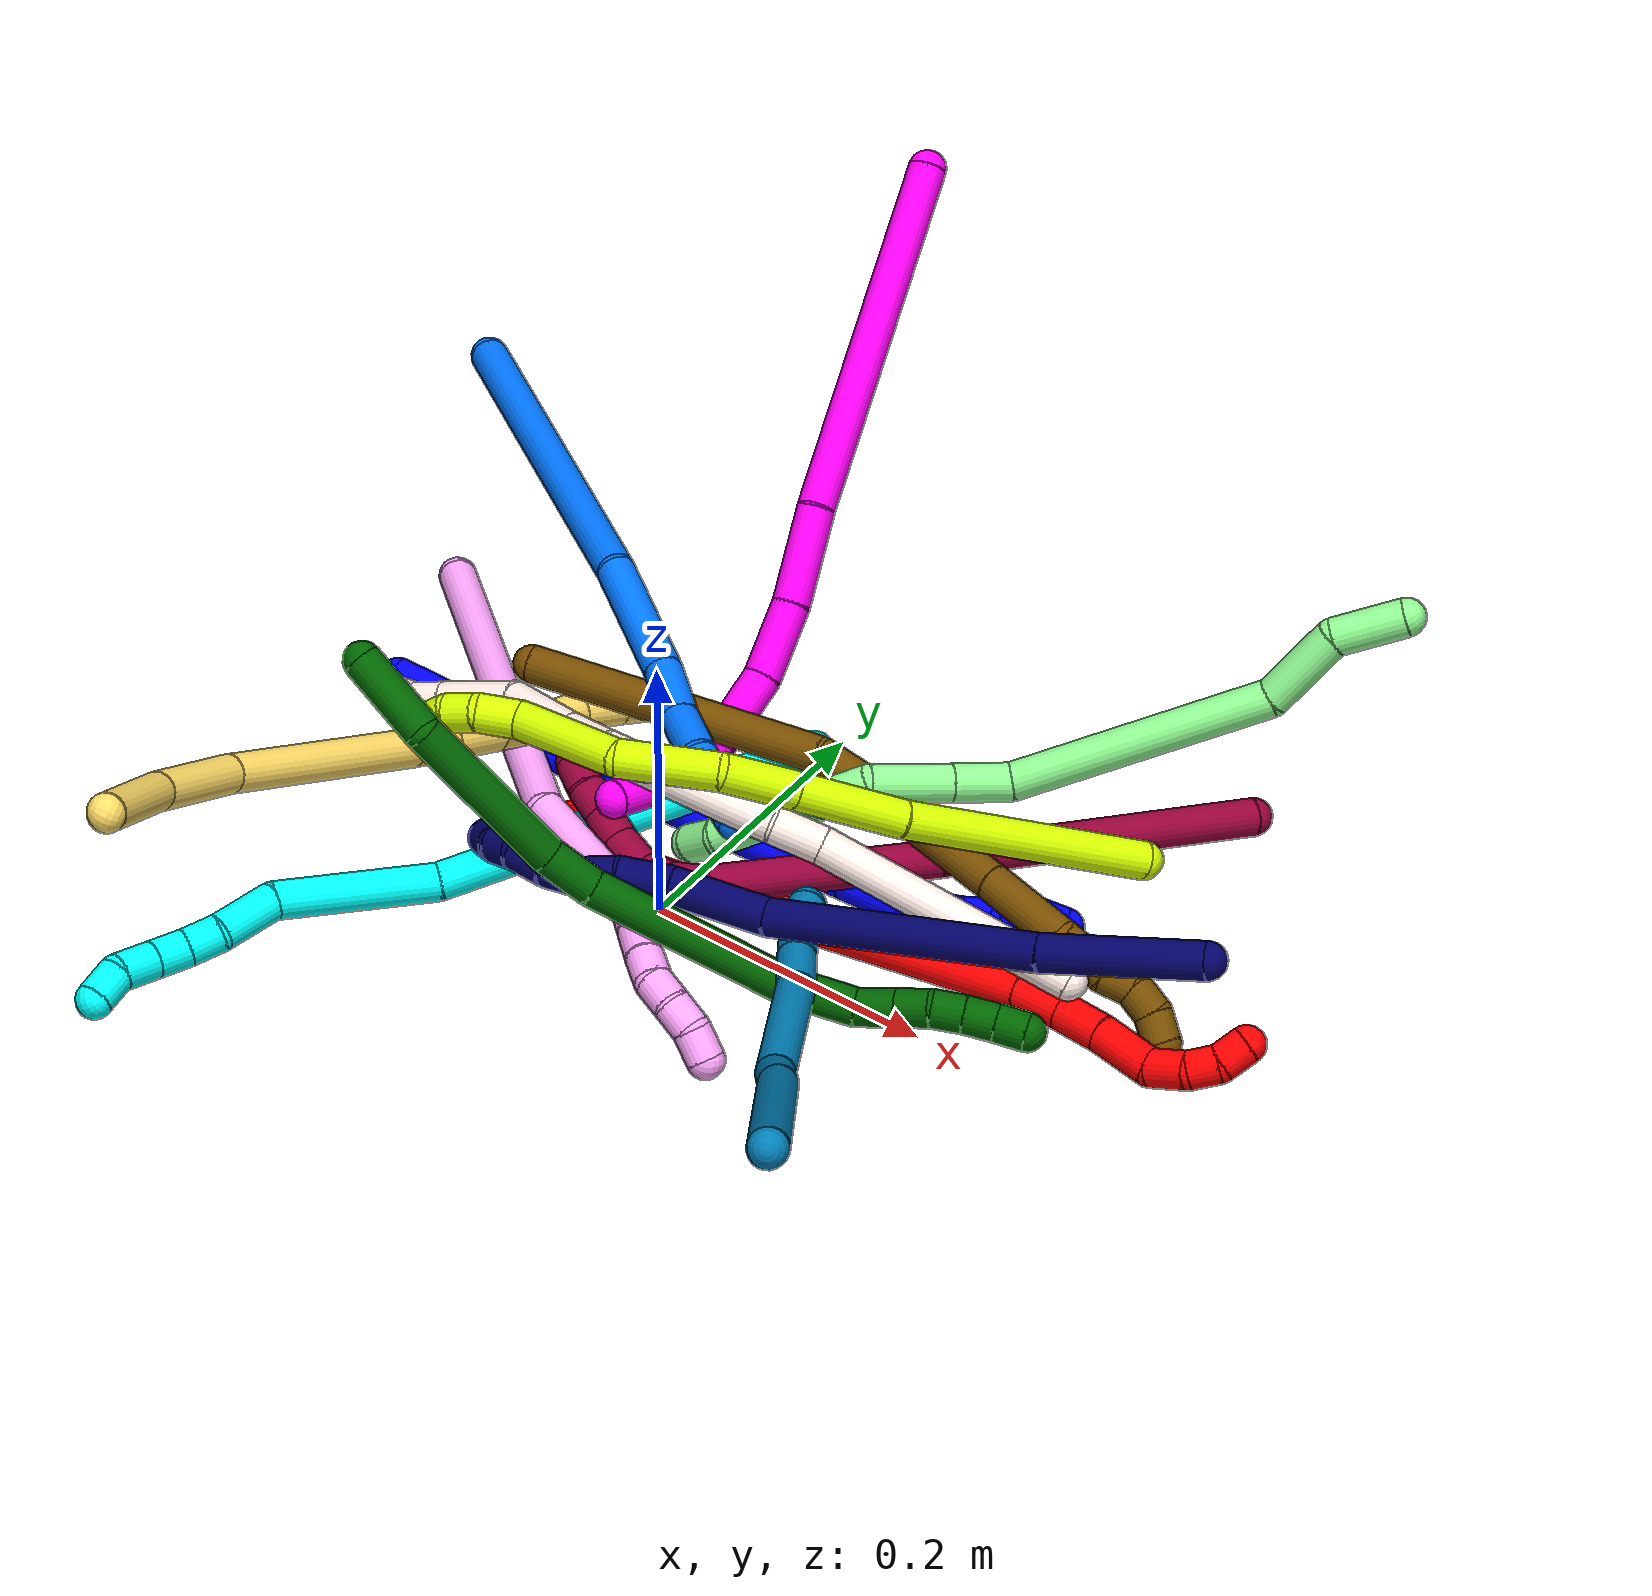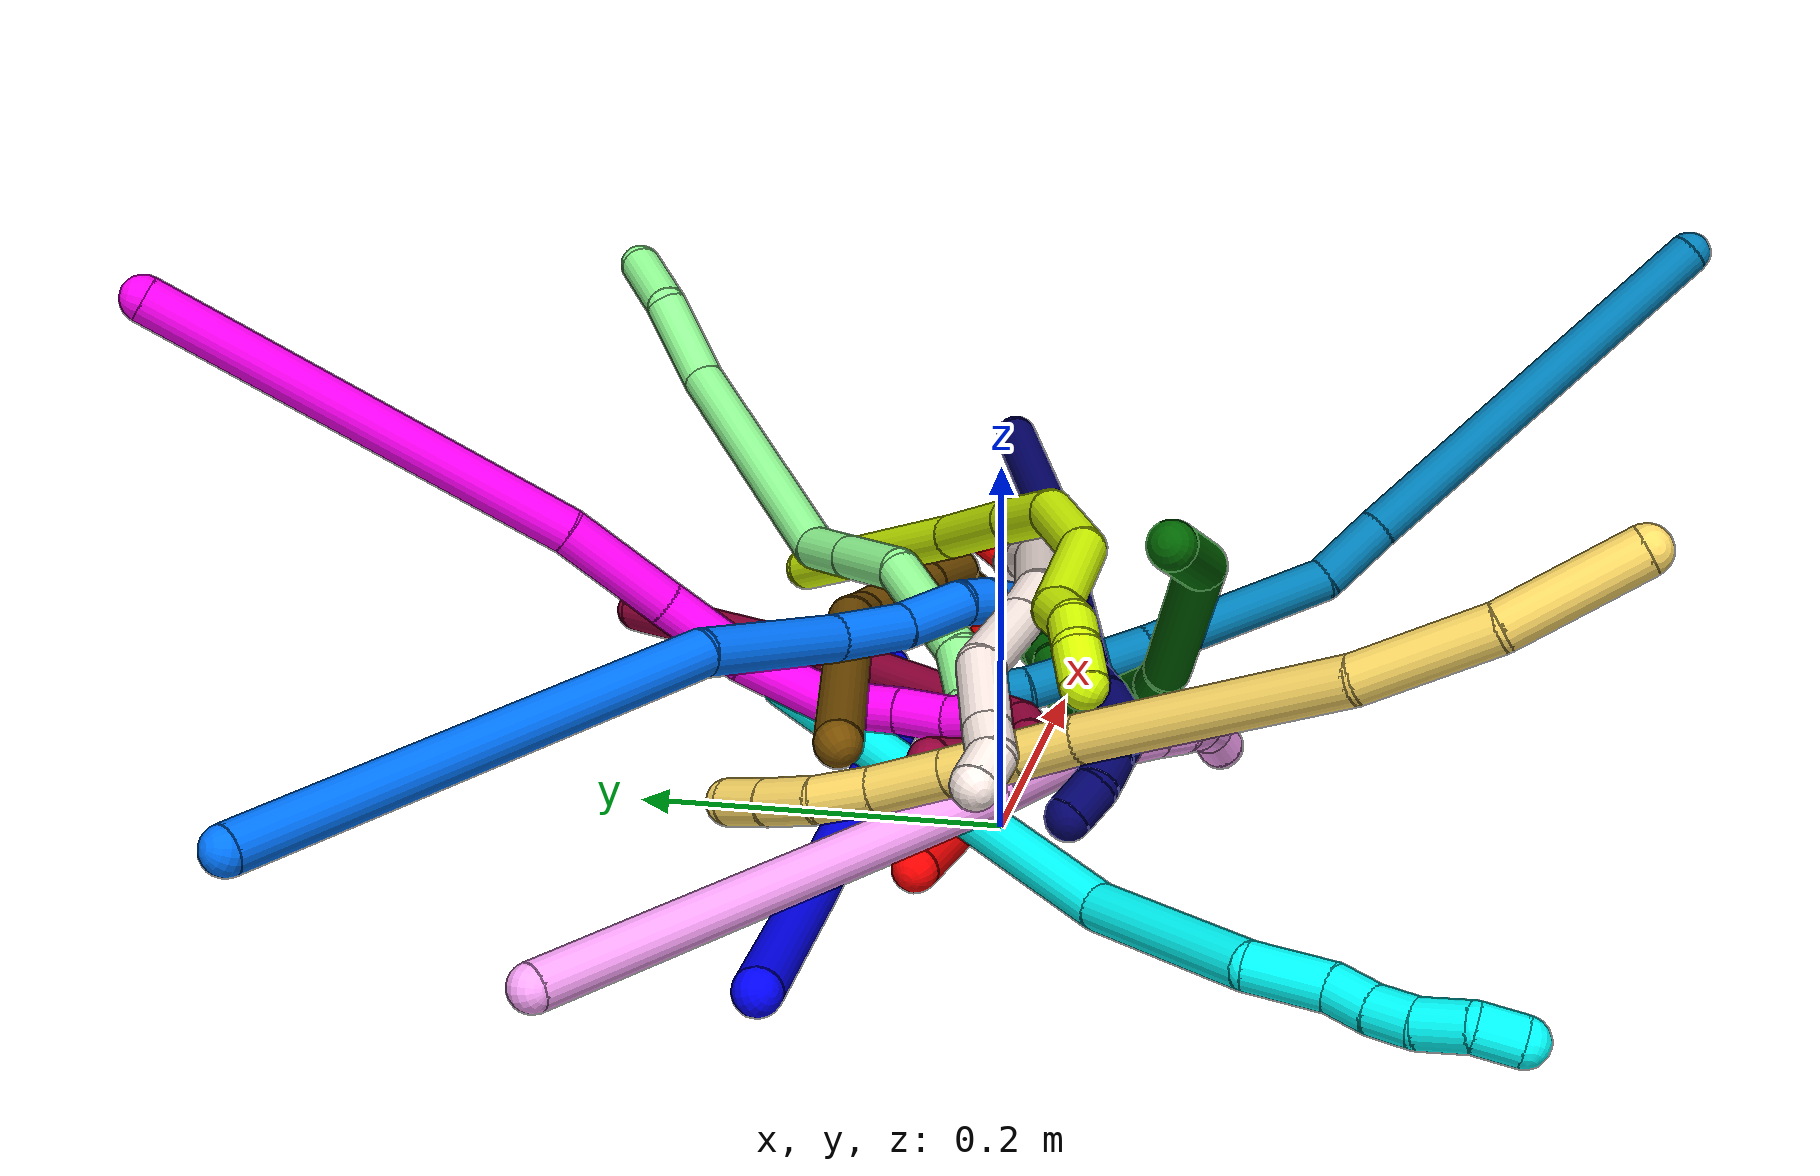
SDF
<sdf version="1.7">
 <world name="default">
  <plugin name="TubeGeneratorPlugin" filename="libtube_generator_plugin.so"/>
  <model name="photoneo_s_sensor">
   <static>1</static>
   <pose>0 0 2 1.57079 1.57079 3.14159</pose>
   <link name="link">
    <inertial><mass>0.1</mass></inertial>
    <sensor name="sensor" type="depth">
     <update_rate>30</update_rate>
     <camera>
      <horizontal_fov>1.22</horizontal_fov>
      <image><width>1920</width><height>1200</height><format>B8G8R8</format></image>
      <clip><near>0.1</near><far>4</far></clip>
      <depth_camera><output>points</output></depth_camera>
     </camera>
     <plugin name="camera_plugin" filename="libgazebo_ros_depth_camera.so">
      <baseline>0.2</baseline>
      <alwaysOn>1</alwaysOn>
      <updateRate>0.0</updateRate>
      <cameraName>camera_ir</cameraName>
      <imageTopicName>/camera/color/image_raw</imageTopicName>
      <cameraInfoTopicName>/camera/color/camera_info</cameraInfoTopicName>
      <depthImageTopicName>/camera/depth/image_raw</depthImageTopicName>
      <depthImageCameraInfoTopicName>/camera/depth/camera_info</depthImageCameraInfoTopicName>
      <pointCloudTopicName>/camera/depth/points</pointCloudTopicName>
      <frameName>fr_optical</frameName>
      <pointCloudCutoff>0.1</pointCloudCutoff>
      <pointCloudCutoffMax>2.0</pointCloudCutoffMax>
      <distortionK1>0</distortionK1>
      <distortionK2>0</distortionK2>
      <distortionK3>0</distortionK3>
      <distortionT1>0</distortionT1>
      <distortionT2>0</distortionT2>
      <CxPrime>0</CxPrime>
      <Cx>0</Cx>
      <Cy>0</Cy>
      <focalLength>0</focalLength>
      <hackBaseline>0</hackBaseline>
     </plugin>
    </sensor>
   </link>
  </model>
  <gravity>0 0 -9.8</gravity>
  <magnetic_field>6e-06 2.3e-05 -4.2e-05</magnetic_field>
  <atmosphere type="adiabatic"/>
  <physics name="default_physics" default="0" type="ode">
   <max_step_size>0.003</max_step_size>
   <real_time_factor>1</real_time_factor>
   <real_time_update_rate>1000</real_time_update_rate>
   <max_contacts>10000</max_contacts>
   <ode>
    <solver>
     <type>quick</type>
     <iters>100</iters>
     <sor>1.3</sor>
     <use_dynamic_moi_rescaling>0</use_dynamic_moi_rescaling>
    </solver>
    <constraints>
     <contact_max_correcting_vel>0</contact_max_correcting_vel>
     <contact_surface_layer>0.001</contact_surface_layer>
     <cfm>0</cfm>
     <erp>0.2</erp>
    </constraints>
   </ode>
  </physics>
  <scene><ambient>0.4 0.4 0.4 1</ambient><background>0.7 0.7 0.7 1</background><shadows>0</shadows></scene>
  <audio><device>default</device></audio>
  <spherical_coordinates>
   <surface_model>EARTH_WGS84</surface_model>
   <latitude_deg>0</latitude_deg>
   <longitude_deg>0</longitude_deg>
   <elevation>0</elevation>
   <heading_deg>0</heading_deg>
  </spherical_coordinates>
  <model name="bin">
   <static>1</static>
   <link name="bottom">
    <collision name="collision-bottom">
     <pose>0 0 -0.01 0 -0 0</pose>
     <geometry><box><size>0.8 0.6 0.02</size></box></geometry>
     <surface>
      <friction><ode><mu>100</mu><mu2>100</mu2></ode></friction>
      <contact><collide_bitmask>65535</collide_bitmask></contact>
     </surface>
    </collision>
   </link>
   <link name="west_wall">
    <collision name="collision-west_wall">
     <pose>-0.41 0 0.1 0 -0 0</pose>
     <geometry><box><size>0.02 0.6 0.2</size></box></geometry>
     <surface>
      <friction><ode><mu>100</mu><mu2>100</mu2></ode></friction>
      <contact><collide_bitmask>65535</collide_bitmask></contact>
     </surface>
    </collision>
   </link>
   <link name="east_wall">
    <collision name="collision-east_wall">
     <pose>0.41 0 0.1 0 -0 0</pose>
     <geometry><box><size>0.02 0.6 0.2</size></box></geometry>
     <surface>
      <friction><ode><mu>100</mu><mu2>100</mu2></ode></friction>
      <contact><collide_bitmask>65535</collide_bitmask></contact>
     </surface>
    </collision>
   </link>
   <link name="south_wall">
    <collision name="collision-south_wall">
     <pose>0 -0.31 0.1 0 -0 0</pose>
     <geometry><box><size>0.8 0.02 0.2</size></box></geometry>
     <surface>
      <friction><ode><mu>100</mu><mu2>100</mu2></ode></friction>
      <contact><collide_bitmask>65535</collide_bitmask></contact>
     </surface>
    </collision>
   </link>
   <link name="north_wall">
    <collision name="collision-north_wall">
     <pose>0 0.31 0.1 0 -0 0</pose>
     <geometry><box><size>0.8 0.02 0.2</size></box></geometry>
     <surface>
      <friction><ode><mu>100</mu><mu2>100</mu2></ode></friction>
      <contact><collide_bitmask>65535</collide_bitmask></contact>
     </surface>
    </collision>
   </link>
  </model>
  <model name="1">
   <static>0</static>
   <link name="1">
    <collision name="collision-cylinder-e_1_1_4">
     <pose>0.056631 -0.002707 -0.043408 3.07931 0.915872 3.01534</pose>
     <geometry><cylinder><radius>0.0125</radius><length>0.14281</length></cylinder></geometry>
     <surface>
      <friction><ode><mu>1.16</mu><mu2>1.16</mu2><slip1>0</slip1><slip2>0</slip2></ode></friction>
      <contact><ode><kp>1e+06</kp><kd>1</kd><max_vel>0</max_vel><min_depth>0.001</min_depth></ode></contact>
     </surface>
    </collision>
    <visual name="visual-cylinder-e_1_1_4">
     <pose>0.056631 -0.002707 -0.043408 3.07931 0.915872 3.01534</pose>
     <geometry><cylinder><radius>0.0125</radius><length>0.14281</length></cylinder></geometry>
     <material><ambient>0 0 1 1</ambient></material>
    </visual>
    <collision name="collision-cylinder-e_2_4_5">
     <pose>0.198283 -0.003655 -0.145984 -3.11187 0.962616 -3.08469</pose>
     <geometry><cylinder><radius>0.0125</radius><length>0.207195</length></cylinder></geometry>
     <surface>
      <friction><ode><mu>1.16</mu><mu2>1.16</mu2><slip1>0</slip1><slip2>0</slip2></ode></friction>
      <contact><ode><kp>1e+06</kp><kd>1</kd><max_vel>0</max_vel><min_depth>0.001</min_depth></ode></contact>
     </surface>
    </collision>
    <visual name="visual-cylinder-e_2_4_5">
     <pose>0.198283 -0.003655 -0.145984 -3.11187 0.962616 -3.08469</pose>
     <geometry><cylinder><radius>0.0125</radius><length>0.207195</length></cylinder></geometry>
     <material><ambient>0 0 1 1</ambient></material>
    </visual>
    <collision name="collision-cylinder-e_3_5_6">
     <pose>0.302526 -0.001551 -0.218111 -3.11502 0.977375 -3.09162</pose>
     <geometry><cylinder><radius>0.0125</radius><length>0.046372</length></cylinder></geometry>
     <surface>
      <friction><ode><mu>1.16</mu><mu2>1.16</mu2><slip1>0</slip1><slip2>0</slip2></ode></friction>
      <contact><ode><kp>1e+06</kp><kd>1</kd><max_vel>0</max_vel><min_depth>0.001</min_depth></ode></contact>
     </surface>
    </collision>
    <visual name="visual-cylinder-e_3_5_6">
     <pose>0.302526 -0.001551 -0.218111 -3.11502 0.977375 -3.09162</pose>
     <geometry><cylinder><radius>0.0125</radius><length>0.046372</length></cylinder></geometry>
     <material><ambient>0 0 1 1</ambient></material>
    </visual>
    <collision name="collision-cylinder-e_4_6_7">
     <pose>0.331996 0.002225 -0.24635 -2.92061 0.579496 -2.42912</pose>
     <geometry><cylinder><radius>0.0125</radius><length>0.037427</length></cylinder></geometry>
     <surface>
      <friction><ode><mu>1.16</mu><mu2>1.16</mu2><slip1>0</slip1><slip2>0</slip2></ode></friction>
      <contact><ode><kp>1e+06</kp><kd>1</kd><max_vel>0</max_vel><min_depth>0.001</min_depth></ode></contact>
     </surface>
    </collision>
    <visual name="visual-cylinder-e_4_6_7">
     <pose>0.331996 0.002225 -0.24635 -2.92061 0.579496 -2.42912</pose>
     <geometry><cylinder><radius>0.0125</radius><length>0.037427</length></cylinder></geometry>
     <material><ambient>0 0 1 1</ambient></material>
    </visual>
    <collision name="collision-cylinder-e_5_7_8">
     <pose>0.348903 0.008742 -0.268885 -2.73963 0.701337 -2.12523</pose>
     <geometry><cylinder><radius>0.0125</radius><length>0.020644</length></cylinder></geometry>
     <surface>
      <friction><ode><mu>1.16</mu><mu2>1.16</mu2><slip1>0</slip1><slip2>0</slip2></ode></friction>
      <contact><ode><kp>1e+06</kp><kd>1</kd><max_vel>0</max_vel><min_depth>0.001</min_depth></ode></contact>
     </surface>
    </collision>
    <visual name="visual-cylinder-e_5_7_8">
     <pose>0.348903 0.008742 -0.268885 -2.73963 0.701337 -2.12523</pose>
     <geometry><cylinder><radius>0.0125</radius><length>0.020644</length></cylinder></geometry>
     <material><ambient>0 0 1 1</ambient></material>
    </visual>
    <collision name="collision-cylinder-e_6_8_9">
     <pose>0.357838 0.015164 -0.287138 -2.847 0.195387 -1.1675</pose>
     <geometry><cylinder><radius>0.0125</radius><length>0.023428</length></cylinder></geometry>
     <surface>
      <friction><ode><mu>1.16</mu><mu2>1.16</mu2><slip1>0</slip1><slip2>0</slip2></ode></friction>
      <contact><ode><kp>1e+06</kp><kd>1</kd><max_vel>0</max_vel><min_depth>0.001</min_depth></ode></contact>
     </surface>
    </collision>
    <visual name="visual-cylinder-e_6_8_9">
     <pose>0.357838 0.015164 -0.287138 -2.847 0.195387 -1.1675</pose>
     <geometry><cylinder><radius>0.0125</radius><length>0.023428</length></cylinder></geometry>
     <material><ambient>0 0 1 1</ambient></material>
    </visual>
    <collision name="collision-cylinder-e_7_9_2">
     <pose>0.366199 0.017971 -0.307356 3.0842 0.582672 2.95072</pose>
     <geometry><cylinder><radius>0.0125</radius><length>0.022125</length></cylinder></geometry>
     <surface>
      <friction><ode><mu>1.16</mu><mu2>1.16</mu2><slip1>0</slip1><slip2>0</slip2></ode></friction>
      <contact><ode><kp>1e+06</kp><kd>1</kd><max_vel>0</max_vel><min_depth>0.001</min_depth></ode></contact>
     </surface>
    </collision>
    <visual name="visual-cylinder-e_7_9_2">
     <pose>0.366199 0.017971 -0.307356 3.0842 0.582672 2.95072</pose>
     <geometry><cylinder><radius>0.0125</radius><length>0.022125</length></cylinder></geometry>
     <material><ambient>0 0 1 1</ambient></material>
    </visual>
    <collision name="collision-sphere-2">
     <pose>0.372286 0.017441 -0.316578 0 -0 0</pose>
     <geometry><sphere><radius>0.0125</radius></sphere></geometry>
     <surface>
      <friction><ode><mu>1.16</mu><mu2>1.16</mu2><slip1>0</slip1><slip2>0</slip2></ode></friction>
      <contact><ode><kp>1e+06</kp><kd>1</kd><max_vel>0</max_vel><min_depth>0.001</min_depth></ode></contact>
     </surface>
    </collision>
    <visual name="visual-sphere-2">
     <pose>0.372286 0.017441 -0.316578 0 -0 0</pose>
     <geometry><sphere><radius>0.0125</radius></sphere></geometry>
     <material><ambient>0 0 1 1</ambient></material>
    </visual>
    <collision name="collision-sphere-9">
     <pose>0.360112 0.0185 -0.298134 0 -0 0</pose>
     <geometry><sphere><radius>0.0125</radius></sphere></geometry>
     <surface>
      <friction><ode><mu>1.16</mu><mu2>1.16</mu2><slip1>0</slip1><slip2>0</slip2></ode></friction>
      <contact><ode><kp>1e+06</kp><kd>1</kd><max_vel>0</max_vel><min_depth>0.001</min_depth></ode></contact>
     </surface>
    </collision>
    <visual name="visual-sphere-9">
     <pose>0.360112 0.0185 -0.298134 0 -0 0</pose>
     <geometry><sphere><radius>0.0125</radius></sphere></geometry>
     <material><ambient>0 0 1 1</ambient></material>
    </visual>
    <collision name="collision-sphere-4">
     <pose>0.113262 -0.005415 -0.086817 0 -0 0</pose>
     <geometry><sphere><radius>0.0125</radius></sphere></geometry>
     <surface>
      <friction><ode><mu>1.16</mu><mu2>1.16</mu2><slip1>0</slip1><slip2>0</slip2></ode></friction>
      <contact><ode><kp>1e+06</kp><kd>1</kd><max_vel>0</max_vel><min_depth>0.001</min_depth></ode></contact>
     </surface>
    </collision>
    <visual name="visual-sphere-4">
     <pose>0.113262 -0.005415 -0.086817 0 -0 0</pose>
     <geometry><sphere><radius>0.0125</radius></sphere></geometry>
     <material><ambient>0 0 1 1</ambient></material>
    </visual>
    <collision name="collision-sphere-1">
     <geometry><sphere><radius>0.0125</radius></sphere></geometry>
     <surface>
      <friction><ode><mu>1.16</mu><mu2>1.16</mu2><slip1>0</slip1><slip2>0</slip2></ode></friction>
      <contact><ode><kp>1e+06</kp><kd>1</kd><max_vel>0</max_vel><min_depth>0.001</min_depth></ode></contact>
     </surface>
    </collision>
    <visual name="visual-sphere-1">
     <geometry><sphere><radius>0.0125</radius></sphere></geometry>
     <material><ambient>0 0 1 1</ambient></material>
    </visual>
    <collision name="collision-sphere-8">
     <pose>0.355563 0.011828 -0.276142 0 -0 0</pose>
     <geometry><sphere><radius>0.0125</radius></sphere></geometry>
     <surface>
      <friction><ode><mu>1.16</mu><mu2>1.16</mu2><slip1>0</slip1><slip2>0</slip2></ode></friction>
      <contact><ode><kp>1e+06</kp><kd>1</kd><max_vel>0</max_vel><min_depth>0.001</min_depth></ode></contact>
     </surface>
    </collision>
    <visual name="visual-sphere-8">
     <pose>0.355563 0.011828 -0.276142 0 -0 0</pose>
     <geometry><sphere><radius>0.0125</radius></sphere></geometry>
     <material><ambient>0 0 1 1</ambient></material>
    </visual>
    <collision name="collision-sphere-5">
     <pose>0.283304 -0.001896 -0.20515 0 -0 0</pose>
     <geometry><sphere><radius>0.0125</radius></sphere></geometry>
     <surface>
      <friction><ode><mu>1.16</mu><mu2>1.16</mu2><slip1>0</slip1><slip2>0</slip2></ode></friction>
      <contact><ode><kp>1e+06</kp><kd>1</kd><max_vel>0</max_vel><min_depth>0.001</min_depth></ode></contact>
     </surface>
    </collision>
    <visual name="visual-sphere-5">
     <pose>0.283304 -0.001896 -0.20515 0 -0 0</pose>
     <geometry><sphere><radius>0.0125</radius></sphere></geometry>
     <material><ambient>0 0 1 1</ambient></material>
    </visual>
    <collision name="collision-sphere-6">
     <pose>0.321748 -0.001207 -0.231072 0 -0 0</pose>
     <geometry><sphere><radius>0.0125</radius></sphere></geometry>
     <surface>
      <friction><ode><mu>1.16</mu><mu2>1.16</mu2><slip1>0</slip1><slip2>0</slip2></ode></friction>
      <contact><ode><kp>1e+06</kp><kd>1</kd><max_vel>0</max_vel><min_depth>0.001</min_depth></ode></contact>
     </surface>
    </collision>
    <visual name="visual-sphere-6">
     <pose>0.321748 -0.001207 -0.231072 0 -0 0</pose>
     <geometry><sphere><radius>0.0125</radius></sphere></geometry>
     <material><ambient>0 0 1 1</ambient></material>
    </visual>
    <collision name="collision-sphere-7">
     <pose>0.342243 0.005657 -0.261628 0 -0 0</pose>
     <geometry><sphere><radius>0.0125</radius></sphere></geometry>
     <surface>
      <friction><ode><mu>1.16</mu><mu2>1.16</mu2><slip1>0</slip1><slip2>0</slip2></ode></friction>
      <contact><ode><kp>1e+06</kp><kd>1</kd><max_vel>0</max_vel><min_depth>0.001</min_depth></ode></contact>
     </surface>
    </collision>
    <visual name="visual-sphere-7">
     <pose>0.342243 0.005657 -0.261628 0 -0 0</pose>
     <geometry><sphere><radius>0.0125</radius></sphere></geometry>
     <material><ambient>0 0 1 1</ambient></material>
    </visual>
    <inertial>
     <pose>0.198626 -0.000399 -0.149717 0 -0 0</pose>
     <mass>0.5</mass>
     <inertia>
      <ixx>-0.00057</ixx>
      <ixy>0</ixy>
      <ixz>0</ixz>
      <iyy>0.001003</iyy>
      <iyz>0</iyz>
      <izz>-0.000856</izz>
     </inertia>
    </inertial>
   </link>
   <pose>-0.261602 0.064485 0.01968 1.15064 -0.274171 -0.519933</pose>
  </model>
  <model name="2">
   <static>0</static>
   <link name="2">
    <collision name="collision-cylinder-e_1_1_4">
     <pose>0.006479 -0.003696 0.036149 0.101897 0.176455 0.009021</pose>
     <geometry><cylinder><radius>0.0125</radius><length>0.073822</length></cylinder></geometry>
     <surface>
      <friction><ode><mu>1.16</mu><mu2>1.16</mu2><slip1>0</slip1><slip2>0</slip2></ode></friction>
      <contact><ode><kp>1e+06</kp><kd>1</kd><max_vel>0</max_vel><min_depth>0.001</min_depth></ode></contact>
     </surface>
    </collision>
    <visual name="visual-cylinder-e_1_1_4">
     <pose>0.006479 -0.003696 0.036149 0.101897 0.176455 0.009021</pose>
     <geometry><cylinder><radius>0.0125</radius><length>0.073822</length></cylinder></geometry>
     <material><ambient>1 0 0 1</ambient></material>
    </visual>
    <collision name="collision-cylinder-e_2_4_5">
     <pose>0.058811 0.011089 0.191696 -0.153572 0.362715 -0.028215</pose>
     <geometry><cylinder><radius>0.0125</radius><length>0.258455</length></cylinder></geometry>
     <surface>
      <friction><ode><mu>1.16</mu><mu2>1.16</mu2><slip1>0</slip1><slip2>0</slip2></ode></friction>
      <contact><ode><kp>1e+06</kp><kd>1</kd><max_vel>0</max_vel><min_depth>0.001</min_depth></ode></contact>
     </surface>
    </collision>
    <visual name="visual-cylinder-e_2_4_5">
     <pose>0.058811 0.011089 0.191696 -0.153572 0.362715 -0.028215</pose>
     <geometry><cylinder><radius>0.0125</radius><length>0.258455</length></cylinder></geometry>
     <material><ambient>1 0 0 1</ambient></material>
    </visual>
    <collision name="collision-cylinder-e_3_5_6">
     <pose>0.109859 0.029773 0.326049 -0.013501 0.334408 -0.002279</pose>
     <geometry><cylinder><radius>0.0125</radius><length>0.031666</length></cylinder></geometry>
     <surface>
      <friction><ode><mu>1.16</mu><mu2>1.16</mu2><slip1>0</slip1><slip2>0</slip2></ode></friction>
      <contact><ode><kp>1e+06</kp><kd>1</kd><max_vel>0</max_vel><min_depth>0.001</min_depth></ode></contact>
     </surface>
    </collision>
    <visual name="visual-cylinder-e_3_5_6">
     <pose>0.109859 0.029773 0.326049 -0.013501 0.334408 -0.002279</pose>
     <geometry><cylinder><radius>0.0125</radius><length>0.031666</length></cylinder></geometry>
     <material><ambient>1 0 0 1</ambient></material>
    </visual>
    <collision name="collision-cylinder-e_4_6_7">
     <pose>0.11927 0.029345 0.355674 0.042872 0.279481 0.006031</pose>
     <geometry><cylinder><radius>0.0125</radius><length>0.030554</length></cylinder></geometry>
     <surface>
      <friction><ode><mu>1.16</mu><mu2>1.16</mu2><slip1>0</slip1><slip2>0</slip2></ode></friction>
      <contact><ode><kp>1e+06</kp><kd>1</kd><max_vel>0</max_vel><min_depth>0.001</min_depth></ode></contact>
     </surface>
    </collision>
    <visual name="visual-cylinder-e_4_6_7">
     <pose>0.11927 0.029345 0.355674 0.042872 0.279481 0.006031</pose>
     <geometry><cylinder><radius>0.0125</radius><length>0.030554</length></cylinder></geometry>
     <material><ambient>1 0 0 1</ambient></material>
    </visual>
    <collision name="collision-cylinder-e_5_7_8">
     <pose>0.129103 0.026072 0.389046 0.140449 0.289185 0.020483</pose>
     <geometry><cylinder><radius>0.0125</radius><length>0.039412</length></cylinder></geometry>
     <surface>
      <friction><ode><mu>1.16</mu><mu2>1.16</mu2><slip1>0</slip1><slip2>0</slip2></ode></friction>
      <contact><ode><kp>1e+06</kp><kd>1</kd><max_vel>0</max_vel><min_depth>0.001</min_depth></ode></contact>
     </surface>
    </collision>
    <visual name="visual-cylinder-e_5_7_8">
     <pose>0.129103 0.026072 0.389046 0.140449 0.289185 0.020483</pose>
     <geometry><cylinder><radius>0.0125</radius><length>0.039412</length></cylinder></geometry>
     <material><ambient>1 0 0 1</ambient></material>
    </visual>
    <collision name="collision-cylinder-e_6_8_9">
     <pose>0.137598 0.027925 0.419416 -0.367852 0.225977 -0.042212</pose>
     <geometry><cylinder><radius>0.0125</radius><length>0.025663</length></cylinder></geometry>
     <surface>
      <friction><ode><mu>1.16</mu><mu2>1.16</mu2><slip1>0</slip1><slip2>0</slip2></ode></friction>
      <contact><ode><kp>1e+06</kp><kd>1</kd><max_vel>0</max_vel><min_depth>0.001</min_depth></ode></contact>
     </surface>
    </collision>
    <visual name="visual-cylinder-e_6_8_9">
     <pose>0.137598 0.027925 0.419416 -0.367852 0.225977 -0.042212</pose>
     <geometry><cylinder><radius>0.0125</radius><length>0.025663</length></cylinder></geometry>
     <material><ambient>1 0 0 1</ambient></material>
    </visual>
    <collision name="collision-cylinder-e_7_9_10">
     <pose>0.1448 0.038494 0.437759 -0.738174 0.447193 -0.17547</pose>
     <geometry><cylinder><radius>0.0125</radius><length>0.020014</length></cylinder></geometry>
     <surface>
      <friction><ode><mu>1.16</mu><mu2>1.16</mu2><slip1>0</slip1><slip2>0</slip2></ode></friction>
      <contact><ode><kp>1e+06</kp><kd>1</kd><max_vel>0</max_vel><min_depth>0.001</min_depth></ode></contact>
     </surface>
    </collision>
    <visual name="visual-cylinder-e_7_9_10">
     <pose>0.1448 0.038494 0.437759 -0.738174 0.447193 -0.17547</pose>
     <geometry><cylinder><radius>0.0125</radius><length>0.020014</length></cylinder></geometry>
     <material><ambient>1 0 0 1</ambient></material>
    </visual>
    <collision name="collision-cylinder-e_8_10_2">
     <pose>0.152967 0.05344 0.447704 -1.21773 0.38562 -0.270586</pose>
     <geometry><cylinder><radius>0.0125</radius><length>0.020414</length></cylinder></geometry>
     <surface>
      <friction><ode><mu>1.16</mu><mu2>1.16</mu2><slip1>0</slip1><slip2>0</slip2></ode></friction>
      <contact><ode><kp>1e+06</kp><kd>1</kd><max_vel>0</max_vel><min_depth>0.001</min_depth></ode></contact>
     </surface>
    </collision>
    <visual name="visual-cylinder-e_8_10_2">
     <pose>0.152967 0.05344 0.447704 -1.21773 0.38562 -0.270586</pose>
     <geometry><cylinder><radius>0.0125</radius><length>0.020414</length></cylinder></geometry>
     <material><ambient>1 0 0 1</ambient></material>
    </visual>
    <collision name="collision-sphere-2">
     <pose>0.156806 0.062314 0.450974 0 -0 0</pose>
     <geometry><sphere><radius>0.0125</radius></sphere></geometry>
     <surface>
      <friction><ode><mu>1.16</mu><mu2>1.16</mu2><slip1>0</slip1><slip2>0</slip2></ode></friction>
      <contact><ode><kp>1e+06</kp><kd>1</kd><max_vel>0</max_vel><min_depth>0.001</min_depth></ode></contact>
     </surface>
    </collision>
    <visual name="visual-sphere-2">
     <pose>0.156806 0.062314 0.450974 0 -0 0</pose>
     <geometry><sphere><radius>0.0125</radius></sphere></geometry>
     <material><ambient>1 0 0 1</ambient></material>
    </visual>
    <collision name="collision-sphere-10">
     <pose>0.149128 0.044566 0.444434 0 -0 0</pose>
     <geometry><sphere><radius>0.0125</radius></sphere></geometry>
     <surface>
      <friction><ode><mu>1.16</mu><mu2>1.16</mu2><slip1>0</slip1><slip2>0</slip2></ode></friction>
      <contact><ode><kp>1e+06</kp><kd>1</kd><max_vel>0</max_vel><min_depth>0.001</min_depth></ode></contact>
     </surface>
    </collision>
    <visual name="visual-sphere-10">
     <pose>0.149128 0.044566 0.444434 0 -0 0</pose>
     <geometry><sphere><radius>0.0125</radius></sphere></geometry>
     <material><ambient>1 0 0 1</ambient></material>
    </visual>
    <collision name="collision-sphere-9">
     <pose>0.140473 0.032422 0.431085 0 -0 0</pose>
     <geometry><sphere><radius>0.0125</radius></sphere></geometry>
     <surface>
      <friction><ode><mu>1.16</mu><mu2>1.16</mu2><slip1>0</slip1><slip2>0</slip2></ode></friction>
      <contact><ode><kp>1e+06</kp><kd>1</kd><max_vel>0</max_vel><min_depth>0.001</min_depth></ode></contact>
     </surface>
    </collision>
    <visual name="visual-sphere-9">
     <pose>0.140473 0.032422 0.431085 0 -0 0</pose>
     <geometry><sphere><radius>0.0125</radius></sphere></geometry>
     <material><ambient>1 0 0 1</ambient></material>
    </visual>
    <collision name="collision-sphere-4">
     <pose>0.012959 -0.007393 0.072299 0 -0 0</pose>
     <geometry><sphere><radius>0.0125</radius></sphere></geometry>
     <surface>
      <friction><ode><mu>1.16</mu><mu2>1.16</mu2><slip1>0</slip1><slip2>0</slip2></ode></friction>
      <contact><ode><kp>1e+06</kp><kd>1</kd><max_vel>0</max_vel><min_depth>0.001</min_depth></ode></contact>
     </surface>
    </collision>
    <visual name="visual-sphere-4">
     <pose>0.012959 -0.007393 0.072299 0 -0 0</pose>
     <geometry><sphere><radius>0.0125</radius></sphere></geometry>
     <material><ambient>1 0 0 1</ambient></material>
    </visual>
    <collision name="collision-sphere-1">
     <geometry><sphere><radius>0.0125</radius></sphere></geometry>
     <surface>
      <friction><ode><mu>1.16</mu><mu2>1.16</mu2><slip1>0</slip1><slip2>0</slip2></ode></friction>
      <contact><ode><kp>1e+06</kp><kd>1</kd><max_vel>0</max_vel><min_depth>0.001</min_depth></ode></contact>
     </surface>
    </collision>
    <visual name="visual-sphere-1">
     <geometry><sphere><radius>0.0125</radius></sphere></geometry>
     <material><ambient>1 0 0 1</ambient></material>
    </visual>
    <collision name="collision-sphere-8">
     <pose>0.134723 0.023428 0.407748 0 -0 0</pose>
     <geometry><sphere><radius>0.0125</radius></sphere></geometry>
     <surface>
      <friction><ode><mu>1.16</mu><mu2>1.16</mu2><slip1>0</slip1><slip2>0</slip2></ode></friction>
      <contact><ode><kp>1e+06</kp><kd>1</kd><max_vel>0</max_vel><min_depth>0.001</min_depth></ode></contact>
     </surface>
    </collision>
    <visual name="visual-sphere-8">
     <pose>0.134723 0.023428 0.407748 0 -0 0</pose>
     <geometry><sphere><radius>0.0125</radius></sphere></geometry>
     <material><ambient>1 0 0 1</ambient></material>
    </visual>
    <collision name="collision-sphere-5">
     <pose>0.104662 0.029571 0.311094 0 -0 0</pose>
     <geometry><sphere><radius>0.0125</radius></sphere></geometry>
     <surface>
      <friction><ode><mu>1.16</mu><mu2>1.16</mu2><slip1>0</slip1><slip2>0</slip2></ode></friction>
      <contact><ode><kp>1e+06</kp><kd>1</kd><max_vel>0</max_vel><min_depth>0.001</min_depth></ode></contact>
     </surface>
    </collision>
    <visual name="visual-sphere-5">
     <pose>0.104662 0.029571 0.311094 0 -0 0</pose>
     <geometry><sphere><radius>0.0125</radius></sphere></geometry>
     <material><ambient>1 0 0 1</ambient></material>
    </visual>
    <collision name="collision-sphere-6">
     <pose>0.115055 0.029975 0.341003 0 -0 0</pose>
     <geometry><sphere><radius>0.0125</radius></sphere></geometry>
     <surface>
      <friction><ode><mu>1.16</mu><mu2>1.16</mu2><slip1>0</slip1><slip2>0</slip2></ode></friction>
      <contact><ode><kp>1e+06</kp><kd>1</kd><max_vel>0</max_vel><min_depth>0.001</min_depth></ode></contact>
     </surface>
    </collision>
    <visual name="visual-sphere-6">
     <pose>0.115055 0.029975 0.341003 0 -0 0</pose>
     <geometry><sphere><radius>0.0125</radius></sphere></geometry>
     <material><ambient>1 0 0 1</ambient></material>
    </visual>
    <collision name="collision-sphere-7">
     <pose>0.123484 0.028716 0.370344 0 -0 0</pose>
     <geometry><sphere><radius>0.0125</radius></sphere></geometry>
     <surface>
      <friction><ode><mu>1.16</mu><mu2>1.16</mu2><slip1>0</slip1><slip2>0</slip2></ode></friction>
      <contact><ode><kp>1e+06</kp><kd>1</kd><max_vel>0</max_vel><min_depth>0.001</min_depth></ode></contact>
     </surface>
    </collision>
    <visual name="visual-sphere-7">
     <pose>0.123484 0.028716 0.370344 0 -0 0</pose>
     <geometry><sphere><radius>0.0125</radius></sphere></geometry>
     <material><ambient>1 0 0 1</ambient></material>
    </visual>
    <inertial>
     <pose>0.074883 0.016076 0.234805 0 -0 0</pose>
     <mass>0.5</mass>
     <inertia>
      <ixx>0.001382</ixx>
      <ixy>0</ixy>
      <ixz>0</ixz>
      <iyy>0.001454</iyy>
      <iyz>0</iyz>
      <izz>-0.000697</izz>
     </inertia>
    </inertial>
   </link>
   <pose>-0.089229 0.027489 0.011499 1.30294 0.748193 1.17044</pose>
  </model>
  <model name="3">
   <static>0</static>
   <link name="3">
    <collision name="collision-cylinder-e_1_1_4">
     <pose>-0.0514 -0.071039 0.091895 0.658086 -0.416621 -0.144102</pose>
     <geometry><cylinder><radius>0.0125</radius><length>0.254034</length></cylinder></geometry>
     <surface>
      <friction><ode><mu>1.16</mu><mu2>1.16</mu2><slip1>0</slip1><slip2>0</slip2></ode></friction>
      <contact><ode><kp>1e+06</kp><kd>1</kd><max_vel>0</max_vel><min_depth>0.001</min_depth></ode></contact>
     </surface>
    </collision>
    <visual name="visual-cylinder-e_1_1_4">
     <pose>-0.0514 -0.071039 0.091895 0.658086 -0.416621 -0.144102</pose>
     <geometry><cylinder><radius>0.0125</radius><length>0.254034</length></cylinder></geometry>
     <material><ambient>0.003922 1 0.996078 1</ambient></material>
    </visual>
    <collision name="collision-cylinder-e_2_4_5">
     <pose>-0.116749 -0.182057 0.216506 0.884977 -0.26372 -0.125521</pose>
     <geometry><cylinder><radius>0.0125</radius><length>0.107017</length></cylinder></geometry>
     <surface>
      <friction><ode><mu>1.16</mu><mu2>1.16</mu2><slip1>0</slip1><slip2>0</slip2></ode></friction>
      <contact><ode><kp>1e+06</kp><kd>1</kd><max_vel>0</max_vel><min_depth>0.001</min_depth></ode></contact>
     </surface>
    </collision>
    <visual name="visual-cylinder-e_2_4_5">
     <pose>-0.116749 -0.182057 0.216506 0.884977 -0.26372 -0.125521</pose>
     <geometry><cylinder><radius>0.0125</radius><length>0.107017</length></cylinder></geometry>
     <material><ambient>0.003922 1 0.996078 1</ambient></material>
    </visual>
    <collision name="collision-cylinder-e_3_5_6">
     <pose>-0.144753 -0.235205 0.257726 0.997451 -0.730939 -0.410948</pose>
     <geometry><cylinder><radius>0.0125</radius><length>0.042112</length></cylinder></geometry>
     <surface>
      <friction><ode><mu>1.16</mu><mu2>1.16</mu2><slip1>0</slip1><slip2>0</slip2></ode></friction>
      <contact><ode><kp>1e+06</kp><kd>1</kd><max_vel>0</max_vel><min_depth>0.001</min_depth></ode></contact>
     </surface>
    </collision>
    <visual name="visual-cylinder-e_3_5_6">
     <pose>-0.144753 -0.235205 0.257726 0.997451 -0.730939 -0.410948</pose>
     <geometry><cylinder><radius>0.0125</radius><length>0.042112</length></cylinder></geometry>
     <material><ambient>0.003922 1 0.996078 1</ambient></material>
    </visual>
    <collision name="collision-cylinder-e_4_6_7">
     <pose>-0.164726 -0.255051 0.273579 0.737401 -0.537412 -0.211988</pose>
     <geometry><cylinder><radius>0.0125</radius><length>0.023114</length></cylinder></geometry>
     <surface>
      <friction><ode><mu>1.16</mu><mu2>1.16</mu2><slip1>0</slip1><slip2>0</slip2></ode></friction>
      <contact><ode><kp>1e+06</kp><kd>1</kd><max_vel>0</max_vel><min_depth>0.001</min_depth></ode></contact>
     </surface>
    </collision>
    <visual name="visual-cylinder-e_4_6_7">
     <pose>-0.164726 -0.255051 0.273579 0.737401 -0.537412 -0.211988</pose>
     <geometry><cylinder><radius>0.0125</radius><length>0.023114</length></cylinder></geometry>
     <material><ambient>0.003922 1 0.996078 1</ambient></material>
    </visual>
    <collision name="collision-cylinder-e_5_7_8">
     <pose>-0.176464 -0.269737 0.2869 0.930143 -0.527548 -0.269388</pose>
     <geometry><cylinder><radius>0.0125</radius><length>0.02313</length></cylinder></geometry>
     <surface>
      <friction><ode><mu>1.16</mu><mu2>1.16</mu2><slip1>0</slip1><slip2>0</slip2></ode></friction>
      <contact><ode><kp>1e+06</kp><kd>1</kd><max_vel>0</max_vel><min_depth>0.001</min_depth></ode></contact>
     </surface>
    </collision>
    <visual name="visual-cylinder-e_5_7_8">
     <pose>-0.176464 -0.269737 0.2869 0.930143 -0.527548 -0.269388</pose>
     <geometry><cylinder><radius>0.0125</radius><length>0.02313</length></cylinder></geometry>
     <material><ambient>0.003922 1 0.996078 1</ambient></material>
    </visual>
    <collision name="collision-cylinder-e_6_8_9">
     <pose>-0.189744 -0.288371 0.296895 1.20885 -0.580991 -0.407224</pose>
     <geometry><cylinder><radius>0.0125</radius><length>0.027177</length></cylinder></geometry>
     <surface>
      <friction><ode><mu>1.16</mu><mu2>1.16</mu2><slip1>0</slip1><slip2>0</slip2></ode></friction>
      <contact><ode><kp>1e+06</kp><kd>1</kd><max_vel>0</max_vel><min_depth>0.001</min_depth></ode></contact>
     </surface>
    </collision>
    <visual name="visual-cylinder-e_6_8_9">
     <pose>-0.189744 -0.288371 0.296895 1.20885 -0.580991 -0.407224</pose>
     <geometry><cylinder><radius>0.0125</radius><length>0.027177</length></cylinder></geometry>
     <material><ambient>0.003922 1 0.996078 1</ambient></material>
    </visual>
    <collision name="collision-cylinder-e_7_9_2">
     <pose>-0.207258 -0.303886 0.304385 0.954197 -1.03306 -0.571141</pose>
     <geometry><cylinder><radius>0.0125</radius><length>0.023417</length></cylinder></geometry>
     <surface>
      <friction><ode><mu>1.16</mu><mu2>1.16</mu2><slip1>0</slip1><slip2>0</slip2></ode></friction>
      <contact><ode><kp>1e+06</kp><kd>1</kd><max_vel>0</max_vel><min_depth>0.001</min_depth></ode></contact>
     </surface>
    </collision>
    <visual name="visual-cylinder-e_7_9_2">
     <pose>-0.207258 -0.303886 0.304385 0.954197 -1.03306 -0.571141</pose>
     <geometry><cylinder><radius>0.0125</radius><length>0.023417</length></cylinder></geometry>
     <material><ambient>0.003922 1 0.996078 1</ambient></material>
    </visual>
    <collision name="collision-sphere-2">
     <pose>-0.217314 -0.308779 0.307853 0 -0 0</pose>
     <geometry><sphere><radius>0.0125</radius></sphere></geometry>
     <surface>
      <friction><ode><mu>1.16</mu><mu2>1.16</mu2><slip1>0</slip1><slip2>0</slip2></ode></friction>
      <contact><ode><kp>1e+06</kp><kd>1</kd><max_vel>0</max_vel><min_depth>0.001</min_depth></ode></contact>
     </surface>
    </collision>
    <visual name="visual-sphere-2">
     <pose>-0.217314 -0.308779 0.307853 0 -0 0</pose>
     <geometry><sphere><radius>0.0125</radius></sphere></geometry>
     <material><ambient>0.003922 1 0.996078 1</ambient></material>
    </visual>
    <collision name="collision-sphere-9">
     <pose>-0.197202 -0.298994 0.300917 0 -0 0</pose>
     <geometry><sphere><radius>0.0125</radius></sphere></geometry>
     <surface>
      <friction><ode><mu>1.16</mu><mu2>1.16</mu2><slip1>0</slip1><slip2>0</slip2></ode></friction>
      <contact><ode><kp>1e+06</kp><kd>1</kd><max_vel>0</max_vel><min_depth>0.001</min_depth></ode></contact>
     </surface>
    </collision>
    <visual name="visual-sphere-9">
     <pose>-0.197202 -0.298994 0.300917 0 -0 0</pose>
     <geometry><sphere><radius>0.0125</radius></sphere></geometry>
     <material><ambient>0.003922 1 0.996078 1</ambient></material>
    </visual>
    <collision name="collision-sphere-4">
     <pose>-0.102801 -0.142078 0.183791 0 -0 0</pose>
     <geometry><sphere><radius>0.0125</radius></sphere></geometry>
     <surface>
      <friction><ode><mu>1.16</mu><mu2>1.16</mu2><slip1>0</slip1><slip2>0</slip2></ode></friction>
      <contact><ode><kp>1e+06</kp><kd>1</kd><max_vel>0</max_vel><min_depth>0.001</min_depth></ode></contact>
     </surface>
    </collision>
    <visual name="visual-sphere-4">
     <pose>-0.102801 -0.142078 0.183791 0 -0 0</pose>
     <geometry><sphere><radius>0.0125</radius></sphere></geometry>
     <material><ambient>0.003922 1 0.996078 1</ambient></material>
    </visual>
    <collision name="collision-sphere-1">
     <geometry><sphere><radius>0.0125</radius></sphere></geometry>
     <surface>
      <friction><ode><mu>1.16</mu><mu2>1.16</mu2><slip1>0</slip1><slip2>0</slip2></ode></friction>
      <contact><ode><kp>1e+06</kp><kd>1</kd><max_vel>0</max_vel><min_depth>0.001</min_depth></ode></contact>
     </surface>
    </collision>
    <visual name="visual-sphere-1">
     <geometry><sphere><radius>0.0125</radius></sphere></geometry>
     <material><ambient>0.003922 1 0.996078 1</ambient></material>
    </visual>
    <collision name="collision-sphere-8">
     <pose>-0.182286 -0.277748 0.292873 0 -0 0</pose>
     <geometry><sphere><radius>0.0125</radius></sphere></geometry>
     <surface>
      <friction><ode><mu>1.16</mu><mu2>1.16</mu2><slip1>0</slip1><slip2>0</slip2></ode></friction>
      <contact><ode><kp>1e+06</kp><kd>1</kd><max_vel>0</max_vel><min_depth>0.001</min_depth></ode></contact>
     </surface>
    </collision>
    <visual name="visual-sphere-8">
     <pose>-0.182286 -0.277748 0.292873 0 -0 0</pose>
     <geometry><sphere><radius>0.0125</radius></sphere></geometry>
     <material><ambient>0.003922 1 0.996078 1</ambient></material>
    </visual>
    <collision name="collision-sphere-5">
     <pose>-0.130697 -0.222035 0.249222 0 -0 0</pose>
     <geometry><sphere><radius>0.0125</radius></sphere></geometry>
     <surface>
      <friction><ode><mu>1.16</mu><mu2>1.16</mu2><slip1>0</slip1><slip2>0</slip2></ode></friction>
      <contact><ode><kp>1e+06</kp><kd>1</kd><max_vel>0</max_vel><min_depth>0.001</min_depth></ode></contact>
     </surface>
    </collision>
    <visual name="visual-sphere-5">
     <pose>-0.130697 -0.222035 0.249222 0 -0 0</pose>
     <geometry><sphere><radius>0.0125</radius></sphere></geometry>
     <material><ambient>0.003922 1 0.996078 1</ambient></material>
    </visual>
    <collision name="collision-sphere-6">
     <pose>-0.15881 -0.248375 0.26623 0 -0 0</pose>
     <geometry><sphere><radius>0.0125</radius></sphere></geometry>
     <surface>
      <friction><ode><mu>1.16</mu><mu2>1.16</mu2><slip1>0</slip1><slip2>0</slip2></ode></friction>
      <contact><ode><kp>1e+06</kp><kd>1</kd><max_vel>0</max_vel><min_depth>0.001</min_depth></ode></contact>
     </surface>
    </collision>
    <visual name="visual-sphere-6">
     <pose>-0.15881 -0.248375 0.26623 0 -0 0</pose>
     <geometry><sphere><radius>0.0125</radius></sphere></geometry>
     <material><ambient>0.003922 1 0.996078 1</ambient></material>
    </visual>
    <collision name="collision-sphere-7">
     <pose>-0.170642 -0.261726 0.280928 0 -0 0</pose>
     <geometry><sphere><radius>0.0125</radius></sphere></geometry>
     <surface>
      <friction><ode><mu>1.16</mu><mu2>1.16</mu2><slip1>0</slip1><slip2>0</slip2></ode></friction>
      <contact><ode><kp>1e+06</kp><kd>1</kd><max_vel>0</max_vel><min_depth>0.001</min_depth></ode></contact>
     </surface>
    </collision>
    <visual name="visual-sphere-7">
     <pose>-0.170642 -0.261726 0.280928 0 -0 0</pose>
     <geometry><sphere><radius>0.0125</radius></sphere></geometry>
     <material><ambient>0.003922 1 0.996078 1</ambient></material>
    </visual>
    <inertial>
     <pose>-0.099093 -0.149043 0.171047 0 -0 0</pose>
     <mass>0.5</mass>
     <inertia>
      <ixx>0.001144</ixx>
      <ixy>0</ixy>
      <ixz>0</ixz>
      <iyy>0.000985</iyy>
      <iyz>0</iyz>
      <izz>0.001478</izz>
     </inertia>
    </inertial>
   </link>
   <pose>0.029143 0.126243 0.061748 -2.26136 -0.419663 2.12025</pose>
  </model>
  <model name="4">
   <static>0</static>
   <link name="4">
    <collision name="collision-cylinder-e_1_1_4">
     <pose>0.133847 -0.012644 -0.023597 2.64968 1.37339 2.54728</pose>
     <geometry><cylinder><radius>0.0125</radius><length>0.272997</length></cylinder></geometry>
     <surface>
      <friction><ode><mu>1.16</mu><mu2>1.16</mu2><slip1>0</slip1><slip2>0</slip2></ode></friction>
      <contact><ode><kp>1e+06</kp><kd>1</kd><max_vel>0</max_vel><min_depth>0.001</min_depth></ode></contact>
     </surface>
    </collision>
    <visual name="visual-cylinder-e_1_1_4">
     <pose>0.133847 -0.012644 -0.023597 2.64968 1.37339 2.54728</pose>
     <geometry><cylinder><radius>0.0125</radius><length>0.272997</length></cylinder></geometry>
     <material><ambient>1 0.65098 0.996078 1</ambient></material>
    </visual>
    <collision name="collision-cylinder-e_2_4_5">
     <pose>0.312839 -0.024359 -0.036661 -0.088067 1.34073 -0.069841</pose>
     <geometry><cylinder><radius>0.0125</radius><length>0.092731</length></cylinder></geometry>
     <surface>
      <friction><ode><mu>1.16</mu><mu2>1.16</mu2><slip1>0</slip1><slip2>0</slip2></ode></friction>
      <contact><ode><kp>1e+06</kp><kd>1</kd><max_vel>0</max_vel><min_depth>0.001</min_depth></ode></contact>
     </surface>
    </collision>
    <visual name="visual-cylinder-e_2_4_5">
     <pose>0.312839 -0.024359 -0.036661 -0.088067 1.34073 -0.069841</pose>
     <geometry><cylinder><radius>0.0125</radius><length>0.092731</length></cylinder></geometry>
     <material><ambient>1 0.65098 0.996078 1</ambient></material>
    </visual>
    <collision name="collision-cylinder-e_3_5_6">
     <pose>0.372435 -0.022634 -0.02848 -2.81555 1.40073 -2.75617</pose>
     <geometry><cylinder><radius>0.0125</radius><length>0.029327</length></cylinder></geometry>
     <surface>
      <friction><ode><mu>1.16</mu><mu2>1.16</mu2><slip1>0</slip1><slip2>0</slip2></ode></friction>
      <contact><ode><kp>1e+06</kp><kd>1</kd><max_vel>0</max_vel><min_depth>0.001</min_depth></ode></contact>
     </surface>
    </collision>
    <visual name="visual-cylinder-e_3_5_6">
     <pose>0.372435 -0.022634 -0.02848 -2.81555 1.40073 -2.75617</pose>
     <geometry><cylinder><radius>0.0125</radius><length>0.029327</length></cylinder></geometry>
     <material><ambient>1 0.65098 0.996078 1</ambient></material>
    </visual>
    <collision name="collision-cylinder-e_4_6_7">
     <pose>0.398092 -0.021125 -0.032637 -2.76519 1.39917 -2.69648</pose>
     <geometry><cylinder><radius>0.0125</radius><length>0.022744</length></cylinder></geometry>
     <surface>
      <friction><ode><mu>1.16</mu><mu2>1.16</mu2><slip1>0</slip1><slip2>0</slip2></ode></friction>
      <contact><ode><kp>1e+06</kp><kd>1</kd><max_vel>0</max_vel><min_depth>0.001</min_depth></ode></contact>
     </surface>
    </collision>
    <visual name="visual-cylinder-e_4_6_7">
     <pose>0.398092 -0.021125 -0.032637 -2.76519 1.39917 -2.69648</pose>
     <geometry><cylinder><radius>0.0125</radius><length>0.022744</length></cylinder></geometry>
     <material><ambient>1 0.65098 0.996078 1</ambient></material>
    </visual>
    <collision name="collision-cylinder-e_5_7_8">
     <pose>0.4196 -0.01917 -0.035333 -2.19232 1.42368 -2.06729</pose>
     <geometry><cylinder><radius>0.0125</radius><length>0.020831</length></cylinder></geometry>
     <surface>
      <friction><ode><mu>1.16</mu><mu2>1.16</mu2><slip1>0</slip1><slip2>0</slip2></ode></friction>
      <contact><ode><kp>1e+06</kp><kd>1</kd><max_vel>0</max_vel><min_depth>0.001</min_depth></ode></contact>
     </surface>
    </collision>
    <visual name="visual-cylinder-e_5_7_8">
     <pose>0.4196 -0.01917 -0.035333 -2.19232 1.42368 -2.06729</pose>
     <geometry><cylinder><radius>0.0125</radius><length>0.020831</length></cylinder></geometry>
     <material><ambient>1 0.65098 0.996078 1</ambient></material>
    </visual>
    <collision name="collision-cylinder-e_6_8_9">
     <pose>0.43975 -0.016395 -0.033561 -0.523027 1.26851 -0.388812</pose>
     <geometry><cylinder><radius>0.0125</radius><length>0.02063</length></cylinder></geometry>
     <surface>
      <friction><ode><mu>1.16</mu><mu2>1.16</mu2><slip1>0</slip1><slip2>0</slip2></ode></friction>
      <contact><ode><kp>1e+06</kp><kd>1</kd><max_vel>0</max_vel><min_depth>0.001</min_depth></ode></contact>
     </surface>
    </collision>
    <visual name="visual-cylinder-e_6_8_9">
     <pose>0.43975 -0.016395 -0.033561 -0.523027 1.26851 -0.388812</pose>
     <geometry><cylinder><radius>0.0125</radius><length>0.02063</length></cylinder></geometry>
     <material><ambient>1 0.65098 0.996078 1</ambient></material>
    </visual>
    <collision name="collision-cylinder-e_7_9_10">
     <pose>0.458309 -0.011596 -0.027137 -0.714632 1.05121 -0.426512</pose>
     <geometry><cylinder><radius>0.0125</radius><length>0.020071</length></cylinder></geometry>
     <surface>
      <friction><ode><mu>1.16</mu><mu2>1.16</mu2><slip1>0</slip1><slip2>0</slip2></ode></friction>
      <contact><ode><kp>1e+06</kp><kd>1</kd><max_vel>0</max_vel><min_depth>0.001</min_depth></ode></contact>
     </surface>
    </collision>
    <visual name="visual-cylinder-e_7_9_10">
     <pose>0.458309 -0.011596 -0.027137 -0.714632 1.05121 -0.426512</pose>
     <geometry><cylinder><radius>0.0125</radius><length>0.020071</length></cylinder></geometry>
     <material><ambient>1 0.65098 0.996078 1</ambient></material>
    </visual>
    <collision name="collision-cylinder-e_8_10_2">
     <pose>0.474439 -0.001859 -0.020233 -1.1189 0.800903 -0.518238</pose>
     <geometry><cylinder><radius>0.0125</radius><length>0.020669</length></cylinder></geometry>
     <surface>
      <friction><ode><mu>1.16</mu><mu2>1.16</mu2><slip1>0</slip1><slip2>0</slip2></ode></friction>
      <contact><ode><kp>1e+06</kp><kd>1</kd><max_vel>0</max_vel><min_depth>0.001</min_depth></ode></contact>
     </surface>
    </collision>
    <visual name="visual-cylinder-e_8_10_2">
     <pose>0.474439 -0.001859 -0.020233 -1.1189 0.800903 -0.518238</pose>
     <geometry><cylinder><radius>0.0125</radius><length>0.020669</length></cylinder></geometry>
     <material><ambient>1 0.65098 0.996078 1</ambient></material>
    </visual>
    <collision name="collision-sphere-2">
     <pose>0.481859 0.004612 -0.017091 0 -0 0</pose>
     <geometry><sphere><radius>0.0125</radius></sphere></geometry>
     <surface>
      <friction><ode><mu>1.16</mu><mu2>1.16</mu2><slip1>0</slip1><slip2>0</slip2></ode></friction>
      <contact><ode><kp>1e+06</kp><kd>1</kd><max_vel>0</max_vel><min_depth>0.001</min_depth></ode></contact>
     </surface>
    </collision>
    <visual name="visual-sphere-2">
     <pose>0.481859 0.004612 -0.017091 0 -0 0</pose>
     <geometry><sphere><radius>0.0125</radius></sphere></geometry>
     <material><ambient>1 0.65098 0.996078 1</ambient></material>
    </visual>
    <collision name="collision-sphere-10">
     <pose>0.467019 -0.00833 -0.023374 0 -0 0</pose>
     <geometry><sphere><radius>0.0125</radius></sphere></geometry>
     <surface>
      <friction><ode><mu>1.16</mu><mu2>1.16</mu2><slip1>0</slip1><slip2>0</slip2></ode></friction>
      <contact><ode><kp>1e+06</kp><kd>1</kd><max_vel>0</max_vel><min_depth>0.001</min_depth></ode></contact>
     </surface>
    </collision>
    <visual name="visual-sphere-10">
     <pose>0.467019 -0.00833 -0.023374 0 -0 0</pose>
     <geometry><sphere><radius>0.0125</radius></sphere></geometry>
     <material><ambient>1 0.65098 0.996078 1</ambient></material>
    </visual>
    <collision name="collision-sphere-9">
     <pose>0.449598 -0.014861 -0.030901 0 -0 0</pose>
     <geometry><sphere><radius>0.0125</radius></sphere></geometry>
     <surface>
      <friction><ode><mu>1.16</mu><mu2>1.16</mu2><slip1>0</slip1><slip2>0</slip2></ode></friction>
      <contact><ode><kp>1e+06</kp><kd>1</kd><max_vel>0</max_vel><min_depth>0.001</min_depth></ode></contact>
     </surface>
    </collision>
    <visual name="visual-sphere-9">
     <pose>0.449598 -0.014861 -0.030901 0 -0 0</pose>
     <geometry><sphere><radius>0.0125</radius></sphere></geometry>
     <material><ambient>1 0.65098 0.996078 1</ambient></material>
    </visual>
    <collision name="collision-sphere-4">
     <pose>0.267694 -0.025289 -0.047194 0 -0 0</pose>
     <geometry><sphere><radius>0.0125</radius></sphere></geometry>
     <surface>
      <friction><ode><mu>1.16</mu><mu2>1.16</mu2><slip1>0</slip1><slip2>0</slip2></ode></friction>
      <contact><ode><kp>1e+06</kp><kd>1</kd><max_vel>0</max_vel><min_depth>0.001</min_depth></ode></contact>
     </surface>
    </collision>
    <visual name="visual-sphere-4">
     <pose>0.267694 -0.025289 -0.047194 0 -0 0</pose>
     <geometry><sphere><radius>0.0125</radius></sphere></geometry>
     <material><ambient>1 0.65098 0.996078 1</ambient></material>
    </visual>
    <collision name="collision-sphere-1">
     <geometry><sphere><radius>0.0125</radius></sphere></geometry>
     <surface>
      <friction><ode><mu>1.16</mu><mu2>1.16</mu2><slip1>0</slip1><slip2>0</slip2></ode></friction>
      <contact><ode><kp>1e+06</kp><kd>1</kd><max_vel>0</max_vel><min_depth>0.001</min_depth></ode></contact>
     </surface>
    </collision>
    <visual name="visual-sphere-1">
     <geometry><sphere><radius>0.0125</radius></sphere></geometry>
     <material><ambient>1 0.65098 0.996078 1</ambient></material>
    </visual>
    <collision name="collision-sphere-8">
     <pose>0.429903 -0.017929 -0.036222 0 -0 0</pose>
     <geometry><sphere><radius>0.0125</radius></sphere></geometry>
     <surface>
      <friction><ode><mu>1.16</mu><mu2>1.16</mu2><slip1>0</slip1><slip2>0</slip2></ode></friction>
      <contact><ode><kp>1e+06</kp><kd>1</kd><max_vel>0</max_vel><min_depth>0.001</min_depth></ode></contact>
     </surface>
    </collision>
    <visual name="visual-sphere-8">
     <pose>0.429903 -0.017929 -0.036222 0 -0 0</pose>
     <geometry><sphere><radius>0.0125</radius></sphere></geometry>
     <material><ambient>1 0.65098 0.996078 1</ambient></material>
    </visual>
    <collision name="collision-sphere-5">
     <pose>0.357983 -0.023429 -0.026129 0 -0 0</pose>
     <geometry><sphere><radius>0.0125</radius></sphere></geometry>
     <surface>
      <friction><ode><mu>1.16</mu><mu2>1.16</mu2><slip1>0</slip1><slip2>0</slip2></ode></friction>
      <contact><ode><kp>1e+06</kp><kd>1</kd><max_vel>0</max_vel><min_depth>0.001</min_depth></ode></contact>
     </surface>
    </collision>
    <visual name="visual-sphere-5">
     <pose>0.357983 -0.023429 -0.026129 0 -0 0</pose>
     <geometry><sphere><radius>0.0125</radius></sphere></geometry>
     <material><ambient>1 0.65098 0.996078 1</ambient></material>
    </visual>
    <collision name="collision-sphere-6">
     <pose>0.386887 -0.021839 -0.030831 0 -0 0</pose>
     <geometry><sphere><radius>0.0125</radius></sphere></geometry>
     <surface>
      <friction><ode><mu>1.16</mu><mu2>1.16</mu2><slip1>0</slip1><slip2>0</slip2></ode></friction>
      <contact><ode><kp>1e+06</kp><kd>1</kd><max_vel>0</max_vel><min_depth>0.001</min_depth></ode></contact>
     </surface>
    </collision>
    <visual name="visual-sphere-6">
     <pose>0.386887 -0.021839 -0.030831 0 -0 0</pose>
     <geometry><sphere><radius>0.0125</radius></sphere></geometry>
     <material><ambient>1 0.65098 0.996078 1</ambient></material>
    </visual>
    <collision name="collision-sphere-7">
     <pose>0.409297 -0.020411 -0.034443 0 -0 0</pose>
     <geometry><sphere><radius>0.0125</radius></sphere></geometry>
     <surface>
      <friction><ode><mu>1.16</mu><mu2>1.16</mu2><slip1>0</slip1><slip2>0</slip2></ode></friction>
      <contact><ode><kp>1e+06</kp><kd>1</kd><max_vel>0</max_vel><min_depth>0.001</min_depth></ode></contact>
     </surface>
    </collision>
    <visual name="visual-sphere-7">
     <pose>0.409297 -0.020411 -0.034443 0 -0 0</pose>
     <geometry><sphere><radius>0.0125</radius></sphere></geometry>
     <material><ambient>1 0.65098 0.996078 1</ambient></material>
    </visual>
    <inertial>
     <pose>0.244688 -0.015727 -0.027621 0 -0 0</pose>
     <mass>0.5</mass>
     <inertia>
      <ixx>-3.8e-05</ixx>
      <ixy>0</ixy>
      <ixz>0</ixz>
      <iyy>0.001954</iyy>
      <iyz>0</iyz>
      <izz>-0.001599</izz>
     </inertia>
    </inertial>
   </link>
   <pose>-0.289214 0.163497 0.025382 -1.77547 0.026495 -0.550267</pose>
  </model>
  <model name="5">
   <static>0</static>
   <link name="5">
    <collision name="collision-cylinder-e_1_1_4">
     <pose>-0.008028 0.03285 -0.013775 -1.96787 -0.221677 0.331636</pose>
     <geometry><cylinder><radius>0.0125</radius><length>0.073029</length></cylinder></geometry>
     <surface>
      <friction><ode><mu>1.16</mu><mu2>1.16</mu2><slip1>0</slip1><slip2>0</slip2></ode></friction>
      <contact><ode><kp>1e+06</kp><kd>1</kd><max_vel>0</max_vel><min_depth>0.001</min_depth></ode></contact>
     </surface>
    </collision>
    <visual name="visual-cylinder-e_1_1_4">
     <pose>-0.008028 0.03285 -0.013775 -1.96787 -0.221677 0.331636</pose>
     <geometry><cylinder><radius>0.0125</radius><length>0.073029</length></cylinder></geometry>
     <material><ambient>1 0.858824 0.4 1</ambient></material>
    </visual>
    <collision name="collision-cylinder-e_2_4_5">
     <pose>-0.018952 0.094826 -0.047772 -2.17767 -0.081466 0.155506</pose>
     <geometry><cylinder><radius>0.0125</radius><length>0.071151</length></cylinder></geometry>
     <surface>
      <friction><ode><mu>1.16</mu><mu2>1.16</mu2><slip1>0</slip1><slip2>0</slip2></ode></friction>
      <contact><ode><kp>1e+06</kp><kd>1</kd><max_vel>0</max_vel><min_depth>0.001</min_depth></ode></contact>
     </surface>
    </collision>
    <visual name="visual-cylinder-e_2_4_5">
     <pose>-0.018952 0.094826 -0.047772 -2.17767 -0.081466 0.155506</pose>
     <geometry><cylinder><radius>0.0125</radius><length>0.071151</length></cylinder></geometry>
     <material><ambient>1 0.858824 0.4 1</ambient></material>
    </visual>
    <collision name="collision-cylinder-e_3_5_6">
     <pose>-0.018709 0.17489 -0.120969 -2.3758 0.042673 -0.105864</pose>
     <geometry><cylinder><radius>0.0125</radius><length>0.14712</length></cylinder></geometry>
     <surface>
      <friction><ode><mu>1.16</mu><mu2>1.16</mu2><slip1>0</slip1><slip2>0</slip2></ode></friction>
      <contact><ode><kp>1e+06</kp><kd>1</kd><max_vel>0</max_vel><min_depth>0.001</min_depth></ode></contact>
     </surface>
    </collision>
    <visual name="visual-cylinder-e_3_5_6">
     <pose>-0.018709 0.17489 -0.120969 -2.3758 0.042673 -0.105864</pose>
     <geometry><cylinder><radius>0.0125</radius><length>0.14712</length></cylinder></geometry>
     <material><ambient>1 0.858824 0.4 1</ambient></material>
    </visual>
    <collision name="collision-cylinder-e_4_6_7">
     <pose>-0.015591 0.237722 -0.184615 -2.302 -0.00126 0.002823</pose>
     <geometry><cylinder><radius>0.0125</radius><length>0.031956</length></cylinder></geometry>
     <surface>
      <friction><ode><mu>1.16</mu><mu2>1.16</mu2><slip1>0</slip1><slip2>0</slip2></ode></friction>
      <contact><ode><kp>1e+06</kp><kd>1</kd><max_vel>0</max_vel><min_depth>0.001</min_depth></ode></contact>
     </surface>
    </collision>
    <visual name="visual-cylinder-e_4_6_7">
     <pose>-0.015591 0.237722 -0.184615 -2.302 -0.00126 0.002823</pose>
     <geometry><cylinder><radius>0.0125</radius><length>0.031956</length></cylinder></geometry>
     <material><ambient>1 0.858824 0.4 1</ambient></material>
    </visual>
    <collision name="collision-cylinder-e_5_7_8">
     <pose>-0.015196 0.265155 -0.209189 -2.30073 0.019902 -0.044509</pose>
     <geometry><cylinder><radius>0.0125</radius><length>0.041713</length></cylinder></geometry>
     <surface>
      <friction><ode><mu>1.16</mu><mu2>1.16</mu2><slip1>0</slip1><slip2>0</slip2></ode></friction>
      <contact><ode><kp>1e+06</kp><kd>1</kd><max_vel>0</max_vel><min_depth>0.001</min_depth></ode></contact>
     </surface>
    </collision>
    <visual name="visual-cylinder-e_5_7_8">
     <pose>-0.015196 0.265155 -0.209189 -2.30073 0.019902 -0.044509</pose>
     <geometry><cylinder><radius>0.0125</radius><length>0.041713</length></cylinder></geometry>
     <material><ambient>1 0.858824 0.4 1</ambient></material>
    </visual>
    <collision name="collision-cylinder-e_6_8_9">
     <pose>-0.014299 0.296391 -0.237096 -2.29922 0.022904 -0.051115</pose>
     <geometry><cylinder><radius>0.0125</radius><length>0.042078</length></cylinder></geometry>
     <surface>
      <friction><ode><mu>1.16</mu><mu2>1.16</mu2><slip1>0</slip1><slip2>0</slip2></ode></friction>
      <contact><ode><kp>1e+06</kp><kd>1</kd><max_vel>0</max_vel><min_depth>0.001</min_depth></ode></contact>
     </surface>
    </collision>
    <visual name="visual-cylinder-e_6_8_9">
     <pose>-0.014299 0.296391 -0.237096 -2.29922 0.022904 -0.051115</pose>
     <geometry><cylinder><radius>0.0125</radius><length>0.042078</length></cylinder></geometry>
     <material><ambient>1 0.858824 0.4 1</ambient></material>
    </visual>
    <collision name="collision-cylinder-e_7_9_10">
     <pose>-0.012382 0.324798 -0.261441 -2.25381 0.087317 -0.183218</pose>
     <geometry><cylinder><radius>0.0125</radius><length>0.032902</length></cylinder></geometry>
     <surface>
      <friction><ode><mu>1.16</mu><mu2>1.16</mu2><slip1>0</slip1><slip2>0</slip2></ode></friction>
      <contact><ode><kp>1e+06</kp><kd>1</kd><max_vel>0</max_vel><min_depth>0.001</min_depth></ode></contact>
     </surface>
    </collision>
    <visual name="visual-cylinder-e_7_9_10">
     <pose>-0.012382 0.324798 -0.261441 -2.25381 0.087317 -0.183218</pose>
     <geometry><cylinder><radius>0.0125</radius><length>0.032902</length></cylinder></geometry>
     <material><ambient>1 0.858824 0.4 1</ambient></material>
    </visual>
    <collision name="collision-cylinder-e_8_10_11">
     <pose>-0.008293 0.347276 -0.284572 -2.48939 0.163502 -0.475405</pose>
     <geometry><cylinder><radius>0.0125</radius><length>0.032616</length></cylinder></geometry>
     <surface>
      <friction><ode><mu>1.16</mu><mu2>1.16</mu2><slip1>0</slip1><slip2>0</slip2></ode></friction>
      <contact><ode><kp>1e+06</kp><kd>1</kd><max_vel>0</max_vel><min_depth>0.001</min_depth></ode></contact>
     </surface>
    </collision>
    <visual name="visual-cylinder-e_8_10_11">
     <pose>-0.008293 0.347276 -0.284572 -2.48939 0.163502 -0.475405</pose>
     <geometry><cylinder><radius>0.0125</radius><length>0.032616</length></cylinder></geometry>
     <material><ambient>1 0.858824 0.4 1</ambient></material>
    </visual>
    <collision name="collision-cylinder-e_9_11_2">
     <pose>-0.002994 0.364576 -0.308514 -2.54755 0.194032 -0.615717</pose>
     <geometry><cylinder><radius>0.0125</radius><length>0.027435</length></cylinder></geometry>
     <surface>
      <friction><ode><mu>1.16</mu><mu2>1.16</mu2><slip1>0</slip1><slip2>0</slip2></ode></friction>
      <contact><ode><kp>1e+06</kp><kd>1</kd><max_vel>0</max_vel><min_depth>0.001</min_depth></ode></contact>
     </surface>
    </collision>
    <visual name="visual-cylinder-e_9_11_2">
     <pose>-0.002994 0.364576 -0.308514 -2.54755 0.194032 -0.615717</pose>
     <geometry><cylinder><radius>0.0125</radius><length>0.027435</length></cylinder></geometry>
     <material><ambient>1 0.858824 0.4 1</ambient></material>
    </visual>
    <collision name="collision-sphere-2">
     <pose>-0.000349 0.37211 -0.319669 0 -0 0</pose>
     <geometry><sphere><radius>0.0125</radius></sphere></geometry>
     <surface>
      <friction><ode><mu>1.16</mu><mu2>1.16</mu2><slip1>0</slip1><slip2>0</slip2></ode></friction>
      <contact><ode><kp>1e+06</kp><kd>1</kd><max_vel>0</max_vel><min_depth>0.001</min_depth></ode></contact>
     </surface>
    </collision>
    <visual name="visual-sphere-2">
     <pose>-0.000349 0.37211 -0.319669 0 -0 0</pose>
     <geometry><sphere><radius>0.0125</radius></sphere></geometry>
     <material><ambient>1 0.858824 0.4 1</ambient></material>
    </visual>
    <collision name="collision-sphere-11">
     <pose>-0.005639 0.357042 -0.29736 0 -0 0</pose>
     <geometry><sphere><radius>0.0125</radius></sphere></geometry>
     <surface>
      <friction><ode><mu>1.16</mu><mu2>1.16</mu2><slip1>0</slip1><slip2>0</slip2></ode></friction>
      <contact><ode><kp>1e+06</kp><kd>1</kd><max_vel>0</max_vel><min_depth>0.001</min_depth></ode></contact>
     </surface>
    </collision>
    <visual name="visual-sphere-11">
     <pose>-0.005639 0.357042 -0.29736 0 -0 0</pose>
     <geometry><sphere><radius>0.0125</radius></sphere></geometry>
     <material><ambient>1 0.858824 0.4 1</ambient></material>
    </visual>
    <collision name="collision-sphere-10">
     <pose>-0.010948 0.33751 -0.271784 0 -0 0</pose>
     <geometry><sphere><radius>0.0125</radius></sphere></geometry>
     <surface>
      <friction><ode><mu>1.16</mu><mu2>1.16</mu2><slip1>0</slip1><slip2>0</slip2></ode></friction>
      <contact><ode><kp>1e+06</kp><kd>1</kd><max_vel>0</max_vel><min_depth>0.001</min_depth></ode></contact>
     </surface>
    </collision>
    <visual name="visual-sphere-10">
     <pose>-0.010948 0.33751 -0.271784 0 -0 0</pose>
     <geometry><sphere><radius>0.0125</radius></sphere></geometry>
     <material><ambient>1 0.858824 0.4 1</ambient></material>
    </visual>
    <collision name="collision-sphere-9">
     <pose>-0.013817 0.312087 -0.251098 0 -0 0</pose>
     <geometry><sphere><radius>0.0125</radius></sphere></geometry>
     <surface>
      <friction><ode><mu>1.16</mu><mu2>1.16</mu2><slip1>0</slip1><slip2>0</slip2></ode></friction>
      <contact><ode><kp>1e+06</kp><kd>1</kd><max_vel>0</max_vel><min_depth>0.001</min_depth></ode></contact>
     </surface>
    </collision>
    <visual name="visual-sphere-9">
     <pose>-0.013817 0.312087 -0.251098 0 -0 0</pose>
     <geometry><sphere><radius>0.0125</radius></sphere></geometry>
     <material><ambient>1 0.858824 0.4 1</ambient></material>
    </visual>
    <collision name="collision-sphere-4">
     <pose>-0.016057 0.0657 -0.027551 0 -0 0</pose>
     <geometry><sphere><radius>0.0125</radius></sphere></geometry>
     <surface>
      <friction><ode><mu>1.16</mu><mu2>1.16</mu2><slip1>0</slip1><slip2>0</slip2></ode></friction>
      <contact><ode><kp>1e+06</kp><kd>1</kd><max_vel>0</max_vel><min_depth>0.001</min_depth></ode></contact>
     </surface>
    </collision>
    <visual name="visual-sphere-4">
     <pose>-0.016057 0.0657 -0.027551 0 -0 0</pose>
     <geometry><sphere><radius>0.0125</radius></sphere></geometry>
     <material><ambient>1 0.858824 0.4 1</ambient></material>
    </visual>
    <collision name="collision-sphere-1">
     <geometry><sphere><radius>0.0125</radius></sphere></geometry>
     <surface>
      <friction><ode><mu>1.16</mu><mu2>1.16</mu2><slip1>0</slip1><slip2>0</slip2></ode></friction>
      <contact><ode><kp>1e+06</kp><kd>1</kd><max_vel>0</max_vel><min_depth>0.001</min_depth></ode></contact>
     </surface>
    </collision>
    <visual name="visual-sphere-1">
     <geometry><sphere><radius>0.0125</radius></sphere></geometry>
     <material><ambient>1 0.858824 0.4 1</ambient></material>
    </visual>
    <collision name="collision-sphere-8">
     <pose>-0.014781 0.280695 -0.223094 0 -0 0</pose>
     <geometry><sphere><radius>0.0125</radius></sphere></geometry>
     <surface>
      <friction><ode><mu>1.16</mu><mu2>1.16</mu2><slip1>0</slip1><slip2>0</slip2></ode></friction>
      <contact><ode><kp>1e+06</kp><kd>1</kd><max_vel>0</max_vel><min_depth>0.001</min_depth></ode></contact>
     </surface>
    </collision>
    <visual name="visual-sphere-8">
     <pose>-0.014781 0.280695 -0.223094 0 -0 0</pose>
     <geometry><sphere><radius>0.0125</radius></sphere></geometry>
     <material><ambient>1 0.858824 0.4 1</ambient></material>
    </visual>
    <collision name="collision-sphere-5">
     <pose>-0.021847 0.123952 -0.067993 0 -0 0</pose>
     <geometry><sphere><radius>0.0125</radius></sphere></geometry>
     <surface>
      <friction><ode><mu>1.16</mu><mu2>1.16</mu2><slip1>0</slip1><slip2>0</slip2></ode></friction>
      <contact><ode><kp>1e+06</kp><kd>1</kd><max_vel>0</max_vel><min_depth>0.001</min_depth></ode></contact>
     </surface>
    </collision>
    <visual name="visual-sphere-5">
     <pose>-0.021847 0.123952 -0.067993 0 -0 0</pose>
     <geometry><sphere><radius>0.0125</radius></sphere></geometry>
     <material><ambient>1 0.858824 0.4 1</ambient></material>
    </visual>
    <collision name="collision-sphere-6">
     <pose>-0.015571 0.225829 -0.173946 0 -0 0</pose>
     <geometry><sphere><radius>0.0125</radius></sphere></geometry>
     <surface>
      <friction><ode><mu>1.16</mu><mu2>1.16</mu2><slip1>0</slip1><slip2>0</slip2></ode></friction>
      <contact><ode><kp>1e+06</kp><kd>1</kd><max_vel>0</max_vel><min_depth>0.001</min_depth></ode></contact>
     </surface>
    </collision>
    <visual name="visual-sphere-6">
     <pose>-0.015571 0.225829 -0.173946 0 -0 0</pose>
     <geometry><sphere><radius>0.0125</radius></sphere></geometry>
     <material><ambient>1 0.858824 0.4 1</ambient></material>
    </visual>
    <collision name="collision-sphere-7">
     <pose>-0.015611 0.249616 -0.195285 0 -0 0</pose>
     <geometry><sphere><radius>0.0125</radius></sphere></geometry>
     <surface>
      <friction><ode><mu>1.16</mu><mu2>1.16</mu2><slip1>0</slip1><slip2>0</slip2></ode></friction>
      <contact><ode><kp>1e+06</kp><kd>1</kd><max_vel>0</max_vel><min_depth>0.001</min_depth></ode></contact>
     </surface>
    </collision>
    <visual name="visual-sphere-7">
     <pose>-0.015611 0.249616 -0.195285 0 -0 0</pose>
     <geometry><sphere><radius>0.0125</radius></sphere></geometry>
     <material><ambient>1 0.858824 0.4 1</ambient></material>
    </visual>
    <inertial>
     <pose>-0.014362 0.19604 -0.146303 0 -0 0</pose>
     <mass>0.5</mass>
     <inertia>
      <ixx>0.000346</ixx>
      <ixy>0</ixy>
      <ixz>0</ixz>
      <iyy>-0.00023</iyy>
      <iyz>0</iyz>
      <izz>-0.000296</izz>
     </inertia>
    </inertial>
   </link>
   <pose>-0.16813 -0.324337 0.228222 -0.33734 -1.11833 0.83566</pose>
  </model>
  <model name="6">
   <static>0</static>
   <link name="6">
    <collision name="collision-cylinder-e_1_1_4">
     <pose>-0.00026 3e-06 -0.029575 -3.14148 -0.008802 3.11629</pose>
     <geometry><cylinder><radius>0.0125</radius><length>0.059151</length></cylinder></geometry>
     <surface>
      <friction><ode><mu>1.16</mu><mu2>1.16</mu2><slip1>0</slip1><slip2>0</slip2></ode></friction>
      <contact><ode><kp>1e+06</kp><kd>1</kd><max_vel>0</max_vel><min_depth>0.001</min_depth></ode></contact>
     </surface>
    </collision>
    <visual name="visual-cylinder-e_1_1_4">
     <pose>-0.00026 3e-06 -0.029575 -3.14148 -0.008802 3.11629</pose>
     <geometry><cylinder><radius>0.0125</radius><length>0.059151</length></cylinder></geometry>
     <material><ambient>0 0.392157 0.003922 1</ambient></material>
    </visual>
    <collision name="collision-cylinder-e_2_4_5">
     <pose>-0.009474 0.026631 -0.108475 -2.64665 -0.158386 0.608692</pose>
     <geometry><cylinder><radius>0.0125</radius><length>0.113526</length></cylinder></geometry>
     <surface>
      <friction><ode><mu>1.16</mu><mu2>1.16</mu2><slip1>0</slip1><slip2>0</slip2></ode></friction>
      <contact><ode><kp>1e+06</kp><kd>1</kd><max_vel>0</max_vel><min_depth>0.001</min_depth></ode></contact>
     </surface>
    </collision>
    <visual name="visual-cylinder-e_2_4_5">
     <pose>-0.009474 0.026631 -0.108475 -2.64665 -0.158386 0.608692</pose>
     <geometry><cylinder><radius>0.0125</radius><length>0.113526</length></cylinder></geometry>
     <material><ambient>0 0.392157 0.003922 1</ambient></material>
    </visual>
    <collision name="collision-cylinder-e_3_5_6">
     <pose>-0.017571 0.060288 -0.173488 -2.72013 0.049696 -0.231338</pose>
     <geometry><cylinder><radius>0.0125</radius><length>0.034427</length></cylinder></geometry>
     <surface>
      <friction><ode><mu>1.16</mu><mu2>1.16</mu2><slip1>0</slip1><slip2>0</slip2></ode></friction>
      <contact><ode><kp>1e+06</kp><kd>1</kd><max_vel>0</max_vel><min_depth>0.001</min_depth></ode></contact>
     </surface>
    </collision>
    <visual name="visual-cylinder-e_3_5_6">
     <pose>-0.017571 0.060288 -0.173488 -2.72013 0.049696 -0.231338</pose>
     <geometry><cylinder><radius>0.0125</radius><length>0.034427</length></cylinder></geometry>
     <material><ambient>0 0.392157 0.003922 1</ambient></material>
    </visual>
    <collision name="collision-cylinder-e_4_6_7">
     <pose>-0.003067 0.097309 -0.24897 -2.67673 0.201281 -0.806457</pose>
     <geometry><cylinder><radius>0.0125</radius><length>0.13654</length></cylinder></geometry>
     <surface>
      <friction><ode><mu>1.16</mu><mu2>1.16</mu2><slip1>0</slip1><slip2>0</slip2></ode></friction>
      <contact><ode><kp>1e+06</kp><kd>1</kd><max_vel>0</max_vel><min_depth>0.001</min_depth></ode></contact>
     </surface>
    </collision>
    <visual name="visual-cylinder-e_4_6_7">
     <pose>-0.003067 0.097309 -0.24897 -2.67673 0.201281 -0.806457</pose>
     <geometry><cylinder><radius>0.0125</radius><length>0.13654</length></cylinder></geometry>
     <material><ambient>0 0.392157 0.003922 1</ambient></material>
    </visual>
    <collision name="collision-cylinder-e_5_7_8">
     <pose>0.019015 0.13703 -0.327487 -2.6622 0.380178 -1.33389</pose>
     <geometry><cylinder><radius>0.0125</radius><length>0.045452</length></cylinder></geometry>
     <surface>
      <friction><ode><mu>1.16</mu><mu2>1.16</mu2><slip1>0</slip1><slip2>0</slip2></ode></friction>
      <contact><ode><kp>1e+06</kp><kd>1</kd><max_vel>0</max_vel><min_depth>0.001</min_depth></ode></contact>
     </surface>
    </collision>
    <visual name="visual-cylinder-e_5_7_8">
     <pose>0.019015 0.13703 -0.327487 -2.6622 0.380178 -1.33389</pose>
     <geometry><cylinder><radius>0.0125</radius><length>0.045452</length></cylinder></geometry>
     <material><ambient>0 0.392157 0.003922 1</ambient></material>
    </visual>
    <collision name="collision-cylinder-e_6_8_9">
     <pose>0.037383 0.148692 -0.355535 -2.93764 0.806674 -2.67087</pose>
     <geometry><cylinder><radius>0.0125</radius><length>0.027522</length></cylinder></geometry>
     <surface>
      <friction><ode><mu>1.16</mu><mu2>1.16</mu2><slip1>0</slip1><slip2>0</slip2></ode></friction>
      <contact><ode><kp>1e+06</kp><kd>1</kd><max_vel>0</max_vel><min_depth>0.001</min_depth></ode></contact>
     </surface>
    </collision>
    <visual name="visual-cylinder-e_6_8_9">
     <pose>0.037383 0.148692 -0.355535 -2.93764 0.806674 -2.67087</pose>
     <geometry><cylinder><radius>0.0125</radius><length>0.027522</length></cylinder></geometry>
     <material><ambient>0 0.392157 0.003922 1</ambient></material>
    </visual>
    <collision name="collision-cylinder-e_7_9_10">
     <pose>0.055209 0.15215 -0.372283 -2.93842 0.805487 -2.67188</pose>
     <geometry><cylinder><radius>0.0125</radius><length>0.021883</length></cylinder></geometry>
     <surface>
      <friction><ode><mu>1.16</mu><mu2>1.16</mu2><slip1>0</slip1><slip2>0</slip2></ode></friction>
      <contact><ode><kp>1e+06</kp><kd>1</kd><max_vel>0</max_vel><min_depth>0.001</min_depth></ode></contact>
     </surface>
    </collision>
    <visual name="visual-cylinder-e_7_9_10">
     <pose>0.055209 0.15215 -0.372283 -2.93842 0.805487 -2.67188</pose>
     <geometry><cylinder><radius>0.0125</radius><length>0.021883</length></cylinder></geometry>
     <material><ambient>0 0.392157 0.003922 1</ambient></material>
    </visual>
    <collision name="collision-cylinder-e_8_10_11">
     <pose>0.06867 0.156954 -0.387793 -2.75682 0.568246 -1.96505</pose>
     <geometry><cylinder><radius>0.0125</radius><length>0.0207</length></cylinder></geometry>
     <surface>
      <friction><ode><mu>1.16</mu><mu2>1.16</mu2><slip1>0</slip1><slip2>0</slip2></ode></friction>
      <contact><ode><kp>1e+06</kp><kd>1</kd><max_vel>0</max_vel><min_depth>0.001</min_depth></ode></contact>
     </surface>
    </collision>
    <visual name="visual-cylinder-e_8_10_11">
     <pose>0.06867 0.156954 -0.387793 -2.75682 0.568246 -1.96505</pose>
     <geometry><cylinder><radius>0.0125</radius><length>0.0207</length></cylinder></geometry>
     <material><ambient>0 0.392157 0.003922 1</ambient></material>
    </visual>
    <collision name="collision-cylinder-e_9_11_12">
     <pose>0.0793 0.163126 -0.404488 -2.81696 0.508189 -2.01645</pose>
     <geometry><cylinder><radius>0.0125</radius><length>0.020797</length></cylinder></geometry>
     <surface>
      <friction><ode><mu>1.16</mu><mu2>1.16</mu2><slip1>0</slip1><slip2>0</slip2></ode></friction>
      <contact><ode><kp>1e+06</kp><kd>1</kd><max_vel>0</max_vel><min_depth>0.001</min_depth></ode></contact>
     </surface>
    </collision>
    <visual name="visual-cylinder-e_9_11_12">
     <pose>0.0793 0.163126 -0.404488 -2.81696 0.508189 -2.01645</pose>
     <geometry><cylinder><radius>0.0125</radius><length>0.020797</length></cylinder></geometry>
     <material><ambient>0 0.392157 0.003922 1</ambient></material>
    </visual>
    <collision name="collision-cylinder-e_10_12_2">
     <pose>0.089086 0.168373 -0.421593 -2.87174 0.492286 -2.15083</pose>
     <geometry><cylinder><radius>0.0125</radius><length>0.020002</length></cylinder></geometry>
     <surface>
      <friction><ode><mu>1.16</mu><mu2>1.16</mu2><slip1>0</slip1><slip2>0</slip2></ode></friction>
      <contact><ode><kp>1e+06</kp><kd>1</kd><max_vel>0</max_vel><min_depth>0.001</min_depth></ode></contact>
     </surface>
    </collision>
    <visual name="visual-cylinder-e_10_12_2">
     <pose>0.089086 0.168373 -0.421593 -2.87174 0.492286 -2.15083</pose>
     <geometry><cylinder><radius>0.0125</radius><length>0.020002</length></cylinder></geometry>
     <material><ambient>0 0.392157 0.003922 1</ambient></material>
    </visual>
    <collision name="collision-sphere-2">
     <pose>0.093813 0.170722 -0.430087 0 -0 0</pose>
     <geometry><sphere><radius>0.0125</radius></sphere></geometry>
     <surface>
      <friction><ode><mu>1.16</mu><mu2>1.16</mu2><slip1>0</slip1><slip2>0</slip2></ode></friction>
      <contact><ode><kp>1e+06</kp><kd>1</kd><max_vel>0</max_vel><min_depth>0.001</min_depth></ode></contact>
     </surface>
    </collision>
    <visual name="visual-sphere-2">
     <pose>0.093813 0.170722 -0.430087 0 -0 0</pose>
     <geometry><sphere><radius>0.0125</radius></sphere></geometry>
     <material><ambient>0 0.392157 0.003922 1</ambient></material>
    </visual>
    <collision name="collision-sphere-12">
     <pose>0.08436 0.166023 -0.413098 0 -0 0</pose>
     <geometry><sphere><radius>0.0125</radius></sphere></geometry>
     <surface>
      <friction><ode><mu>1.16</mu><mu2>1.16</mu2><slip1>0</slip1><slip2>0</slip2></ode></friction>
      <contact><ode><kp>1e+06</kp><kd>1</kd><max_vel>0</max_vel><min_depth>0.001</min_depth></ode></contact>
     </surface>
    </collision>
    <visual name="visual-sphere-12">
     <pose>0.08436 0.166023 -0.413098 0 -0 0</pose>
     <geometry><sphere><radius>0.0125</radius></sphere></geometry>
     <material><ambient>0 0.392157 0.003922 1</ambient></material>
    </visual>
    <collision name="collision-sphere-11">
     <pose>0.07424 0.160228 -0.395878 0 -0 0</pose>
     <geometry><sphere><radius>0.0125</radius></sphere></geometry>
     <surface>
      <friction><ode><mu>1.16</mu><mu2>1.16</mu2><slip1>0</slip1><slip2>0</slip2></ode></friction>
      <contact><ode><kp>1e+06</kp><kd>1</kd><max_vel>0</max_vel><min_depth>0.001</min_depth></ode></contact>
     </surface>
    </collision>
    <visual name="visual-sphere-11">
     <pose>0.07424 0.160228 -0.395878 0 -0 0</pose>
     <geometry><sphere><radius>0.0125</radius></sphere></geometry>
     <material><ambient>0 0.392157 0.003922 1</ambient></material>
    </visual>
    <collision name="collision-sphere-10">
     <pose>0.0631 0.15368 -0.379707 0 -0 0</pose>
     <geometry><sphere><radius>0.0125</radius></sphere></geometry>
     <surface>
      <friction><ode><mu>1.16</mu><mu2>1.16</mu2><slip1>0</slip1><slip2>0</slip2></ode></friction>
      <contact><ode><kp>1e+06</kp><kd>1</kd><max_vel>0</max_vel><min_depth>0.001</min_depth></ode></contact>
     </surface>
    </collision>
    <visual name="visual-sphere-10">
     <pose>0.0631 0.15368 -0.379707 0 -0 0</pose>
     <geometry><sphere><radius>0.0125</radius></sphere></geometry>
     <material><ambient>0 0.392157 0.003922 1</ambient></material>
    </visual>
    <collision name="collision-sphere-9">
     <pose>0.047318 0.150621 -0.364859 0 -0 0</pose>
     <geometry><sphere><radius>0.0125</radius></sphere></geometry>
     <surface>
      <friction><ode><mu>1.16</mu><mu2>1.16</mu2><slip1>0</slip1><slip2>0</slip2></ode></friction>
      <contact><ode><kp>1e+06</kp><kd>1</kd><max_vel>0</max_vel><min_depth>0.001</min_depth></ode></contact>
     </surface>
    </collision>
    <visual name="visual-sphere-9">
     <pose>0.047318 0.150621 -0.364859 0 -0 0</pose>
     <geometry><sphere><radius>0.0125</radius></sphere></geometry>
     <material><ambient>0 0.392157 0.003922 1</ambient></material>
    </visual>
    <collision name="collision-sphere-4">
     <pose>-0.000521 7e-06 -0.059149 0 -0 0</pose>
     <geometry><sphere><radius>0.0125</radius></sphere></geometry>
     <surface>
      <friction><ode><mu>1.16</mu><mu2>1.16</mu2><slip1>0</slip1><slip2>0</slip2></ode></friction>
      <contact><ode><kp>1e+06</kp><kd>1</kd><max_vel>0</max_vel><min_depth>0.001</min_depth></ode></contact>
     </surface>
    </collision>
    <visual name="visual-sphere-4">
     <pose>-0.000521 7e-06 -0.059149 0 -0 0</pose>
     <geometry><sphere><radius>0.0125</radius></sphere></geometry>
     <material><ambient>0 0.392157 0.003922 1</ambient></material>
    </visual>
    <collision name="collision-sphere-1">
     <geometry><sphere><radius>0.0125</radius></sphere></geometry>
     <surface>
      <friction><ode><mu>1.16</mu><mu2>1.16</mu2><slip1>0</slip1><slip2>0</slip2></ode></friction>
      <contact><ode><kp>1e+06</kp><kd>1</kd><max_vel>0</max_vel><min_depth>0.001</min_depth></ode></contact>
     </surface>
    </collision>
    <visual name="visual-sphere-1">
     <geometry><sphere><radius>0.0125</radius></sphere></geometry>
     <material><ambient>0 0.392157 0.003922 1</ambient></material>
    </visual>
    <collision name="collision-sphere-8">
     <pose>0.027448 0.146764 -0.346211 0 -0 0</pose>
     <geometry><sphere><radius>0.0125</radius></sphere></geometry>
     <surface>
      <friction><ode><mu>1.16</mu><mu2>1.16</mu2><slip1>0</slip1><slip2>0</slip2></ode></friction>
      <contact><ode><kp>1e+06</kp><kd>1</kd><max_vel>0</max_vel><min_depth>0.001</min_depth></ode></contact>
     </surface>
    </collision>
    <visual name="visual-sphere-8">
     <pose>0.027448 0.146764 -0.346211 0 -0 0</pose>
     <geometry><sphere><radius>0.0125</radius></sphere></geometry>
     <material><ambient>0 0.392157 0.003922 1</ambient></material>
    </visual>
    <collision name="collision-sphere-5">
     <pose>-0.018426 0.053254 -0.1578 0 -0 0</pose>
     <geometry><sphere><radius>0.0125</radius></sphere></geometry>
     <surface>
      <friction><ode><mu>1.16</mu><mu2>1.16</mu2><slip1>0</slip1><slip2>0</slip2></ode></friction>
      <contact><ode><kp>1e+06</kp><kd>1</kd><max_vel>0</max_vel><min_depth>0.001</min_depth></ode></contact>
     </surface>
    </collision>
    <visual name="visual-sphere-5">
     <pose>-0.018426 0.053254 -0.1578 0 -0 0</pose>
     <geometry><sphere><radius>0.0125</radius></sphere></geometry>
     <material><ambient>0 0.392157 0.003922 1</ambient></material>
    </visual>
    <collision name="collision-sphere-6">
     <pose>-0.016716 0.067321 -0.189176 0 -0 0</pose>
     <geometry><sphere><radius>0.0125</radius></sphere></geometry>
     <surface>
      <friction><ode><mu>1.16</mu><mu2>1.16</mu2><slip1>0</slip1><slip2>0</slip2></ode></friction>
      <contact><ode><kp>1e+06</kp><kd>1</kd><max_vel>0</max_vel><min_depth>0.001</min_depth></ode></contact>
     </surface>
    </collision>
    <visual name="visual-sphere-6">
     <pose>-0.016716 0.067321 -0.189176 0 -0 0</pose>
     <geometry><sphere><radius>0.0125</radius></sphere></geometry>
     <material><ambient>0 0.392157 0.003922 1</ambient></material>
    </visual>
    <collision name="collision-sphere-7">
     <pose>0.010581 0.127296 -0.308763 0 -0 0</pose>
     <geometry><sphere><radius>0.0125</radius></sphere></geometry>
     <surface>
      <friction><ode><mu>1.16</mu><mu2>1.16</mu2><slip1>0</slip1><slip2>0</slip2></ode></friction>
      <contact><ode><kp>1e+06</kp><kd>1</kd><max_vel>0</max_vel><min_depth>0.001</min_depth></ode></contact>
     </surface>
    </collision>
    <visual name="visual-sphere-7">
     <pose>0.010581 0.127296 -0.308763 0 -0 0</pose>
     <geometry><sphere><radius>0.0125</radius></sphere></geometry>
     <material><ambient>0 0.392157 0.003922 1</ambient></material>
    </visual>
    <inertial>
     <pose>0.011678 0.08409 -0.22344 0 -0 0</pose>
     <mass>0.5</mass>
     <inertia>
      <ixx>0.000143</ixx>
      <ixy>0</ixy>
      <ixz>0</ixz>
      <iyy>-0.000268</iyy>
      <iyz>0</iyz>
      <izz>-0.000229</izz>
     </inertia>
    </inertial>
   </link>
   <pose>-0.14589 -0.108465 0.210157 -0.822585 -0.877728 0.811462</pose>
  </model>
  <model name="7">
   <static>0</static>
   <link name="7">
    <collision name="collision-cylinder-e_1_1_4">
     <pose>-0.00505 -0.010584 -0.051644 2.93945 -0.095505 -0.880684</pose>
     <geometry><cylinder><radius>0.0125</radius><length>0.105917</length></cylinder></geometry>
     <surface>
      <friction><ode><mu>1.16</mu><mu2>1.16</mu2><slip1>0</slip1><slip2>0</slip2></ode></friction>
      <contact><ode><kp>1e+06</kp><kd>1</kd><max_vel>0</max_vel><min_depth>0.001</min_depth></ode></contact>
     </surface>
    </collision>
    <visual name="visual-cylinder-e_1_1_4">
     <pose>-0.00505 -0.010584 -0.051644 2.93945 -0.095505 -0.880684</pose>
     <geometry><cylinder><radius>0.0125</radius><length>0.105917</length></cylinder></geometry>
     <material><ambient>0.003922 0 0.403922 1</ambient></material>
    </visual>
    <collision name="collision-cylinder-e_2_4_5">
     <pose>-0.021445 -0.031274 -0.191077 3.02699 -0.127685 -1.67893</pose>
     <geometry><cylinder><radius>0.0125</radius><length>0.178189</length></cylinder></geometry>
     <surface>
      <friction><ode><mu>1.16</mu><mu2>1.16</mu2><slip1>0</slip1><slip2>0</slip2></ode></friction>
      <contact><ode><kp>1e+06</kp><kd>1</kd><max_vel>0</max_vel><min_depth>0.001</min_depth></ode></contact>
     </surface>
    </collision>
    <visual name="visual-cylinder-e_2_4_5">
     <pose>-0.021445 -0.031274 -0.191077 3.02699 -0.127685 -1.67893</pose>
     <geometry><cylinder><radius>0.0125</radius><length>0.178189</length></cylinder></geometry>
     <material><ambient>0.003922 0 0.403922 1</ambient></material>
    </visual>
    <collision name="collision-cylinder-e_3_5_6">
     <pose>-0.043324 -0.043508 -0.309485 3.07219 -0.330593 -2.73122</pose>
     <geometry><cylinder><radius>0.0125</radius><length>0.064901</length></cylinder></geometry>
     <surface>
      <friction><ode><mu>1.16</mu><mu2>1.16</mu2><slip1>0</slip1><slip2>0</slip2></ode></friction>
      <contact><ode><kp>1e+06</kp><kd>1</kd><max_vel>0</max_vel><min_depth>0.001</min_depth></ode></contact>
     </surface>
    </collision>
    <visual name="visual-cylinder-e_3_5_6">
     <pose>-0.043324 -0.043508 -0.309485 3.07219 -0.330593 -2.73122</pose>
     <geometry><cylinder><radius>0.0125</radius><length>0.064901</length></cylinder></geometry>
     <material><ambient>0.003922 0 0.403922 1</ambient></material>
    </visual>
    <collision name="collision-cylinder-e_4_6_7">
     <pose>-0.059106 -0.049797 -0.356157 2.88798 -0.306528 -1.76163</pose>
     <geometry><cylinder><radius>0.0125</radius><length>0.034786</length></cylinder></geometry>
     <surface>
      <friction><ode><mu>1.16</mu><mu2>1.16</mu2><slip1>0</slip1><slip2>0</slip2></ode></friction>
      <contact><ode><kp>1e+06</kp><kd>1</kd><max_vel>0</max_vel><min_depth>0.001</min_depth></ode></contact>
     </surface>
    </collision>
    <visual name="visual-cylinder-e_4_6_7">
     <pose>-0.059106 -0.049797 -0.356157 2.88798 -0.306528 -1.76163</pose>
     <geometry><cylinder><radius>0.0125</radius><length>0.034786</length></cylinder></geometry>
     <material><ambient>0.003922 0 0.403922 1</ambient></material>
    </visual>
    <collision name="collision-cylinder-e_5_7_8">
     <pose>-0.065331 -0.057884 -0.385107 2.84606 -0.072311 -0.476759</pose>
     <geometry><cylinder><radius>0.0125</radius><length>0.027038</length></cylinder></geometry>
     <surface>
      <friction><ode><mu>1.16</mu><mu2>1.16</mu2><slip1>0</slip1><slip2>0</slip2></ode></friction>
      <contact><ode><kp>1e+06</kp><kd>1</kd><max_vel>0</max_vel><min_depth>0.001</min_depth></ode></contact>
     </surface>
    </collision>
    <visual name="visual-cylinder-e_5_7_8">
     <pose>-0.065331 -0.057884 -0.385107 2.84606 -0.072311 -0.476759</pose>
     <geometry><cylinder><radius>0.0125</radius><length>0.027038</length></cylinder></geometry>
     <material><ambient>0.003922 0 0.403922 1</ambient></material>
    </visual>
    <collision name="collision-cylinder-e_6_8_9">
     <pose>-0.067801 -0.060957 -0.408676 -3.06166 -0.13864 2.09657</pose>
     <geometry><cylinder><radius>0.0125</radius><length>0.021615</length></cylinder></geometry>
     <surface>
      <friction><ode><mu>1.16</mu><mu2>1.16</mu2><slip1>0</slip1><slip2>0</slip2></ode></friction>
      <contact><ode><kp>1e+06</kp><kd>1</kd><max_vel>0</max_vel><min_depth>0.001</min_depth></ode></contact>
     </surface>
    </collision>
    <visual name="visual-cylinder-e_6_8_9">
     <pose>-0.067801 -0.060957 -0.408676 -3.06166 -0.13864 2.09657</pose>
     <geometry><cylinder><radius>0.0125</radius><length>0.021615</length></cylinder></geometry>
     <material><ambient>0.003922 0 0.403922 1</ambient></material>
    </visual>
    <collision name="collision-cylinder-e_7_9_10">
     <pose>-0.072755 -0.0575 -0.431098 -2.92371 -0.279888 1.82117</pose>
     <geometry><cylinder><radius>0.0125</radius><length>0.025049</length></cylinder></geometry>
     <surface>
      <friction><ode><mu>1.16</mu><mu2>1.16</mu2><slip1>0</slip1><slip2>0</slip2></ode></friction>
      <contact><ode><kp>1e+06</kp><kd>1</kd><max_vel>0</max_vel><min_depth>0.001</min_depth></ode></contact>
     </surface>
    </collision>
    <visual name="visual-cylinder-e_7_9_10">
     <pose>-0.072755 -0.0575 -0.431098 -2.92371 -0.279888 1.82117</pose>
     <geometry><cylinder><radius>0.0125</radius><length>0.025049</length></cylinder></geometry>
     <material><ambient>0.003922 0 0.403922 1</ambient></material>
    </visual>
    <collision name="collision-cylinder-e_8_10_11">
     <pose>-0.075286 -0.051331 -0.452482 -2.78686 0.090151 -0.493041</pose>
     <geometry><cylinder><radius>0.0125</radius><length>0.020628</length></cylinder></geometry>
     <surface>
      <friction><ode><mu>1.16</mu><mu2>1.16</mu2><slip1>0</slip1><slip2>0</slip2></ode></friction>
      <contact><ode><kp>1e+06</kp><kd>1</kd><max_vel>0</max_vel><min_depth>0.001</min_depth></ode></contact>
     </surface>
    </collision>
    <visual name="visual-cylinder-e_8_10_11">
     <pose>-0.075286 -0.051331 -0.452482 -2.78686 0.090151 -0.493041</pose>
     <geometry><cylinder><radius>0.0125</radius><length>0.020628</length></cylinder></geometry>
     <material><ambient>0.003922 0 0.403922 1</ambient></material>
    </visual>
    <collision name="collision-cylinder-e_9_11_2">
     <pose>-0.071199 -0.041023 -0.470132 -2.44252 0.292879 -0.769015</pose>
     <geometry><cylinder><radius>0.0125</radius><length>0.021879</length></cylinder></geometry>
     <surface>
      <friction><ode><mu>1.16</mu><mu2>1.16</mu2><slip1>0</slip1><slip2>0</slip2></ode></friction>
      <contact><ode><kp>1e+06</kp><kd>1</kd><max_vel>0</max_vel><min_depth>0.001</min_depth></ode></contact>
     </surface>
    </collision>
    <visual name="visual-cylinder-e_9_11_2">
     <pose>-0.071199 -0.041023 -0.470132 -2.44252 0.292879 -0.769015</pose>
     <geometry><cylinder><radius>0.0125</radius><length>0.021879</length></cylinder></geometry>
     <material><ambient>0.003922 0 0.403922 1</ambient></material>
    </visual>
    <collision name="collision-sphere-2">
     <pose>-0.068041 -0.034283 -0.478149 0 -0 0</pose>
     <geometry><sphere><radius>0.0125</radius></sphere></geometry>
     <surface>
      <friction><ode><mu>1.16</mu><mu2>1.16</mu2><slip1>0</slip1><slip2>0</slip2></ode></friction>
      <contact><ode><kp>1e+06</kp><kd>1</kd><max_vel>0</max_vel><min_depth>0.001</min_depth></ode></contact>
     </surface>
    </collision>
    <visual name="visual-sphere-2">
     <pose>-0.068041 -0.034283 -0.478149 0 -0 0</pose>
     <geometry><sphere><radius>0.0125</radius></sphere></geometry>
     <material><ambient>0.003922 0 0.403922 1</ambient></material>
    </visual>
    <collision name="collision-sphere-11">
     <pose>-0.074357 -0.047763 -0.462115 0 -0 0</pose>
     <geometry><sphere><radius>0.0125</radius></sphere></geometry>
     <surface>
      <friction><ode><mu>1.16</mu><mu2>1.16</mu2><slip1>0</slip1><slip2>0</slip2></ode></friction>
      <contact><ode><kp>1e+06</kp><kd>1</kd><max_vel>0</max_vel><min_depth>0.001</min_depth></ode></contact>
     </surface>
    </collision>
    <visual name="visual-sphere-11">
     <pose>-0.074357 -0.047763 -0.462115 0 -0 0</pose>
     <geometry><sphere><radius>0.0125</radius></sphere></geometry>
     <material><ambient>0.003922 0 0.403922 1</ambient></material>
    </visual>
    <collision name="collision-sphere-10">
     <pose>-0.076214 -0.054898 -0.44285 0 -0 0</pose>
     <geometry><sphere><radius>0.0125</radius></sphere></geometry>
     <surface>
      <friction><ode><mu>1.16</mu><mu2>1.16</mu2><slip1>0</slip1><slip2>0</slip2></ode></friction>
      <contact><ode><kp>1e+06</kp><kd>1</kd><max_vel>0</max_vel><min_depth>0.001</min_depth></ode></contact>
     </surface>
    </collision>
    <visual name="visual-sphere-10">
     <pose>-0.076214 -0.054898 -0.44285 0 -0 0</pose>
     <geometry><sphere><radius>0.0125</radius></sphere></geometry>
     <material><ambient>0.003922 0 0.403922 1</ambient></material>
    </visual>
    <collision name="collision-sphere-9">
     <pose>-0.069295 -0.060102 -0.419345 0 -0 0</pose>
     <geometry><sphere><radius>0.0125</radius></sphere></geometry>
     <surface>
      <friction><ode><mu>1.16</mu><mu2>1.16</mu2><slip1>0</slip1><slip2>0</slip2></ode></friction>
      <contact><ode><kp>1e+06</kp><kd>1</kd><max_vel>0</max_vel><min_depth>0.001</min_depth></ode></contact>
     </surface>
    </collision>
    <visual name="visual-sphere-9">
     <pose>-0.069295 -0.060102 -0.419345 0 -0 0</pose>
     <geometry><sphere><radius>0.0125</radius></sphere></geometry>
     <material><ambient>0.003922 0 0.403922 1</ambient></material>
    </visual>
    <collision name="collision-sphere-4">
     <pose>-0.0101 -0.021168 -0.103287 0 -0 0</pose>
     <geometry><sphere><radius>0.0125</radius></sphere></geometry>
     <surface>
      <friction><ode><mu>1.16</mu><mu2>1.16</mu2><slip1>0</slip1><slip2>0</slip2></ode></friction>
      <contact><ode><kp>1e+06</kp><kd>1</kd><max_vel>0</max_vel><min_depth>0.001</min_depth></ode></contact>
     </surface>
    </collision>
    <visual name="visual-sphere-4">
     <pose>-0.0101 -0.021168 -0.103287 0 -0 0</pose>
     <geometry><sphere><radius>0.0125</radius></sphere></geometry>
     <material><ambient>0.003922 0 0.403922 1</ambient></material>
    </visual>
    <collision name="collision-sphere-1">
     <geometry><sphere><radius>0.0125</radius></sphere></geometry>
     <surface>
      <friction><ode><mu>1.16</mu><mu2>1.16</mu2><slip1>0</slip1><slip2>0</slip2></ode></friction>
      <contact><ode><kp>1e+06</kp><kd>1</kd><max_vel>0</max_vel><min_depth>0.001</min_depth></ode></contact>
     </surface>
    </collision>
    <visual name="visual-sphere-1">
     <geometry><sphere><radius>0.0125</radius></sphere></geometry>
     <material><ambient>0.003922 0 0.403922 1</ambient></material>
    </visual>
    <collision name="collision-sphere-8">
     <pose>-0.066308 -0.061812 -0.398006 0 -0 0</pose>
     <geometry><sphere><radius>0.0125</radius></sphere></geometry>
     <surface>
      <friction><ode><mu>1.16</mu><mu2>1.16</mu2><slip1>0</slip1><slip2>0</slip2></ode></friction>
      <contact><ode><kp>1e+06</kp><kd>1</kd><max_vel>0</max_vel><min_depth>0.001</min_depth></ode></contact>
     </surface>
    </collision>
    <visual name="visual-sphere-8">
     <pose>-0.066308 -0.061812 -0.398006 0 -0 0</pose>
     <geometry><sphere><radius>0.0125</radius></sphere></geometry>
     <material><ambient>0.003922 0 0.403922 1</ambient></material>
    </visual>
    <collision name="collision-sphere-5">
     <pose>-0.032791 -0.041379 -0.278866 0 -0 0</pose>
     <geometry><sphere><radius>0.0125</radius></sphere></geometry>
     <surface>
      <friction><ode><mu>1.16</mu><mu2>1.16</mu2><slip1>0</slip1><slip2>0</slip2></ode></friction>
      <contact><ode><kp>1e+06</kp><kd>1</kd><max_vel>0</max_vel><min_depth>0.001</min_depth></ode></contact>
     </surface>
    </collision>
    <visual name="visual-sphere-5">
     <pose>-0.032791 -0.041379 -0.278866 0 -0 0</pose>
     <geometry><sphere><radius>0.0125</radius></sphere></geometry>
     <material><ambient>0.003922 0 0.403922 1</ambient></material>
    </visual>
    <collision name="collision-sphere-6">
     <pose>-0.053858 -0.045636 -0.340105 0 -0 0</pose>
     <geometry><sphere><radius>0.0125</radius></sphere></geometry>
     <surface>
      <friction><ode><mu>1.16</mu><mu2>1.16</mu2><slip1>0</slip1><slip2>0</slip2></ode></friction>
      <contact><ode><kp>1e+06</kp><kd>1</kd><max_vel>0</max_vel><min_depth>0.001</min_depth></ode></contact>
     </surface>
    </collision>
    <visual name="visual-sphere-6">
     <pose>-0.053858 -0.045636 -0.340105 0 -0 0</pose>
     <geometry><sphere><radius>0.0125</radius></sphere></geometry>
     <material><ambient>0.003922 0 0.403922 1</ambient></material>
    </visual>
    <collision name="collision-sphere-7">
     <pose>-0.064354 -0.053957 -0.372208 0 -0 0</pose>
     <geometry><sphere><radius>0.0125</radius></sphere></geometry>
     <surface>
      <friction><ode><mu>1.16</mu><mu2>1.16</mu2><slip1>0</slip1><slip2>0</slip2></ode></friction>
      <contact><ode><kp>1e+06</kp><kd>1</kd><max_vel>0</max_vel><min_depth>0.001</min_depth></ode></contact>
     </surface>
    </collision>
    <visual name="visual-sphere-7">
     <pose>-0.064354 -0.053957 -0.372208 0 -0 0</pose>
     <geometry><sphere><radius>0.0125</radius></sphere></geometry>
     <material><ambient>0.003922 0 0.403922 1</ambient></material>
    </visual>
    <inertial>
     <pose>-0.034778 -0.035058 -0.243313 0 -0 0</pose>
     <mass>0.5</mass>
     <inertia>
      <ixx>-0.000575</ixx>
      <ixy>0</ixy>
      <ixz>0</ixz>
      <iyy>-0.00055</iyy>
      <iyz>0</iyz>
      <izz>0.00012</izz>
     </inertia>
    </inertial>
   </link>
   <pose>0.369692 0.061767 0.111955 -0.061059 1.29769 0.108005</pose>
  </model>
  <model name="8">
   <static>0</static>
   <link name="8">
    <collision name="collision-cylinder-e_1_1_4">
     <pose>-0.075289 -0.073507 -0.018961 1.82325 -0.78127 -0.977061</pose>
     <geometry><cylinder><radius>0.0125</radius><length>0.213834</length></cylinder></geometry>
     <surface>
      <friction><ode><mu>1.16</mu><mu2>1.16</mu2><slip1>0</slip1><slip2>0</slip2></ode></friction>
      <contact><ode><kp>1e+06</kp><kd>1</kd><max_vel>0</max_vel><min_depth>0.001</min_depth></ode></contact>
     </surface>
    </collision>
    <visual name="visual-cylinder-e_1_1_4">
     <pose>-0.075289 -0.073507 -0.018961 1.82325 -0.78127 -0.977061</pose>
     <geometry><cylinder><radius>0.0125</radius><length>0.213834</length></cylinder></geometry>
     <material><ambient>0.584314 0 0.227451 1</ambient></material>
    </visual>
    <collision name="collision-cylinder-e_2_4_5">
     <pose>-0.20782 -0.195238 -0.049179 1.80009 -0.857595 -1.04541</pose>
     <geometry><cylinder><radius>0.0125</radius><length>0.151378</length></cylinder></geometry>
     <surface>
      <friction><ode><mu>1.16</mu><mu2>1.16</mu2><slip1>0</slip1><slip2>0</slip2></ode></friction>
      <contact><ode><kp>1e+06</kp><kd>1</kd><max_vel>0</max_vel><min_depth>0.001</min_depth></ode></contact>
     </surface>
    </collision>
    <visual name="visual-cylinder-e_2_4_5">
     <pose>-0.20782 -0.195238 -0.049179 1.80009 -0.857595 -1.04541</pose>
     <geometry><cylinder><radius>0.0125</radius><length>0.151378</length></cylinder></geometry>
     <material><ambient>0.584314 0 0.227451 1</ambient></material>
    </visual>
    <collision name="collision-cylinder-e_3_5_6">
     <pose>-0.275497 -0.247051 -0.058917 1.17085 -1.21351 -0.862528</pose>
     <geometry><cylinder><radius>0.0125</radius><length>0.022279</length></cylinder></geometry>
     <surface>
      <friction><ode><mu>1.16</mu><mu2>1.16</mu2><slip1>0</slip1><slip2>0</slip2></ode></friction>
      <contact><ode><kp>1e+06</kp><kd>1</kd><max_vel>0</max_vel><min_depth>0.001</min_depth></ode></contact>
     </surface>
    </collision>
    <visual name="visual-cylinder-e_3_5_6">
     <pose>-0.275497 -0.247051 -0.058917 1.17085 -1.21351 -0.862528</pose>
     <geometry><cylinder><radius>0.0125</radius><length>0.022279</length></cylinder></geometry>
     <material><ambient>0.584314 0 0.227451 1</ambient></material>
    </visual>
    <collision name="collision-cylinder-e_4_6_7">
     <pose>-0.29611 -0.250083 -0.053369 -0.137064 -1.19042 0.092888</pose>
     <geometry><cylinder><radius>0.0125</radius><length>0.021922</length></cylinder></geometry>
     <surface>
      <friction><ode><mu>1.16</mu><mu2>1.16</mu2><slip1>0</slip1><slip2>0</slip2></ode></friction>
      <contact><ode><kp>1e+06</kp><kd>1</kd><max_vel>0</max_vel><min_depth>0.001</min_depth></ode></contact>
     </surface>
    </collision>
    <visual name="visual-cylinder-e_4_6_7">
     <pose>-0.29611 -0.250083 -0.053369 -0.137064 -1.19042 0.092888</pose>
     <geometry><cylinder><radius>0.0125</radius><length>0.021922</length></cylinder></geometry>
     <material><ambient>0.584314 0 0.227451 1</ambient></material>
    </visual>
    <collision name="collision-cylinder-e_5_7_8">
     <pose>-0.315668 -0.249921 -0.038922 0.03778 -0.73279 -0.014498</pose>
     <geometry><cylinder><radius>0.0125</radius><length>0.028045</length></cylinder></geometry>
     <surface>
      <friction><ode><mu>1.16</mu><mu2>1.16</mu2><slip1>0</slip1><slip2>0</slip2></ode></friction>
      <contact><ode><kp>1e+06</kp><kd>1</kd><max_vel>0</max_vel><min_depth>0.001</min_depth></ode></contact>
     </surface>
    </collision>
    <visual name="visual-cylinder-e_5_7_8">
     <pose>-0.315668 -0.249921 -0.038922 0.03778 -0.73279 -0.014498</pose>
     <geometry><cylinder><radius>0.0125</radius><length>0.028045</length></cylinder></geometry>
     <material><ambient>0.584314 0 0.227451 1</ambient></material>
    </visual>
    <collision name="collision-cylinder-e_6_8_9">
     <pose>-0.330838 -0.250851 -0.019133 0.057165 -0.552553 -0.016212</pose>
     <geometry><cylinder><radius>0.0125</radius><length>0.022061</length></cylinder></geometry>
     <surface>
      <friction><ode><mu>1.16</mu><mu2>1.16</mu2><slip1>0</slip1><slip2>0</slip2></ode></friction>
      <contact><ode><kp>1e+06</kp><kd>1</kd><max_vel>0</max_vel><min_depth>0.001</min_depth></ode></contact>
     </surface>
    </collision>
    <visual name="visual-cylinder-e_6_8_9">
     <pose>-0.330838 -0.250851 -0.019133 0.057165 -0.552553 -0.016212</pose>
     <geometry><cylinder><radius>0.0125</radius><length>0.022061</length></cylinder></geometry>
     <material><ambient>0.584314 0 0.227451 1</ambient></material>
    </visual>
    <collision name="collision-cylinder-e_7_9_10">
     <pose>-0.342251 -0.252218 -0.001276 0.097571 -0.583192 -0.029307</pose>
     <geometry><cylinder><radius>0.0125</radius><length>0.020424</length></cylinder></geometry>
     <surface>
      <friction><ode><mu>1.16</mu><mu2>1.16</mu2><slip1>0</slip1><slip2>0</slip2></ode></friction>
      <contact><ode><kp>1e+06</kp><kd>1</kd><max_vel>0</max_vel><min_depth>0.001</min_depth></ode></contact>
     </surface>
    </collision>
    <visual name="visual-cylinder-e_7_9_10">
     <pose>-0.342251 -0.252218 -0.001276 0.097571 -0.583192 -0.029307</pose>
     <geometry><cylinder><radius>0.0125</radius><length>0.020424</length></cylinder></geometry>
     <material><ambient>0.584314 0 0.227451 1</ambient></material>
    </visual>
    <collision name="collision-cylinder-e_8_10_2">
     <pose>-0.352773 -0.252236 0.015921 -0.092933 -0.510305 0.024257</pose>
     <geometry><cylinder><radius>0.0125</radius><length>0.020058</length></cylinder></geometry>
     <surface>
      <friction><ode><mu>1.16</mu><mu2>1.16</mu2><slip1>0</slip1><slip2>0</slip2></ode></friction>
      <contact><ode><kp>1e+06</kp><kd>1</kd><max_vel>0</max_vel><min_depth>0.001</min_depth></ode></contact>
     </surface>
    </collision>
    <visual name="visual-cylinder-e_8_10_2">
     <pose>-0.352773 -0.252236 0.015921 -0.092933 -0.510305 0.024257</pose>
     <geometry><cylinder><radius>0.0125</radius><length>0.020058</length></cylinder></geometry>
     <material><ambient>0.584314 0 0.227451 1</ambient></material>
    </visual>
    <collision name="collision-sphere-2">
     <pose>-0.357671 -0.251424 0.024634 0 -0 0</pose>
     <geometry><sphere><radius>0.0125</radius></sphere></geometry>
     <surface>
      <friction><ode><mu>1.16</mu><mu2>1.16</mu2><slip1>0</slip1><slip2>0</slip2></ode></friction>
      <contact><ode><kp>1e+06</kp><kd>1</kd><max_vel>0</max_vel><min_depth>0.001</min_depth></ode></contact>
     </surface>
    </collision>
    <visual name="visual-sphere-2">
     <pose>-0.357671 -0.251424 0.024634 0 -0 0</pose>
     <geometry><sphere><radius>0.0125</radius></sphere></geometry>
     <material><ambient>0.584314 0 0.227451 1</ambient></material>
    </visual>
    <collision name="collision-sphere-10">
     <pose>-0.347874 -0.253048 0.007208 0 -0 0</pose>
     <geometry><sphere><radius>0.0125</radius></sphere></geometry>
     <surface>
      <friction><ode><mu>1.16</mu><mu2>1.16</mu2><slip1>0</slip1><slip2>0</slip2></ode></friction>
      <contact><ode><kp>1e+06</kp><kd>1</kd><max_vel>0</max_vel><min_depth>0.001</min_depth></ode></contact>
     </surface>
    </collision>
    <visual name="visual-sphere-10">
     <pose>-0.347874 -0.253048 0.007208 0 -0 0</pose>
     <geometry><sphere><radius>0.0125</radius></sphere></geometry>
     <material><ambient>0.584314 0 0.227451 1</ambient></material>
    </visual>
    <collision name="collision-sphere-9">
     <pose>-0.336627 -0.251387 -0.009759 0 -0 0</pose>
     <geometry><sphere><radius>0.0125</radius></sphere></geometry>
     <surface>
      <friction><ode><mu>1.16</mu><mu2>1.16</mu2><slip1>0</slip1><slip2>0</slip2></ode></friction>
      <contact><ode><kp>1e+06</kp><kd>1</kd><max_vel>0</max_vel><min_depth>0.001</min_depth></ode></contact>
     </surface>
    </collision>
    <visual name="visual-sphere-9">
     <pose>-0.336627 -0.251387 -0.009759 0 -0 0</pose>
     <geometry><sphere><radius>0.0125</radius></sphere></geometry>
     <material><ambient>0.584314 0 0.227451 1</ambient></material>
    </visual>
    <collision name="collision-sphere-4">
     <pose>-0.150578 -0.147014 -0.037923 0 -0 0</pose>
     <geometry><sphere><radius>0.0125</radius></sphere></geometry>
     <surface>
      <friction><ode><mu>1.16</mu><mu2>1.16</mu2><slip1>0</slip1><slip2>0</slip2></ode></friction>
      <contact><ode><kp>1e+06</kp><kd>1</kd><max_vel>0</max_vel><min_depth>0.001</min_depth></ode></contact>
     </surface>
    </collision>
    <visual name="visual-sphere-4">
     <pose>-0.150578 -0.147014 -0.037923 0 -0 0</pose>
     <geometry><sphere><radius>0.0125</radius></sphere></geometry>
     <material><ambient>0.584314 0 0.227451 1</ambient></material>
    </visual>
    <collision name="collision-sphere-1">
     <geometry><sphere><radius>0.0125</radius></sphere></geometry>
     <surface>
      <friction><ode><mu>1.16</mu><mu2>1.16</mu2><slip1>0</slip1><slip2>0</slip2></ode></friction>
      <contact><ode><kp>1e+06</kp><kd>1</kd><max_vel>0</max_vel><min_depth>0.001</min_depth></ode></contact>
     </surface>
    </collision>
    <visual name="visual-sphere-1">
     <geometry><sphere><radius>0.0125</radius></sphere></geometry>
     <material><ambient>0.584314 0 0.227451 1</ambient></material>
    </visual>
    <collision name="collision-sphere-8">
     <pose>-0.325048 -0.250314 -0.028506 0 -0 0</pose>
     <geometry><sphere><radius>0.0125</radius></sphere></geometry>
     <surface>
      <friction><ode><mu>1.16</mu><mu2>1.16</mu2><slip1>0</slip1><slip2>0</slip2></ode></friction>
      <contact><ode><kp>1e+06</kp><kd>1</kd><max_vel>0</max_vel><min_depth>0.001</min_depth></ode></contact>
     </surface>
    </collision>
    <visual name="visual-sphere-8">
     <pose>-0.325048 -0.250314 -0.028506 0 -0 0</pose>
     <geometry><sphere><radius>0.0125</radius></sphere></geometry>
     <material><ambient>0.584314 0 0.227451 1</ambient></material>
    </visual>
    <collision name="collision-sphere-5">
     <pose>-0.265061 -0.243462 -0.060434 0 -0 0</pose>
     <geometry><sphere><radius>0.0125</radius></sphere></geometry>
     <surface>
      <friction><ode><mu>1.16</mu><mu2>1.16</mu2><slip1>0</slip1><slip2>0</slip2></ode></friction>
      <contact><ode><kp>1e+06</kp><kd>1</kd><max_vel>0</max_vel><min_depth>0.001</min_depth></ode></contact>
     </surface>
    </collision>
    <visual name="visual-sphere-5">
     <pose>-0.265061 -0.243462 -0.060434 0 -0 0</pose>
     <geometry><sphere><radius>0.0125</radius></sphere></geometry>
     <material><ambient>0.584314 0 0.227451 1</ambient></material>
    </visual>
    <collision name="collision-sphere-6">
     <pose>-0.285933 -0.250639 -0.0574 0 -0 0</pose>
     <geometry><sphere><radius>0.0125</radius></sphere></geometry>
     <surface>
      <friction><ode><mu>1.16</mu><mu2>1.16</mu2><slip1>0</slip1><slip2>0</slip2></ode></friction>
      <contact><ode><kp>1e+06</kp><kd>1</kd><max_vel>0</max_vel><min_depth>0.001</min_depth></ode></contact>
     </surface>
    </collision>
    <visual name="visual-sphere-6">
     <pose>-0.285933 -0.250639 -0.0574 0 -0 0</pose>
     <geometry><sphere><radius>0.0125</radius></sphere></geometry>
     <material><ambient>0.584314 0 0.227451 1</ambient></material>
    </visual>
    <collision name="collision-sphere-7">
     <pose>-0.306288 -0.249527 -0.049338 0 -0 0</pose>
     <geometry><sphere><radius>0.0125</radius></sphere></geometry>
     <surface>
      <friction><ode><mu>1.16</mu><mu2>1.16</mu2><slip1>0</slip1><slip2>0</slip2></ode></friction>
      <contact><ode><kp>1e+06</kp><kd>1</kd><max_vel>0</max_vel><min_depth>0.001</min_depth></ode></contact>
     </surface>
    </collision>
    <visual name="visual-sphere-7">
     <pose>-0.306288 -0.249527 -0.049338 0 -0 0</pose>
     <geometry><sphere><radius>0.0125</radius></sphere></geometry>
     <material><ambient>0.584314 0 0.227451 1</ambient></material>
    </visual>
    <inertial>
     <pose>-0.18081 -0.158026 -0.030404 0 -0 0</pose>
     <mass>0.5</mass>
     <inertia>
      <ixx>-0.000249</ixx>
      <ixy>0</ixy>
      <ixz>0</ixz>
      <iyy>-0.000156</iyy>
      <iyz>0</iyz>
      <izz>0.001567</izz>
     </inertia>
    </inertial>
   </link>
   <pose>0.264698 0.282248 0.01547 -0.840162 -0.389518 0.29491</pose>
  </model>
  <model name="9">
   <static>0</static>
   <link name="9">
    <collision name="collision-cylinder-e_1_1_4">
     <pose>-0.006114 0.003109 -0.123856 -3.1165 -0.049306 2.20006</pose>
     <geometry><cylinder><radius>0.0125</radius><length>0.248092</length></cylinder></geometry>
     <surface>
      <friction><ode><mu>1.16</mu><mu2>1.16</mu2><slip1>0</slip1><slip2>0</slip2></ode></friction>
      <contact><ode><kp>1e+06</kp><kd>1</kd><max_vel>0</max_vel><min_depth>0.001</min_depth></ode></contact>
     </surface>
    </collision>
    <visual name="visual-cylinder-e_1_1_4">
     <pose>-0.006114 0.003109 -0.123856 -3.1165 -0.049306 2.20006</pose>
     <geometry><cylinder><radius>0.0125</radius><length>0.248092</length></cylinder></geometry>
     <material><ambient>0 0.490196 0.709804 1</ambient></material>
    </visual>
    <collision name="collision-cylinder-e_2_4_5">
     <pose>-0.014444 0.006257 -0.2697 -3.13985 -0.100482 3.10696</pose>
     <geometry><cylinder><radius>0.0125</radius><length>0.044199</length></cylinder></geometry>
     <surface>
      <friction><ode><mu>1.16</mu><mu2>1.16</mu2><slip1>0</slip1><slip2>0</slip2></ode></friction>
      <contact><ode><kp>1e+06</kp><kd>1</kd><max_vel>0</max_vel><min_depth>0.001</min_depth></ode></contact>
     </surface>
    </collision>
    <visual name="visual-cylinder-e_2_4_5">
     <pose>-0.014444 0.006257 -0.2697 -3.13985 -0.100482 3.10696</pose>
     <geometry><cylinder><radius>0.0125</radius><length>0.044199</length></cylinder></geometry>
     <material><ambient>0 0.490196 0.709804 1</ambient></material>
    </visual>
    <collision name="collision-cylinder-e_3_5_6">
     <pose>-0.023651 0.026946 -0.343294 -2.76094 -0.125098 0.628619</pose>
     <geometry><cylinder><radius>0.0125</radius><length>0.112044</length></cylinder></geometry>
     <surface>
      <friction><ode><mu>1.16</mu><mu2>1.16</mu2><slip1>0</slip1><slip2>0</slip2></ode></friction>
      <contact><ode><kp>1e+06</kp><kd>1</kd><max_vel>0</max_vel><min_depth>0.001</min_depth></ode></contact>
     </surface>
    </collision>
    <visual name="visual-cylinder-e_3_5_6">
     <pose>-0.023651 0.026946 -0.343294 -2.76094 -0.125098 0.628619</pose>
     <geometry><cylinder><radius>0.0125</radius><length>0.112044</length></cylinder></geometry>
     <material><ambient>0 0.490196 0.709804 1</ambient></material>
    </visual>
    <collision name="collision-cylinder-e_4_6_7">
     <pose>-0.034886 0.0546 -0.410442 -2.71826 -0.24405 1.03719</pose>
     <geometry><cylinder><radius>0.0125</radius><length>0.035134</length></cylinder></geometry>
     <surface>
      <friction><ode><mu>1.16</mu><mu2>1.16</mu2><slip1>0</slip1><slip2>0</slip2></ode></friction>
      <contact><ode><kp>1e+06</kp><kd>1</kd><max_vel>0</max_vel><min_depth>0.001</min_depth></ode></contact>
     </surface>
    </collision>
    <visual name="visual-cylinder-e_4_6_7">
     <pose>-0.034886 0.0546 -0.410442 -2.71826 -0.24405 1.03719</pose>
     <geometry><cylinder><radius>0.0125</radius><length>0.035134</length></cylinder></geometry>
     <material><ambient>0 0.490196 0.709804 1</ambient></material>
    </visual>
    <collision name="collision-cylinder-e_5_7_8">
     <pose>-0.041118 0.065208 -0.435252 -2.77063 -0.197169 0.970189</pose>
     <geometry><cylinder><radius>0.0125</radius><length>0.020284</length></cylinder></geometry>
     <surface>
      <friction><ode><mu>1.16</mu><mu2>1.16</mu2><slip1>0</slip1><slip2>0</slip2></ode></friction>
      <contact><ode><kp>1e+06</kp><kd>1</kd><max_vel>0</max_vel><min_depth>0.001</min_depth></ode></contact>
     </surface>
    </collision>
    <visual name="visual-cylinder-e_5_7_8">
     <pose>-0.041118 0.065208 -0.435252 -2.77063 -0.197169 0.970189</pose>
     <geometry><cylinder><radius>0.0125</radius><length>0.020284</length></cylinder></geometry>
     <material><ambient>0 0.490196 0.709804 1</ambient></material>
    </visual>
    <collision name="collision-cylinder-e_6_8_9">
     <pose>-0.045227 0.073034 -0.453348 -2.69553 -0.213653 0.883318</pose>
     <geometry><cylinder><radius>0.0125</radius><length>0.020023</length></cylinder></geometry>
     <surface>
      <friction><ode><mu>1.16</mu><mu2>1.16</mu2><slip1>0</slip1><slip2>0</slip2></ode></friction>
      <contact><ode><kp>1e+06</kp><kd>1</kd><max_vel>0</max_vel><min_depth>0.001</min_depth></ode></contact>
     </surface>
    </collision>
    <visual name="visual-cylinder-e_6_8_9">
     <pose>-0.045227 0.073034 -0.453348 -2.69553 -0.213653 0.883318</pose>
     <geometry><cylinder><radius>0.0125</radius><length>0.020023</length></cylinder></geometry>
     <material><ambient>0 0.490196 0.709804 1</ambient></material>
    </visual>
    <collision name="collision-cylinder-e_7_9_2">
     <pose>-0.048121 0.082687 -0.470669 -2.57266 -0.07635 0.259773</pose>
     <geometry><cylinder><radius>0.0125</radius><length>0.020223</length></cylinder></geometry>
     <surface>
      <friction><ode><mu>1.16</mu><mu2>1.16</mu2><slip1>0</slip1><slip2>0</slip2></ode></friction>
      <contact><ode><kp>1e+06</kp><kd>1</kd><max_vel>0</max_vel><min_depth>0.001</min_depth></ode></contact>
     </surface>
    </collision>
    <visual name="visual-cylinder-e_7_9_2">
     <pose>-0.048121 0.082687 -0.470669 -2.57266 -0.07635 0.259773</pose>
     <geometry><cylinder><radius>0.0125</radius><length>0.020223</length></cylinder></geometry>
     <material><ambient>0 0.490196 0.709804 1</ambient></material>
    </visual>
    <collision name="collision-sphere-2">
     <pose>-0.048893 0.088118 -0.479163 0 -0 0</pose>
     <geometry><sphere><radius>0.0125</radius></sphere></geometry>
     <surface>
      <friction><ode><mu>1.16</mu><mu2>1.16</mu2><slip1>0</slip1><slip2>0</slip2></ode></friction>
      <contact><ode><kp>1e+06</kp><kd>1</kd><max_vel>0</max_vel><min_depth>0.001</min_depth></ode></contact>
     </surface>
    </collision>
    <visual name="visual-sphere-2">
     <pose>-0.048893 0.088118 -0.479163 0 -0 0</pose>
     <geometry><sphere><radius>0.0125</radius></sphere></geometry>
     <material><ambient>0 0.490196 0.709804 1</ambient></material>
    </visual>
    <collision name="collision-sphere-9">
     <pose>-0.04735 0.077255 -0.462175 0 -0 0</pose>
     <geometry><sphere><radius>0.0125</radius></sphere></geometry>
     <surface>
      <friction><ode><mu>1.16</mu><mu2>1.16</mu2><slip1>0</slip1><slip2>0</slip2></ode></friction>
      <contact><ode><kp>1e+06</kp><kd>1</kd><max_vel>0</max_vel><min_depth>0.001</min_depth></ode></contact>
     </surface>
    </collision>
    <visual name="visual-sphere-9">
     <pose>-0.04735 0.077255 -0.462175 0 -0 0</pose>
     <geometry><sphere><radius>0.0125</radius></sphere></geometry>
     <material><ambient>0 0.490196 0.709804 1</ambient></material>
    </visual>
    <collision name="collision-sphere-4">
     <pose>-0.012228 0.006218 -0.247712 0 -0 0</pose>
     <geometry><sphere><radius>0.0125</radius></sphere></geometry>
     <surface>
      <friction><ode><mu>1.16</mu><mu2>1.16</mu2><slip1>0</slip1><slip2>0</slip2></ode></friction>
      <contact><ode><kp>1e+06</kp><kd>1</kd><max_vel>0</max_vel><min_depth>0.001</min_depth></ode></contact>
     </surface>
    </collision>
    <visual name="visual-sphere-4">
     <pose>-0.012228 0.006218 -0.247712 0 -0 0</pose>
     <geometry><sphere><radius>0.0125</radius></sphere></geometry>
     <material><ambient>0 0.490196 0.709804 1</ambient></material>
    </visual>
    <collision name="collision-sphere-1">
     <geometry><sphere><radius>0.0125</radius></sphere></geometry>
     <surface>
      <friction><ode><mu>1.16</mu><mu2>1.16</mu2><slip1>0</slip1><slip2>0</slip2></ode></friction>
      <contact><ode><kp>1e+06</kp><kd>1</kd><max_vel>0</max_vel><min_depth>0.001</min_depth></ode></contact>
     </surface>
    </collision>
    <visual name="visual-sphere-1">
     <geometry><sphere><radius>0.0125</radius></sphere></geometry>
     <material><ambient>0 0.490196 0.709804 1</ambient></material>
    </visual>
    <collision name="collision-sphere-8">
     <pose>-0.043104 0.068813 -0.444522 0 -0 0</pose>
     <geometry><sphere><radius>0.0125</radius></sphere></geometry>
     <surface>
      <friction><ode><mu>1.16</mu><mu2>1.16</mu2><slip1>0</slip1><slip2>0</slip2></ode></friction>
      <contact><ode><kp>1e+06</kp><kd>1</kd><max_vel>0</max_vel><min_depth>0.001</min_depth></ode></contact>
     </surface>
    </collision>
    <visual name="visual-sphere-8">
     <pose>-0.043104 0.068813 -0.444522 0 -0 0</pose>
     <geometry><sphere><radius>0.0125</radius></sphere></geometry>
     <material><ambient>0 0.490196 0.709804 1</ambient></material>
    </visual>
    <collision name="collision-sphere-5">
     <pose>-0.016661 0.006295 -0.291688 0 -0 0</pose>
     <geometry><sphere><radius>0.0125</radius></sphere></geometry>
     <surface>
      <friction><ode><mu>1.16</mu><mu2>1.16</mu2><slip1>0</slip1><slip2>0</slip2></ode></friction>
      <contact><ode><kp>1e+06</kp><kd>1</kd><max_vel>0</max_vel><min_depth>0.001</min_depth></ode></contact>
     </surface>
    </collision>
    <visual name="visual-sphere-5">
     <pose>-0.016661 0.006295 -0.291688 0 -0 0</pose>
     <geometry><sphere><radius>0.0125</radius></sphere></geometry>
     <material><ambient>0 0.490196 0.709804 1</ambient></material>
    </visual>
    <collision name="collision-sphere-6">
     <pose>-0.030641 0.047597 -0.3949 0 -0 0</pose>
     <geometry><sphere><radius>0.0125</radius></sphere></geometry>
     <surface>
      <friction><ode><mu>1.16</mu><mu2>1.16</mu2><slip1>0</slip1><slip2>0</slip2></ode></friction>
      <contact><ode><kp>1e+06</kp><kd>1</kd><max_vel>0</max_vel><min_depth>0.001</min_depth></ode></contact>
     </surface>
    </collision>
    <visual name="visual-sphere-6">
     <pose>-0.030641 0.047597 -0.3949 0 -0 0</pose>
     <geometry><sphere><radius>0.0125</radius></sphere></geometry>
     <material><ambient>0 0.490196 0.709804 1</ambient></material>
    </visual>
    <collision name="collision-sphere-7">
     <pose>-0.039131 0.061602 -0.425983 0 -0 0</pose>
     <geometry><sphere><radius>0.0125</radius></sphere></geometry>
     <surface>
      <friction><ode><mu>1.16</mu><mu2>1.16</mu2><slip1>0</slip1><slip2>0</slip2></ode></friction>
      <contact><ode><kp>1e+06</kp><kd>1</kd><max_vel>0</max_vel><min_depth>0.001</min_depth></ode></contact>
     </surface>
    </collision>
    <visual name="visual-sphere-7">
     <pose>-0.039131 0.061602 -0.425983 0 -0 0</pose>
     <geometry><sphere><radius>0.0125</radius></sphere></geometry>
     <material><ambient>0 0.490196 0.709804 1</ambient></material>
    </visual>
    <inertial>
     <pose>-0.017487 0.020885 -0.245915 0 -0 0</pose>
     <mass>0.5</mass>
     <inertia>
      <ixx>0.00045</ixx>
      <ixy>0</ixy>
      <ixz>0</ixz>
      <iyy>0.001792</iyy>
      <iyz>0</iyz>
      <izz>-3.7e-05</izz>
     </inertia>
    </inertial>
   </link>
   <pose>0.334969 -0.345421 0.254875 0.856867 0.341595 0.273449</pose>
  </model>
  <model name="10">
   <static>0</static>
   <link name="10">
    <collision name="collision-cylinder-e_1_1_4">
     <pose>-0.021285 -0.021105 -0.117762 2.96426 -0.176065 -1.56357</pose>
     <geometry><cylinder><radius>0.0125</radius><length>0.243033</length></cylinder></geometry>
     <surface>
      <friction><ode><mu>1.16</mu><mu2>1.16</mu2><slip1>0</slip1><slip2>0</slip2></ode></friction>
      <contact><ode><kp>1e+06</kp><kd>1</kd><max_vel>0</max_vel><min_depth>0.001</min_depth></ode></contact>
     </surface>
    </collision>
    <visual name="visual-cylinder-e_1_1_4">
     <pose>-0.021285 -0.021105 -0.117762 2.96426 -0.176065 -1.56357</pose>
     <geometry><cylinder><radius>0.0125</radius><length>0.243033</length></cylinder></geometry>
     <material><ambient>1 0 0.964706 1</ambient></material>
    </visual>
    <collision name="collision-cylinder-e_2_4_5">
     <pose>-0.052128 -0.050092 -0.265314 2.88294 -0.300773 -1.72305</pose>
     <geometry><cylinder><radius>0.0125</radius><length>0.064528</length></cylinder></geometry>
     <surface>
      <friction><ode><mu>1.16</mu><mu2>1.16</mu2><slip1>0</slip1><slip2>0</slip2></ode></friction>
      <contact><ode><kp>1e+06</kp><kd>1</kd><max_vel>0</max_vel><min_depth>0.001</min_depth></ode></contact>
     </surface>
    </collision>
    <visual name="visual-cylinder-e_2_4_5">
     <pose>-0.052128 -0.050092 -0.265314 2.88294 -0.300773 -1.72305</pose>
     <geometry><cylinder><radius>0.0125</radius><length>0.064528</length></cylinder></geometry>
     <material><ambient>1 0 0.964706 1</ambient></material>
    </visual>
    <collision name="collision-cylinder-e_3_5_6">
     <pose>-0.066614 -0.06581 -0.318907 2.82355 -0.194168 -1.09147</pose>
     <geometry><cylinder><radius>0.0125</radius><length>0.051077</length></cylinder></geometry>
     <surface>
      <friction><ode><mu>1.16</mu><mu2>1.16</mu2><slip1>0</slip1><slip2>0</slip2></ode></friction>
      <contact><ode><kp>1e+06</kp><kd>1</kd><max_vel>0</max_vel><min_depth>0.001</min_depth></ode></contact>
     </surface>
    </collision>
    <visual name="visual-cylinder-e_3_5_6">
     <pose>-0.066614 -0.06581 -0.318907 2.82355 -0.194168 -1.09147</pose>
     <geometry><cylinder><radius>0.0125</radius><length>0.051077</length></cylinder></geometry>
     <material><ambient>1 0 0.964706 1</ambient></material>
    </visual>
    <collision name="collision-cylinder-e_4_6_7">
     <pose>-0.069571 -0.080979 -0.368094 2.8604 0.074428 0.514474</pose>
     <geometry><cylinder><radius>0.0125</radius><length>0.052992</length></cylinder></geometry>
     <surface>
      <friction><ode><mu>1.16</mu><mu2>1.16</mu2><slip1>0</slip1><slip2>0</slip2></ode></friction>
      <contact><ode><kp>1e+06</kp><kd>1</kd><max_vel>0</max_vel><min_depth>0.001</min_depth></ode></contact>
     </surface>
    </collision>
    <visual name="visual-cylinder-e_4_6_7">
     <pose>-0.069571 -0.080979 -0.368094 2.8604 0.074428 0.514474</pose>
     <geometry><cylinder><radius>0.0125</radius><length>0.052992</length></cylinder></geometry>
     <material><ambient>1 0 0.964706 1</ambient></material>
    </visual>
    <collision name="collision-cylinder-e_5_7_8">
     <pose>-0.057989 -0.091214 -0.409238 2.95938 0.540302 2.50427</pose>
     <geometry><cylinder><radius>0.0125</radius><length>0.037372</length></cylinder></geometry>
     <surface>
      <friction><ode><mu>1.16</mu><mu2>1.16</mu2><slip1>0</slip1><slip2>0</slip2></ode></friction>
      <contact><ode><kp>1e+06</kp><kd>1</kd><max_vel>0</max_vel><min_depth>0.001</min_depth></ode></contact>
     </surface>
    </collision>
    <visual name="visual-cylinder-e_5_7_8">
     <pose>-0.057989 -0.091214 -0.409238 2.95938 0.540302 2.50427</pose>
     <geometry><cylinder><radius>0.0125</radius><length>0.037372</length></cylinder></geometry>
     <material><ambient>1 0 0.964706 1</ambient></material>
    </visual>
    <collision name="collision-cylinder-e_6_8_9">
     <pose>-0.041561 -0.097075 -0.437066 2.90135 0.501708 2.26118</pose>
     <geometry><cylinder><radius>0.0125</radius><length>0.028346</length></cylinder></geometry>
     <surface>
      <friction><ode><mu>1.16</mu><mu2>1.16</mu2><slip1>0</slip1><slip2>0</slip2></ode></friction>
      <contact><ode><kp>1e+06</kp><kd>1</kd><max_vel>0</max_vel><min_depth>0.001</min_depth></ode></contact>
     </surface>
    </collision>
    <visual name="visual-cylinder-e_6_8_9">
     <pose>-0.041561 -0.097075 -0.437066 2.90135 0.501708 2.26118</pose>
     <geometry><cylinder><radius>0.0125</radius><length>0.028346</length></cylinder></geometry>
     <material><ambient>1 0 0.964706 1</ambient></material>
    </visual>
    <collision name="collision-cylinder-e_7_9_2">
     <pose>-0.027034 -0.101217 -0.457346 2.99816 0.748835 2.77994</pose>
     <geometry><cylinder><radius>0.0125</radius><length>0.022652</length></cylinder></geometry>
     <surface>
      <friction><ode><mu>1.16</mu><mu2>1.16</mu2><slip1>0</slip1><slip2>0</slip2></ode></friction>
      <contact><ode><kp>1e+06</kp><kd>1</kd><max_vel>0</max_vel><min_depth>0.001</min_depth></ode></contact>
     </surface>
    </collision>
    <visual name="visual-cylinder-e_7_9_2">
     <pose>-0.027034 -0.101217 -0.457346 2.99816 0.748835 2.77994</pose>
     <geometry><cylinder><radius>0.0125</radius><length>0.022652</length></cylinder></geometry>
     <material><ambient>1 0 0.964706 1</ambient></material>
    </visual>
    <collision name="collision-sphere-2">
     <pose>-0.019324 -0.102403 -0.465557 0 -0 0</pose>
     <geometry><sphere><radius>0.0125</radius></sphere></geometry>
     <surface>
      <friction><ode><mu>1.16</mu><mu2>1.16</mu2><slip1>0</slip1><slip2>0</slip2></ode></friction>
      <contact><ode><kp>1e+06</kp><kd>1</kd><max_vel>0</max_vel><min_depth>0.001</min_depth></ode></contact>
     </surface>
    </collision>
    <visual name="visual-sphere-2">
     <pose>-0.019324 -0.102403 -0.465557 0 -0 0</pose>
     <geometry><sphere><radius>0.0125</radius></sphere></geometry>
     <material><ambient>1 0 0.964706 1</ambient></material>
    </visual>
    <collision name="collision-sphere-9">
     <pose>-0.034745 -0.100031 -0.449135 0 -0 0</pose>
     <geometry><sphere><radius>0.0125</radius></sphere></geometry>
     <surface>
      <friction><ode><mu>1.16</mu><mu2>1.16</mu2><slip1>0</slip1><slip2>0</slip2></ode></friction>
      <contact><ode><kp>1e+06</kp><kd>1</kd><max_vel>0</max_vel><min_depth>0.001</min_depth></ode></contact>
     </surface>
    </collision>
    <visual name="visual-sphere-9">
     <pose>-0.034745 -0.100031 -0.449135 0 -0 0</pose>
     <geometry><sphere><radius>0.0125</radius></sphere></geometry>
     <material><ambient>1 0 0.964706 1</ambient></material>
    </visual>
    <collision name="collision-sphere-4">
     <pose>-0.042569 -0.04221 -0.235524 0 -0 0</pose>
     <geometry><sphere><radius>0.0125</radius></sphere></geometry>
     <surface>
      <friction><ode><mu>1.16</mu><mu2>1.16</mu2><slip1>0</slip1><slip2>0</slip2></ode></friction>
      <contact><ode><kp>1e+06</kp><kd>1</kd><max_vel>0</max_vel><min_depth>0.001</min_depth></ode></contact>
     </surface>
    </collision>
    <visual name="visual-sphere-4">
     <pose>-0.042569 -0.04221 -0.235524 0 -0 0</pose>
     <geometry><sphere><radius>0.0125</radius></sphere></geometry>
     <material><ambient>1 0 0.964706 1</ambient></material>
    </visual>
    <collision name="collision-sphere-1">
     <geometry><sphere><radius>0.0125</radius></sphere></geometry>
     <surface>
      <friction><ode><mu>1.16</mu><mu2>1.16</mu2><slip1>0</slip1><slip2>0</slip2></ode></friction>
      <contact><ode><kp>1e+06</kp><kd>1</kd><max_vel>0</max_vel><min_depth>0.001</min_depth></ode></contact>
     </surface>
    </collision>
    <visual name="visual-sphere-1">
     <geometry><sphere><radius>0.0125</radius></sphere></geometry>
     <material><ambient>1 0 0.964706 1</ambient></material>
    </visual>
    <collision name="collision-sphere-8">
     <pose>-0.048377 -0.094118 -0.424997 0 -0 0</pose>
     <geometry><sphere><radius>0.0125</radius></sphere></geometry>
     <surface>
      <friction><ode><mu>1.16</mu><mu2>1.16</mu2><slip1>0</slip1><slip2>0</slip2></ode></friction>
      <contact><ode><kp>1e+06</kp><kd>1</kd><max_vel>0</max_vel><min_depth>0.001</min_depth></ode></contact>
     </surface>
    </collision>
    <visual name="visual-sphere-8">
     <pose>-0.048377 -0.094118 -0.424997 0 -0 0</pose>
     <geometry><sphere><radius>0.0125</radius></sphere></geometry>
     <material><ambient>1 0 0.964706 1</ambient></material>
    </visual>
    <collision name="collision-sphere-5">
     <pose>-0.061686 -0.057974 -0.295105 0 -0 0</pose>
     <geometry><sphere><radius>0.0125</radius></sphere></geometry>
     <surface>
      <friction><ode><mu>1.16</mu><mu2>1.16</mu2><slip1>0</slip1><slip2>0</slip2></ode></friction>
      <contact><ode><kp>1e+06</kp><kd>1</kd><max_vel>0</max_vel><min_depth>0.001</min_depth></ode></contact>
     </surface>
    </collision>
    <visual name="visual-sphere-5">
     <pose>-0.061686 -0.057974 -0.295105 0 -0 0</pose>
     <geometry><sphere><radius>0.0125</radius></sphere></geometry>
     <material><ambient>1 0 0.964706 1</ambient></material>
    </visual>
    <collision name="collision-sphere-6">
     <pose>-0.071541 -0.073646 -0.342709 0 -0 0</pose>
     <geometry><sphere><radius>0.0125</radius></sphere></geometry>
     <surface>
      <friction><ode><mu>1.16</mu><mu2>1.16</mu2><slip1>0</slip1><slip2>0</slip2></ode></friction>
      <contact><ode><kp>1e+06</kp><kd>1</kd><max_vel>0</max_vel><min_depth>0.001</min_depth></ode></contact>
     </surface>
    </collision>
    <visual name="visual-sphere-6">
     <pose>-0.071541 -0.073646 -0.342709 0 -0 0</pose>
     <geometry><sphere><radius>0.0125</radius></sphere></geometry>
     <material><ambient>1 0 0.964706 1</ambient></material>
    </visual>
    <collision name="collision-sphere-7">
     <pose>-0.067601 -0.088311 -0.393479 0 -0 0</pose>
     <geometry><sphere><radius>0.0125</radius></sphere></geometry>
     <surface>
      <friction><ode><mu>1.16</mu><mu2>1.16</mu2><slip1>0</slip1><slip2>0</slip2></ode></friction>
      <contact><ode><kp>1e+06</kp><kd>1</kd><max_vel>0</max_vel><min_depth>0.001</min_depth></ode></contact>
     </surface>
    </collision>
    <visual name="visual-sphere-7">
     <pose>-0.067601 -0.088311 -0.393479 0 -0 0</pose>
     <geometry><sphere><radius>0.0125</radius></sphere></geometry>
     <material><ambient>1 0 0.964706 1</ambient></material>
    </visual>
    <inertial>
     <pose>-0.039167 -0.048935 -0.239156 0 -0 0</pose>
     <mass>0.5</mass>
     <inertia>
      <ixx>-0.001194</ixx>
      <ixy>0</ixy>
      <ixz>0</ixz>
      <iyy>-0.001191</iyy>
      <iyz>0</iyz>
      <izz>0.000403</izz>
     </inertia>
    </inertial>
   </link>
   <pose>-0.094259 0.422161 0.291446 1.1185 -0.821249 -2.50551</pose>
  </model>
  <model name="11">
   <static>0</static>
   <link name="11">
    <collision name="collision-cylinder-e_1_1_4">
     <pose>-0.0413 -0.016457 0.074586 0.217163 -0.495687 -0.055155</pose>
     <geometry><cylinder><radius>0.0125</radius><length>0.173661</length></cylinder></geometry>
     <surface>
      <friction><ode><mu>1.16</mu><mu2>1.16</mu2><slip1>0</slip1><slip2>0</slip2></ode></friction>
      <contact><ode><kp>1e+06</kp><kd>1</kd><max_vel>0</max_vel><min_depth>0.001</min_depth></ode></contact>
     </surface>
    </collision>
    <visual name="visual-cylinder-e_1_1_4">
     <pose>-0.0413 -0.016457 0.074586 0.217163 -0.495687 -0.055155</pose>
     <geometry><cylinder><radius>0.0125</radius><length>0.173661</length></cylinder></geometry>
     <material><ambient>1 0.933333 0.909804 1</ambient></material>
    </visual>
    <collision name="collision-cylinder-e_2_4_5">
     <pose>-0.089661 -0.034284 0.163907 0.092741 -0.445202 -0.021006</pose>
     <geometry><cylinder><radius>0.0125</radius><length>0.032795</length></cylinder></geometry>
     <surface>
      <friction><ode><mu>1.16</mu><mu2>1.16</mu2><slip1>0</slip1><slip2>0</slip2></ode></friction>
      <contact><ode><kp>1e+06</kp><kd>1</kd><max_vel>0</max_vel><min_depth>0.001</min_depth></ode></contact>
     </surface>
    </collision>
    <visual name="visual-cylinder-e_2_4_5">
     <pose>-0.089661 -0.034284 0.163907 0.092741 -0.445202 -0.021006</pose>
     <geometry><cylinder><radius>0.0125</radius><length>0.032795</length></cylinder></geometry>
     <material><ambient>1 0.933333 0.909804 1</ambient></material>
    </visual>
    <collision name="collision-cylinder-e_3_5_6">
     <pose>-0.116639 -0.051807 0.230791 0.300357 -0.349818 -0.053467</pose>
     <geometry><cylinder><radius>0.0125</radius><length>0.116225</length></cylinder></geometry>
     <surface>
      <friction><ode><mu>1.16</mu><mu2>1.16</mu2><slip1>0</slip1><slip2>0</slip2></ode></friction>
      <contact><ode><kp>1e+06</kp><kd>1</kd><max_vel>0</max_vel><min_depth>0.001</min_depth></ode></contact>
     </surface>
    </collision>
    <visual name="visual-cylinder-e_3_5_6">
     <pose>-0.116639 -0.051807 0.230791 0.300357 -0.349818 -0.053467</pose>
     <geometry><cylinder><radius>0.0125</radius><length>0.116225</length></cylinder></geometry>
     <material><ambient>1 0.933333 0.909804 1</ambient></material>
    </visual>
    <collision name="collision-cylinder-e_4_6_7">
     <pose>-0.138006 -0.077842 0.295765 0.656578 -0.089372 -0.030459</pose>
     <geometry><cylinder><radius>0.0125</radius><length>0.032513</length></cylinder></geometry>
     <surface>
      <friction><ode><mu>1.16</mu><mu2>1.16</mu2><slip1>0</slip1><slip2>0</slip2></ode></friction>
      <contact><ode><kp>1e+06</kp><kd>1</kd><max_vel>0</max_vel><min_depth>0.001</min_depth></ode></contact>
     </surface>
    </collision>
    <visual name="visual-cylinder-e_4_6_7">
     <pose>-0.138006 -0.077842 0.295765 0.656578 -0.089372 -0.030459</pose>
     <geometry><cylinder><radius>0.0125</radius><length>0.032513</length></cylinder></geometry>
     <material><ambient>1 0.933333 0.909804 1</ambient></material>
    </visual>
    <collision name="collision-cylinder-e_5_7_8">
     <pose>-0.142142 -0.105145 0.328222 0.725742 -0.101952 -0.038738</pose>
     <geometry><cylinder><radius>0.0125</radius><length>0.052767</length></cylinder></geometry>
     <surface>
      <friction><ode><mu>1.16</mu><mu2>1.16</mu2><slip1>0</slip1><slip2>0</slip2></ode></friction>
      <contact><ode><kp>1e+06</kp><kd>1</kd><max_vel>0</max_vel><min_depth>0.001</min_depth></ode></contact>
     </surface>
    </collision>
    <visual name="visual-cylinder-e_5_7_8">
     <pose>-0.142142 -0.105145 0.328222 0.725742 -0.101952 -0.038738</pose>
     <geometry><cylinder><radius>0.0125</radius><length>0.052767</length></cylinder></geometry>
     <material><ambient>1 0.933333 0.909804 1</ambient></material>
    </visual>
    <collision name="collision-cylinder-e_6_8_9">
     <pose>-0.141417 -0.130282 0.37178 0.312036 0.134851 0.021243</pose>
     <geometry><cylinder><radius>0.0125</radius><length>0.050739</length></cylinder></geometry>
     <surface>
      <friction><ode><mu>1.16</mu><mu2>1.16</mu2><slip1>0</slip1><slip2>0</slip2></ode></friction>
      <contact><ode><kp>1e+06</kp><kd>1</kd><max_vel>0</max_vel><min_depth>0.001</min_depth></ode></contact>
     </surface>
    </collision>
    <visual name="visual-cylinder-e_6_8_9">
     <pose>-0.141417 -0.130282 0.37178 0.312036 0.134851 0.021243</pose>
     <geometry><cylinder><radius>0.0125</radius><length>0.050739</length></cylinder></geometry>
     <material><ambient>1 0.933333 0.909804 1</ambient></material>
    </visual>
    <collision name="collision-cylinder-e_7_9_10">
     <pose>-0.136801 -0.140664 0.405619 0.262583 0.116863 0.015449</pose>
     <geometry><cylinder><radius>0.0125</radius><length>0.020673</length></cylinder></geometry>
     <surface>
      <friction><ode><mu>1.16</mu><mu2>1.16</mu2><slip1>0</slip1><slip2>0</slip2></ode></friction>
      <contact><ode><kp>1e+06</kp><kd>1</kd><max_vel>0</max_vel><min_depth>0.001</min_depth></ode></contact>
     </surface>
    </collision>
    <visual name="visual-cylinder-e_7_9_10">
     <pose>-0.136801 -0.140664 0.405619 0.262583 0.116863 0.015449</pose>
     <geometry><cylinder><radius>0.0125</radius><length>0.020673</length></cylinder></geometry>
     <material><ambient>1 0.933333 0.909804 1</ambient></material>
    </visual>
    <collision name="collision-cylinder-e_8_10_2">
     <pose>-0.134363 -0.15054 0.422804 0.78125 0.119843 0.049399</pose>
     <geometry><cylinder><radius>0.0125</radius><length>0.020629</length></cylinder></geometry>
     <surface>
      <friction><ode><mu>1.16</mu><mu2>1.16</mu2><slip1>0</slip1><slip2>0</slip2></ode></friction>
      <contact><ode><kp>1e+06</kp><kd>1</kd><max_vel>0</max_vel><min_depth>0.001</min_depth></ode></contact>
     </surface>
    </collision>
    <visual name="visual-cylinder-e_8_10_2">
     <pose>-0.134363 -0.15054 0.422804 0.78125 0.119843 0.049399</pose>
     <geometry><cylinder><radius>0.0125</radius><length>0.020629</length></cylinder></geometry>
     <material><ambient>1 0.933333 0.909804 1</ambient></material>
    </visual>
    <collision name="collision-sphere-2">
     <pose>-0.13313 -0.157751 0.430075 0 -0 0</pose>
     <geometry><sphere><radius>0.0125</radius></sphere></geometry>
     <surface>
      <friction><ode><mu>1.16</mu><mu2>1.16</mu2><slip1>0</slip1><slip2>0</slip2></ode></friction>
      <contact><ode><kp>1e+06</kp><kd>1</kd><max_vel>0</max_vel><min_depth>0.001</min_depth></ode></contact>
     </surface>
    </collision>
    <visual name="visual-sphere-2">
     <pose>-0.13313 -0.157751 0.430075 0 -0 0</pose>
     <geometry><sphere><radius>0.0125</radius></sphere></geometry>
     <material><ambient>1 0.933333 0.909804 1</ambient></material>
    </visual>
    <collision name="collision-sphere-10">
     <pose>-0.135596 -0.143329 0.415533 0 -0 0</pose>
     <geometry><sphere><radius>0.0125</radius></sphere></geometry>
     <surface>
      <friction><ode><mu>1.16</mu><mu2>1.16</mu2><slip1>0</slip1><slip2>0</slip2></ode></friction>
      <contact><ode><kp>1e+06</kp><kd>1</kd><max_vel>0</max_vel><min_depth>0.001</min_depth></ode></contact>
     </surface>
    </collision>
    <visual name="visual-sphere-10">
     <pose>-0.135596 -0.143329 0.415533 0 -0 0</pose>
     <geometry><sphere><radius>0.0125</radius></sphere></geometry>
     <material><ambient>1 0.933333 0.909804 1</ambient></material>
    </visual>
    <collision name="collision-sphere-9">
     <pose>-0.138006 -0.137999 0.395705 0 -0 0</pose>
     <geometry><sphere><radius>0.0125</radius></sphere></geometry>
     <surface>
      <friction><ode><mu>1.16</mu><mu2>1.16</mu2><slip1>0</slip1><slip2>0</slip2></ode></friction>
      <contact><ode><kp>1e+06</kp><kd>1</kd><max_vel>0</max_vel><min_depth>0.001</min_depth></ode></contact>
     </surface>
    </collision>
    <visual name="visual-sphere-9">
     <pose>-0.138006 -0.137999 0.395705 0 -0 0</pose>
     <geometry><sphere><radius>0.0125</radius></sphere></geometry>
     <material><ambient>1 0.933333 0.909804 1</ambient></material>
    </visual>
    <collision name="collision-sphere-4">
     <pose>-0.082599 -0.032914 0.149172 0 -0 0</pose>
     <geometry><sphere><radius>0.0125</radius></sphere></geometry>
     <surface>
      <friction><ode><mu>1.16</mu><mu2>1.16</mu2><slip1>0</slip1><slip2>0</slip2></ode></friction>
      <contact><ode><kp>1e+06</kp><kd>1</kd><max_vel>0</max_vel><min_depth>0.001</min_depth></ode></contact>
     </surface>
    </collision>
    <visual name="visual-sphere-4">
     <pose>-0.082599 -0.032914 0.149172 0 -0 0</pose>
     <geometry><sphere><radius>0.0125</radius></sphere></geometry>
     <material><ambient>1 0.933333 0.909804 1</ambient></material>
    </visual>
    <collision name="collision-sphere-1">
     <geometry><sphere><radius>0.0125</radius></sphere></geometry>
     <surface>
      <friction><ode><mu>1.16</mu><mu2>1.16</mu2><slip1>0</slip1><slip2>0</slip2></ode></friction>
      <contact><ode><kp>1e+06</kp><kd>1</kd><max_vel>0</max_vel><min_depth>0.001</min_depth></ode></contact>
     </surface>
    </collision>
    <visual name="visual-sphere-1">
     <geometry><sphere><radius>0.0125</radius></sphere></geometry>
     <material><ambient>1 0.933333 0.909804 1</ambient></material>
    </visual>
    <collision name="collision-sphere-8">
     <pose>-0.144828 -0.122564 0.347855 0 -0 0</pose>
     <geometry><sphere><radius>0.0125</radius></sphere></geometry>
     <surface>
      <friction><ode><mu>1.16</mu><mu2>1.16</mu2><slip1>0</slip1><slip2>0</slip2></ode></friction>
      <contact><ode><kp>1e+06</kp><kd>1</kd><max_vel>0</max_vel><min_depth>0.001</min_depth></ode></contact>
     </surface>
    </collision>
    <visual name="visual-sphere-8">
     <pose>-0.144828 -0.122564 0.347855 0 -0 0</pose>
     <geometry><sphere><radius>0.0125</radius></sphere></geometry>
     <material><ambient>1 0.933333 0.909804 1</ambient></material>
    </visual>
    <collision name="collision-sphere-5">
     <pose>-0.096722 -0.035655 0.178643 0 -0 0</pose>
     <geometry><sphere><radius>0.0125</radius></sphere></geometry>
     <surface>
      <friction><ode><mu>1.16</mu><mu2>1.16</mu2><slip1>0</slip1><slip2>0</slip2></ode></friction>
      <contact><ode><kp>1e+06</kp><kd>1</kd><max_vel>0</max_vel><min_depth>0.001</min_depth></ode></contact>
     </surface>
    </collision>
    <visual name="visual-sphere-5">
     <pose>-0.096722 -0.035655 0.178643 0 -0 0</pose>
     <geometry><sphere><radius>0.0125</radius></sphere></geometry>
     <material><ambient>1 0.933333 0.909804 1</ambient></material>
    </visual>
    <collision name="collision-sphere-6">
     <pose>-0.136555 -0.067958 0.28294 0 -0 0</pose>
     <geometry><sphere><radius>0.0125</radius></sphere></geometry>
     <surface>
      <friction><ode><mu>1.16</mu><mu2>1.16</mu2><slip1>0</slip1><slip2>0</slip2></ode></friction>
      <contact><ode><kp>1e+06</kp><kd>1</kd><max_vel>0</max_vel><min_depth>0.001</min_depth></ode></contact>
     </surface>
    </collision>
    <visual name="visual-sphere-6">
     <pose>-0.136555 -0.067958 0.28294 0 -0 0</pose>
     <geometry><sphere><radius>0.0125</radius></sphere></geometry>
     <material><ambient>1 0.933333 0.909804 1</ambient></material>
    </visual>
    <collision name="collision-sphere-7">
     <pose>-0.139457 -0.087725 0.30859 0 -0 0</pose>
     <geometry><sphere><radius>0.0125</radius></sphere></geometry>
     <surface>
      <friction><ode><mu>1.16</mu><mu2>1.16</mu2><slip1>0</slip1><slip2>0</slip2></ode></friction>
      <contact><ode><kp>1e+06</kp><kd>1</kd><max_vel>0</max_vel><min_depth>0.001</min_depth></ode></contact>
     </surface>
    </collision>
    <visual name="visual-sphere-7">
     <pose>-0.139457 -0.087725 0.30859 0 -0 0</pose>
     <geometry><sphere><radius>0.0125</radius></sphere></geometry>
     <material><ambient>1 0.933333 0.909804 1</ambient></material>
    </visual>
    <inertial>
     <pose>-0.096863 -0.061412 0.216115 0 -0 0</pose>
     <mass>0.5</mass>
     <inertia>
      <ixx>0.000515</ixx>
      <ixy>0</ixy>
      <ixz>0</ixz>
      <iyy>0.000557</iyy>
      <iyz>0</iyz>
      <izz>0.000432</izz>
     </inertia>
    </inertial>
   </link>
   <pose>0.279699 0.04647 0.057313 2.04459 1.3147 -0.56479</pose>
  </model>
  <model name="12">
   <static>0</static>
   <link name="12">
    <collision name="collision-cylinder-e_1_1_4">
     <pose>0.061047 -0.015701 -0.078752 2.9448 0.650005 2.57162</pose>
     <geometry><cylinder><radius>0.0125</radius><length>0.201743</length></cylinder></geometry>
     <surface>
      <friction><ode><mu>1.16</mu><mu2>1.16</mu2><slip1>0</slip1><slip2>0</slip2></ode></friction>
      <contact><ode><kp>1e+06</kp><kd>1</kd><max_vel>0</max_vel><min_depth>0.001</min_depth></ode></contact>
     </surface>
    </collision>
    <visual name="visual-cylinder-e_1_1_4">
     <pose>0.061047 -0.015701 -0.078752 2.9448 0.650005 2.57162</pose>
     <geometry><cylinder><radius>0.0125</radius><length>0.201743</length></cylinder></geometry>
     <material><ambient>0.466667 0.301961 0 1</ambient></material>
    </visual>
    <collision name="collision-cylinder-e_2_4_5">
     <pose>0.136902 -0.036599 -0.16888 2.71302 0.86946 2.26507</pose>
     <geometry><cylinder><radius>0.0125</radius><length>0.038768</length></cylinder></geometry>
     <surface>
      <friction><ode><mu>1.16</mu><mu2>1.16</mu2><slip1>0</slip1><slip2>0</slip2></ode></friction>
      <contact><ode><kp>1e+06</kp><kd>1</kd><max_vel>0</max_vel><min_depth>0.001</min_depth></ode></contact>
     </surface>
    </collision>
    <visual name="visual-cylinder-e_2_4_5">
     <pose>0.136902 -0.036599 -0.16888 2.71302 0.86946 2.26507</pose>
     <geometry><cylinder><radius>0.0125</radius><length>0.038768</length></cylinder></geometry>
     <material><ambient>0.466667 0.301961 0 1</ambient></material>
    </visual>
    <collision name="collision-cylinder-e_3_5_6">
     <pose>0.195962 -0.043556 -0.208776 3.07999 0.997435 3.02856</pose>
     <geometry><cylinder><radius>0.0125</radius><length>0.105349</length></cylinder></geometry>
     <surface>
      <friction><ode><mu>1.16</mu><mu2>1.16</mu2><slip1>0</slip1><slip2>0</slip2></ode></friction>
      <contact><ode><kp>1e+06</kp><kd>1</kd><max_vel>0</max_vel><min_depth>0.001</min_depth></ode></contact>
     </surface>
    </collision>
    <visual name="visual-cylinder-e_3_5_6">
     <pose>0.195962 -0.043556 -0.208776 3.07999 0.997435 3.02856</pose>
     <geometry><cylinder><radius>0.0125</radius><length>0.105349</length></cylinder></geometry>
     <material><ambient>0.466667 0.301961 0 1</ambient></material>
    </visual>
    <collision name="collision-cylinder-e_4_6_7">
     <pose>0.265218 -0.047669 -0.252838 2.99129 1.00956 2.87072</pose>
     <geometry><cylinder><radius>0.0125</radius><length>0.059072</length></cylinder></geometry>
     <surface>
      <friction><ode><mu>1.16</mu><mu2>1.16</mu2><slip1>0</slip1><slip2>0</slip2></ode></friction>
      <contact><ode><kp>1e+06</kp><kd>1</kd><max_vel>0</max_vel><min_depth>0.001</min_depth></ode></contact>
     </surface>
    </collision>
    <visual name="visual-cylinder-e_4_6_7">
     <pose>0.265218 -0.047669 -0.252838 2.99129 1.00956 2.87072</pose>
     <geometry><cylinder><radius>0.0125</radius><length>0.059072</length></cylinder></geometry>
     <material><ambient>0.466667 0.301961 0 1</ambient></material>
    </visual>
    <collision name="collision-cylinder-e_5_7_8">
     <pose>0.303403 -0.058187 -0.275707 2.30208 0.876696 1.61993</pose>
     <geometry><cylinder><radius>0.0125</radius><length>0.034295</length></cylinder></geometry>
     <surface>
      <friction><ode><mu>1.16</mu><mu2>1.16</mu2><slip1>0</slip1><slip2>0</slip2></ode></friction>
      <contact><ode><kp>1e+06</kp><kd>1</kd><max_vel>0</max_vel><min_depth>0.001</min_depth></ode></contact>
     </surface>
    </collision>
    <visual name="visual-cylinder-e_5_7_8">
     <pose>0.303403 -0.058187 -0.275707 2.30208 0.876696 1.61993</pose>
     <geometry><cylinder><radius>0.0125</radius><length>0.034295</length></cylinder></geometry>
     <material><ambient>0.466667 0.301961 0 1</ambient></material>
    </visual>
    <collision name="collision-cylinder-e_6_8_9">
     <pose>0.323147 -0.070244 -0.289876 2.62455 0.694943 1.88023</pose>
     <geometry><cylinder><radius>0.0125</radius><length>0.020502</length></cylinder></geometry>
     <surface>
      <friction><ode><mu>1.16</mu><mu2>1.16</mu2><slip1>0</slip1><slip2>0</slip2></ode></friction>
      <contact><ode><kp>1e+06</kp><kd>1</kd><max_vel>0</max_vel><min_depth>0.001</min_depth></ode></contact>
     </surface>
    </collision>
    <visual name="visual-cylinder-e_6_8_9">
     <pose>0.323147 -0.070244 -0.289876 2.62455 0.694943 1.88023</pose>
     <geometry><cylinder><radius>0.0125</radius><length>0.020502</length></cylinder></geometry>
     <material><ambient>0.466667 0.301961 0 1</ambient></material>
    </visual>
    <collision name="collision-cylinder-e_7_9_10">
     <pose>0.338684 -0.07792 -0.299444 2.19455 1.09163 1.74</pose>
     <geometry><cylinder><radius>0.0125</radius><length>0.020223</length></cylinder></geometry>
     <surface>
      <friction><ode><mu>1.16</mu><mu2>1.16</mu2><slip1>0</slip1><slip2>0</slip2></ode></friction>
      <contact><ode><kp>1e+06</kp><kd>1</kd><max_vel>0</max_vel><min_depth>0.001</min_depth></ode></contact>
     </surface>
    </collision>
    <visual name="visual-cylinder-e_7_9_10">
     <pose>0.338684 -0.07792 -0.299444 2.19455 1.09163 1.74</pose>
     <geometry><cylinder><radius>0.0125</radius><length>0.020223</length></cylinder></geometry>
     <material><ambient>0.466667 0.301961 0 1</ambient></material>
    </visual>
    <collision name="collision-cylinder-e_8_10_2">
     <pose>0.357328 -0.08425 -0.301489 1.31076 1.30478 1.06205</pose>
     <geometry><cylinder><radius>0.0125</radius><length>0.020049</length></cylinder></geometry>
     <surface>
      <friction><ode><mu>1.16</mu><mu2>1.16</mu2><slip1>0</slip1><slip2>0</slip2></ode></friction>
      <contact><ode><kp>1e+06</kp><kd>1</kd><max_vel>0</max_vel><min_depth>0.001</min_depth></ode></contact>
     </surface>
    </collision>
    <visual name="visual-cylinder-e_8_10_2">
     <pose>0.357328 -0.08425 -0.301489 1.31076 1.30478 1.06205</pose>
     <geometry><cylinder><radius>0.0125</radius><length>0.020049</length></cylinder></geometry>
     <material><ambient>0.466667 0.301961 0 1</ambient></material>
    </visual>
    <collision name="collision-sphere-2">
     <pose>0.367 -0.086797 -0.300811 0 -0 0</pose>
     <geometry><sphere><radius>0.0125</radius></sphere></geometry>
     <surface>
      <friction><ode><mu>1.16</mu><mu2>1.16</mu2><slip1>0</slip1><slip2>0</slip2></ode></friction>
      <contact><ode><kp>1e+06</kp><kd>1</kd><max_vel>0</max_vel><min_depth>0.001</min_depth></ode></contact>
     </surface>
    </collision>
    <visual name="visual-sphere-2">
     <pose>0.367 -0.086797 -0.300811 0 -0 0</pose>
     <geometry><sphere><radius>0.0125</radius></sphere></geometry>
     <material><ambient>0.466667 0.301961 0 1</ambient></material>
    </visual>
    <collision name="collision-sphere-10">
     <pose>0.347656 -0.081704 -0.302167 0 -0 0</pose>
     <geometry><sphere><radius>0.0125</radius></sphere></geometry>
     <surface>
      <friction><ode><mu>1.16</mu><mu2>1.16</mu2><slip1>0</slip1><slip2>0</slip2></ode></friction>
      <contact><ode><kp>1e+06</kp><kd>1</kd><max_vel>0</max_vel><min_depth>0.001</min_depth></ode></contact>
     </surface>
    </collision>
    <visual name="visual-sphere-10">
     <pose>0.347656 -0.081704 -0.302167 0 -0 0</pose>
     <geometry><sphere><radius>0.0125</radius></sphere></geometry>
     <material><ambient>0.466667 0.301961 0 1</ambient></material>
    </visual>
    <collision name="collision-sphere-9">
     <pose>0.329711 -0.074136 -0.296721 0 -0 0</pose>
     <geometry><sphere><radius>0.0125</radius></sphere></geometry>
     <surface>
      <friction><ode><mu>1.16</mu><mu2>1.16</mu2><slip1>0</slip1><slip2>0</slip2></ode></friction>
      <contact><ode><kp>1e+06</kp><kd>1</kd><max_vel>0</max_vel><min_depth>0.001</min_depth></ode></contact>
     </surface>
    </collision>
    <visual name="visual-sphere-9">
     <pose>0.329711 -0.074136 -0.296721 0 -0 0</pose>
     <geometry><sphere><radius>0.0125</radius></sphere></geometry>
     <material><ambient>0.466667 0.301961 0 1</ambient></material>
    </visual>
    <collision name="collision-sphere-4">
     <pose>0.122093 -0.031402 -0.157504 0 -0 0</pose>
     <geometry><sphere><radius>0.0125</radius></sphere></geometry>
     <surface>
      <friction><ode><mu>1.16</mu><mu2>1.16</mu2><slip1>0</slip1><slip2>0</slip2></ode></friction>
      <contact><ode><kp>1e+06</kp><kd>1</kd><max_vel>0</max_vel><min_depth>0.001</min_depth></ode></contact>
     </surface>
    </collision>
    <visual name="visual-sphere-4">
     <pose>0.122093 -0.031402 -0.157504 0 -0 0</pose>
     <geometry><sphere><radius>0.0125</radius></sphere></geometry>
     <material><ambient>0.466667 0.301961 0 1</ambient></material>
    </visual>
    <collision name="collision-sphere-1">
     <geometry><sphere><radius>0.0125</radius></sphere></geometry>
     <surface>
      <friction><ode><mu>1.16</mu><mu2>1.16</mu2><slip1>0</slip1><slip2>0</slip2></ode></friction>
      <contact><ode><kp>1e+06</kp><kd>1</kd><max_vel>0</max_vel><min_depth>0.001</min_depth></ode></contact>
     </surface>
    </collision>
    <visual name="visual-sphere-1">
     <geometry><sphere><radius>0.0125</radius></sphere></geometry>
     <material><ambient>0.466667 0.301961 0 1</ambient></material>
    </visual>
    <collision name="collision-sphere-8">
     <pose>0.316583 -0.066352 -0.283032 0 -0 0</pose>
     <geometry><sphere><radius>0.0125</radius></sphere></geometry>
     <surface>
      <friction><ode><mu>1.16</mu><mu2>1.16</mu2><slip1>0</slip1><slip2>0</slip2></ode></friction>
      <contact><ode><kp>1e+06</kp><kd>1</kd><max_vel>0</max_vel><min_depth>0.001</min_depth></ode></contact>
     </surface>
    </collision>
    <visual name="visual-sphere-8">
     <pose>0.316583 -0.066352 -0.283032 0 -0 0</pose>
     <geometry><sphere><radius>0.0125</radius></sphere></geometry>
     <material><ambient>0.466667 0.301961 0 1</ambient></material>
    </visual>
    <collision name="collision-sphere-5">
     <pose>0.151711 -0.041797 -0.180257 0 -0 0</pose>
     <geometry><sphere><radius>0.0125</radius></sphere></geometry>
     <surface>
      <friction><ode><mu>1.16</mu><mu2>1.16</mu2><slip1>0</slip1><slip2>0</slip2></ode></friction>
      <contact><ode><kp>1e+06</kp><kd>1</kd><max_vel>0</max_vel><min_depth>0.001</min_depth></ode></contact>
     </surface>
    </collision>
    <visual name="visual-sphere-5">
     <pose>0.151711 -0.041797 -0.180257 0 -0 0</pose>
     <geometry><sphere><radius>0.0125</radius></sphere></geometry>
     <material><ambient>0.466667 0.301961 0 1</ambient></material>
    </visual>
    <collision name="collision-sphere-6">
     <pose>0.240213 -0.045315 -0.237296 0 -0 0</pose>
     <geometry><sphere><radius>0.0125</radius></sphere></geometry>
     <surface>
      <friction><ode><mu>1.16</mu><mu2>1.16</mu2><slip1>0</slip1><slip2>0</slip2></ode></friction>
      <contact><ode><kp>1e+06</kp><kd>1</kd><max_vel>0</max_vel><min_depth>0.001</min_depth></ode></contact>
     </surface>
    </collision>
    <visual name="visual-sphere-6">
     <pose>0.240213 -0.045315 -0.237296 0 -0 0</pose>
     <geometry><sphere><radius>0.0125</radius></sphere></geometry>
     <material><ambient>0.466667 0.301961 0 1</ambient></material>
    </visual>
    <collision name="collision-sphere-7">
     <pose>0.290223 -0.050023 -0.268381 0 -0 0</pose>
     <geometry><sphere><radius>0.0125</radius></sphere></geometry>
     <surface>
      <friction><ode><mu>1.16</mu><mu2>1.16</mu2><slip1>0</slip1><slip2>0</slip2></ode></friction>
      <contact><ode><kp>1e+06</kp><kd>1</kd><max_vel>0</max_vel><min_depth>0.001</min_depth></ode></contact>
     </surface>
    </collision>
    <visual name="visual-sphere-7">
     <pose>0.290223 -0.050023 -0.268381 0 -0 0</pose>
     <geometry><sphere><radius>0.0125</radius></sphere></geometry>
     <material><ambient>0.466667 0.301961 0 1</ambient></material>
    </visual>
    <inertial>
     <pose>0.169955 -0.037383 -0.173726 0 -0 0</pose>
     <mass>0.5</mass>
     <inertia>
      <ixx>-0.000188</ixx>
      <ixy>0</ixy>
      <ixz>0</ixz>
      <iyy>0.001056</iyy>
      <iyz>0</iyz>
      <izz>-0.000438</izz>
     </inertia>
    </inertial>
   </link>
   <pose>-0.141406 0.054211 0.097614 2.08752 0.426064 -0.654483</pose>
  </model>
  <model name="13">
   <static>0</static>
   <link name="13">
    <collision name="collision-cylinder-e_1_1_4">
     <pose>-0.003502 -0.002117 -0.023222 3.05069 -0.149051 -2.04729</pose>
     <geometry><cylinder><radius>0.0125</radius><length>0.047159</length></cylinder></geometry>
     <surface>
      <friction><ode><mu>1.16</mu><mu2>1.16</mu2><slip1>0</slip1><slip2>0</slip2></ode></friction>
      <contact><ode><kp>1e+06</kp><kd>1</kd><max_vel>0</max_vel><min_depth>0.001</min_depth></ode></contact>
     </surface>
    </collision>
    <visual name="visual-cylinder-e_1_1_4">
     <pose>-0.003502 -0.002117 -0.023222 3.05069 -0.149051 -2.04729</pose>
     <geometry><cylinder><radius>0.0125</radius><length>0.047159</length></cylinder></geometry>
     <material><ambient>0.564706 0.984314 0.572549 1</ambient></material>
    </visual>
    <collision name="collision-cylinder-e_2_4_5">
     <pose>-0.004959 0.006074 -0.072297 -2.76221 0.073302 -0.377406</pose>
     <geometry><cylinder><radius>0.0125</radius><length>0.055815</length></cylinder></geometry>
     <surface>
      <friction><ode><mu>1.16</mu><mu2>1.16</mu2><slip1>0</slip1><slip2>0</slip2></ode></friction>
      <contact><ode><kp>1e+06</kp><kd>1</kd><max_vel>0</max_vel><min_depth>0.001</min_depth></ode></contact>
     </surface>
    </collision>
    <visual name="visual-cylinder-e_2_4_5">
     <pose>-0.004959 0.006074 -0.072297 -2.76221 0.073302 -0.377406</pose>
     <geometry><cylinder><radius>0.0125</radius><length>0.055815</length></cylinder></geometry>
     <material><ambient>0.564706 0.984314 0.572549 1</ambient></material>
    </visual>
    <collision name="collision-cylinder-e_3_5_6">
     <pose>-0.012568 0.011073 -0.184135 3.07992 -0.111577 -2.13239</pose>
     <geometry><cylinder><radius>0.0125</radius><length>0.173375</length></cylinder></geometry>
     <surface>
      <friction><ode><mu>1.16</mu><mu2>1.16</mu2><slip1>0</slip1><slip2>0</slip2></ode></friction>
      <contact><ode><kp>1e+06</kp><kd>1</kd><max_vel>0</max_vel><min_depth>0.001</min_depth></ode></contact>
     </surface>
    </collision>
    <visual name="visual-cylinder-e_3_5_6">
     <pose>-0.012568 0.011073 -0.184135 3.07992 -0.111577 -2.13239</pose>
     <geometry><cylinder><radius>0.0125</radius><length>0.173375</length></cylinder></geometry>
     <material><ambient>0.564706 0.984314 0.572549 1</ambient></material>
    </visual>
    <collision name="collision-cylinder-e_4_6_7">
     <pose>-0.022386 -0.004444 -0.286537 2.58536 -0.008601 -0.030123</pose>
     <geometry><cylinder><radius>0.0125</radius><length>0.038664</length></cylinder></geometry>
     <surface>
      <friction><ode><mu>1.16</mu><mu2>1.16</mu2><slip1>0</slip1><slip2>0</slip2></ode></friction>
      <contact><ode><kp>1e+06</kp><kd>1</kd><max_vel>0</max_vel><min_depth>0.001</min_depth></ode></contact>
     </surface>
    </collision>
    <visual name="visual-cylinder-e_4_6_7">
     <pose>-0.022386 -0.004444 -0.286537 2.58536 -0.008601 -0.030123</pose>
     <geometry><cylinder><radius>0.0125</radius><length>0.038664</length></cylinder></geometry>
     <material><ambient>0.564706 0.984314 0.572549 1</ambient></material>
    </visual>
    <collision name="collision-cylinder-e_5_7_8">
     <pose>-0.023122 -0.02879 -0.325405 2.57956 -0.021458 -0.074305</pose>
     <geometry><cylinder><radius>0.0125</radius><length>0.053076</length></cylinder></geometry>
     <surface>
      <friction><ode><mu>1.16</mu><mu2>1.16</mu2><slip1>0</slip1><slip2>0</slip2></ode></friction>
      <contact><ode><kp>1e+06</kp><kd>1</kd><max_vel>0</max_vel><min_depth>0.001</min_depth></ode></contact>
     </surface>
    </collision>
    <visual name="visual-cylinder-e_5_7_8">
     <pose>-0.023122 -0.02879 -0.325405 2.57956 -0.021458 -0.074305</pose>
     <geometry><cylinder><radius>0.0125</radius><length>0.053076</length></cylinder></geometry>
     <material><ambient>0.564706 0.984314 0.572549 1</ambient></material>
    </visual>
    <collision name="collision-cylinder-e_6_8_9">
     <pose>-0.026501 -0.044834 -0.383916 3.0888 -0.077664 -1.94782</pose>
     <geometry><cylinder><radius>0.0125</radius><length>0.07244</length></cylinder></geometry>
     <surface>
      <friction><ode><mu>1.16</mu><mu2>1.16</mu2><slip1>0</slip1><slip2>0</slip2></ode></friction>
      <contact><ode><kp>1e+06</kp><kd>1</kd><max_vel>0</max_vel><min_depth>0.001</min_depth></ode></contact>
     </surface>
    </collision>
    <visual name="visual-cylinder-e_6_8_9">
     <pose>-0.026501 -0.044834 -0.383916 3.0888 -0.077664 -1.94782</pose>
     <geometry><cylinder><radius>0.0125</radius><length>0.07244</length></cylinder></geometry>
     <material><ambient>0.564706 0.984314 0.572549 1</ambient></material>
    </visual>
    <collision name="collision-cylinder-e_7_9_10">
     <pose>-0.034621 -0.043992 -0.435924 -2.97095 -0.317052 2.1591</pose>
     <geometry><cylinder><radius>0.0125</radius><length>0.034062</length></cylinder></geometry>
     <surface>
      <friction><ode><mu>1.16</mu><mu2>1.16</mu2><slip1>0</slip1><slip2>0</slip2></ode></friction>
      <contact><ode><kp>1e+06</kp><kd>1</kd><max_vel>0</max_vel><min_depth>0.001</min_depth></ode></contact>
     </surface>
    </collision>
    <visual name="visual-cylinder-e_7_9_10">
     <pose>-0.034621 -0.043992 -0.435924 -2.97095 -0.317052 2.1591</pose>
     <geometry><cylinder><radius>0.0125</radius><length>0.034062</length></cylinder></geometry>
     <material><ambient>0.564706 0.984314 0.572549 1</ambient></material>
    </visual>
    <collision name="collision-cylinder-e_8_10_2">
     <pose>-0.046901 -0.037428 -0.461783 -2.77415 -0.580766 2.02899</pose>
     <geometry><cylinder><radius>0.0125</radius><length>0.025408</length></cylinder></geometry>
     <surface>
      <friction><ode><mu>1.16</mu><mu2>1.16</mu2><slip1>0</slip1><slip2>0</slip2></ode></friction>
      <contact><ode><kp>1e+06</kp><kd>1</kd><max_vel>0</max_vel><min_depth>0.001</min_depth></ode></contact>
     </surface>
    </collision>
    <visual name="visual-cylinder-e_8_10_2">
     <pose>-0.046901 -0.037428 -0.461783 -2.77415 -0.580766 2.02899</pose>
     <geometry><cylinder><radius>0.0125</radius><length>0.025408</length></cylinder></geometry>
     <material><ambient>0.564706 0.984314 0.572549 1</ambient></material>
    </visual>
    <collision name="collision-sphere-2">
     <pose>-0.053872 -0.033613 -0.471695 0 -0 0</pose>
     <geometry><sphere><radius>0.0125</radius></sphere></geometry>
     <surface>
      <friction><ode><mu>1.16</mu><mu2>1.16</mu2><slip1>0</slip1><slip2>0</slip2></ode></friction>
      <contact><ode><kp>1e+06</kp><kd>1</kd><max_vel>0</max_vel><min_depth>0.001</min_depth></ode></contact>
     </surface>
    </collision>
    <visual name="visual-sphere-2">
     <pose>-0.053872 -0.033613 -0.471695 0 -0 0</pose>
     <geometry><sphere><radius>0.0125</radius></sphere></geometry>
     <material><ambient>0.564706 0.984314 0.572549 1</ambient></material>
    </visual>
    <collision name="collision-sphere-10">
     <pose>-0.039931 -0.041244 -0.451871 0 -0 0</pose>
     <geometry><sphere><radius>0.0125</radius></sphere></geometry>
     <surface>
      <friction><ode><mu>1.16</mu><mu2>1.16</mu2><slip1>0</slip1><slip2>0</slip2></ode></friction>
      <contact><ode><kp>1e+06</kp><kd>1</kd><max_vel>0</max_vel><min_depth>0.001</min_depth></ode></contact>
     </surface>
    </collision>
    <visual name="visual-sphere-10">
     <pose>-0.039931 -0.041244 -0.451871 0 -0 0</pose>
     <geometry><sphere><radius>0.0125</radius></sphere></geometry>
     <material><ambient>0.564706 0.984314 0.572549 1</ambient></material>
    </visual>
    <collision name="collision-sphere-9">
     <pose>-0.029312 -0.04674 -0.419977 0 -0 0</pose>
     <geometry><sphere><radius>0.0125</radius></sphere></geometry>
     <surface>
      <friction><ode><mu>1.16</mu><mu2>1.16</mu2><slip1>0</slip1><slip2>0</slip2></ode></friction>
      <contact><ode><kp>1e+06</kp><kd>1</kd><max_vel>0</max_vel><min_depth>0.001</min_depth></ode></contact>
     </surface>
    </collision>
    <visual name="visual-sphere-9">
     <pose>-0.029312 -0.04674 -0.419977 0 -0 0</pose>
     <geometry><sphere><radius>0.0125</radius></sphere></geometry>
     <material><ambient>0.564706 0.984314 0.572549 1</ambient></material>
    </visual>
    <collision name="collision-sphere-4">
     <pose>-0.007003 -0.004234 -0.046444 0 -0 0</pose>
     <geometry><sphere><radius>0.0125</radius></sphere></geometry>
     <surface>
      <friction><ode><mu>1.16</mu><mu2>1.16</mu2><slip1>0</slip1><slip2>0</slip2></ode></friction>
      <contact><ode><kp>1e+06</kp><kd>1</kd><max_vel>0</max_vel><min_depth>0.001</min_depth></ode></contact>
     </surface>
    </collision>
    <visual name="visual-sphere-4">
     <pose>-0.007003 -0.004234 -0.046444 0 -0 0</pose>
     <geometry><sphere><radius>0.0125</radius></sphere></geometry>
     <material><ambient>0.564706 0.984314 0.572549 1</ambient></material>
    </visual>
    <collision name="collision-sphere-1">
     <geometry><sphere><radius>0.0125</radius></sphere></geometry>
     <surface>
      <friction><ode><mu>1.16</mu><mu2>1.16</mu2><slip1>0</slip1><slip2>0</slip2></ode></friction>
      <contact><ode><kp>1e+06</kp><kd>1</kd><max_vel>0</max_vel><min_depth>0.001</min_depth></ode></contact>
     </surface>
    </collision>
    <visual name="visual-sphere-1">
     <geometry><sphere><radius>0.0125</radius></sphere></geometry>
     <material><ambient>0.564706 0.984314 0.572549 1</ambient></material>
    </visual>
    <collision name="collision-sphere-8">
     <pose>-0.023691 -0.042929 -0.347856 0 -0 0</pose>
     <geometry><sphere><radius>0.0125</radius></sphere></geometry>
     <surface>
      <friction><ode><mu>1.16</mu><mu2>1.16</mu2><slip1>0</slip1><slip2>0</slip2></ode></friction>
      <contact><ode><kp>1e+06</kp><kd>1</kd><max_vel>0</max_vel><min_depth>0.001</min_depth></ode></contact>
     </surface>
    </collision>
    <visual name="visual-sphere-8">
     <pose>-0.023691 -0.042929 -0.347856 0 -0 0</pose>
     <geometry><sphere><radius>0.0125</radius></sphere></geometry>
     <material><ambient>0.564706 0.984314 0.572549 1</ambient></material>
    </visual>
    <collision name="collision-sphere-5">
     <pose>-0.002915 0.016382 -0.098151 0 -0 0</pose>
     <geometry><sphere><radius>0.0125</radius></sphere></geometry>
     <surface>
      <friction><ode><mu>1.16</mu><mu2>1.16</mu2><slip1>0</slip1><slip2>0</slip2></ode></friction>
      <contact><ode><kp>1e+06</kp><kd>1</kd><max_vel>0</max_vel><min_depth>0.001</min_depth></ode></contact>
     </surface>
    </collision>
    <visual name="visual-sphere-5">
     <pose>-0.002915 0.016382 -0.098151 0 -0 0</pose>
     <geometry><sphere><radius>0.0125</radius></sphere></geometry>
     <material><ambient>0.564706 0.984314 0.572549 1</ambient></material>
    </visual>
    <collision name="collision-sphere-6">
     <pose>-0.02222 0.005763 -0.27012 0 -0 0</pose>
     <geometry><sphere><radius>0.0125</radius></sphere></geometry>
     <surface>
      <friction><ode><mu>1.16</mu><mu2>1.16</mu2><slip1>0</slip1><slip2>0</slip2></ode></friction>
      <contact><ode><kp>1e+06</kp><kd>1</kd><max_vel>0</max_vel><min_depth>0.001</min_depth></ode></contact>
     </surface>
    </collision>
    <visual name="visual-sphere-6">
     <pose>-0.02222 0.005763 -0.27012 0 -0 0</pose>
     <geometry><sphere><radius>0.0125</radius></sphere></geometry>
     <material><ambient>0.564706 0.984314 0.572549 1</ambient></material>
    </visual>
    <collision name="collision-sphere-7">
     <pose>-0.022552 -0.01465 -0.302955 0 -0 0</pose>
     <geometry><sphere><radius>0.0125</radius></sphere></geometry>
     <surface>
      <friction><ode><mu>1.16</mu><mu2>1.16</mu2><slip1>0</slip1><slip2>0</slip2></ode></friction>
      <contact><ode><kp>1e+06</kp><kd>1</kd><max_vel>0</max_vel><min_depth>0.001</min_depth></ode></contact>
     </surface>
    </collision>
    <visual name="visual-sphere-7">
     <pose>-0.022552 -0.01465 -0.302955 0 -0 0</pose>
     <geometry><sphere><radius>0.0125</radius></sphere></geometry>
     <material><ambient>0.564706 0.984314 0.572549 1</ambient></material>
    </visual>
    <inertial>
     <pose>-0.018009 -0.010476 -0.239595 0 -0 0</pose>
     <mass>0.5</mass>
     <inertia>
      <ixx>-0.000636</ixx>
      <ixy>0</ixy>
      <ixz>0</ixz>
      <iyy>-0.00019</iyy>
      <iyz>0</iyz>
      <izz>5.2e-05</izz>
     </inertia>
    </inertial>
   </link>
   <pose>0.354831 0.300696 0.215066 -1.13151 0.00973 -0.769996</pose>
  </model>
  <model name="14">
   <static>0</static>
   <link name="14">
    <collision name="collision-cylinder-e_1_1_4">
     <pose>0.039958 -0.038458 -0.12423 2.84138 0.298107 1.56363</pose>
     <geometry><cylinder><radius>0.0125</radius><length>0.272094</length></cylinder></geometry>
     <surface>
      <friction><ode><mu>1.16</mu><mu2>1.16</mu2><slip1>0</slip1><slip2>0</slip2></ode></friction>
      <contact><ode><kp>1e+06</kp><kd>1</kd><max_vel>0</max_vel><min_depth>0.001</min_depth></ode></contact>
     </surface>
    </collision>
    <visual name="visual-cylinder-e_1_1_4">
     <pose>0.039958 -0.038458 -0.12423 2.84138 0.298107 1.56363</pose>
     <geometry><cylinder><radius>0.0125</radius><length>0.272094</length></cylinder></geometry>
     <material><ambient>0 0.462745 1 1</ambient></material>
    </visual>
    <collision name="collision-cylinder-e_2_4_5">
     <pose>0.087519 -0.079864 -0.292525 3.0748 0.170469 2.39616</pose>
     <geometry><cylinder><radius>0.0125</radius><length>0.089627</length></cylinder></geometry>
     <surface>
      <friction><ode><mu>1.16</mu><mu2>1.16</mu2><slip1>0</slip1><slip2>0</slip2></ode></friction>
      <contact><ode><kp>1e+06</kp><kd>1</kd><max_vel>0</max_vel><min_depth>0.001</min_depth></ode></contact>
     </surface>
    </collision>
    <visual name="visual-cylinder-e_2_4_5">
     <pose>0.087519 -0.079864 -0.292525 3.0748 0.170469 2.39616</pose>
     <geometry><cylinder><radius>0.0125</radius><length>0.089627</length></cylinder></geometry>
     <material><ambient>0 0.462745 1 1</ambient></material>
    </visual>
    <collision name="collision-cylinder-e_3_5_6">
     <pose>0.098061 -0.087323 -0.357895 2.93292 0.13415 1.14075</pose>
     <geometry><cylinder><radius>0.0125</radius><length>0.043949</length></cylinder></geometry>
     <surface>
      <friction><ode><mu>1.16</mu><mu2>1.16</mu2><slip1>0</slip1><slip2>0</slip2></ode></friction>
      <contact><ode><kp>1e+06</kp><kd>1</kd><max_vel>0</max_vel><min_depth>0.001</min_depth></ode></contact>
     </surface>
    </collision>
    <visual name="visual-cylinder-e_3_5_6">
     <pose>0.098061 -0.087323 -0.357895 2.93292 0.13415 1.14075</pose>
     <geometry><cylinder><radius>0.0125</radius><length>0.043949</length></cylinder></geometry>
     <material><ambient>0 0.462745 1 1</ambient></material>
    </visual>
    <collision name="collision-cylinder-e_4_6_7">
     <pose>0.106311 -0.098127 -0.398154 2.82107 0.259905 1.35978</pose>
     <geometry><cylinder><radius>0.0125</radius><length>0.041331</length></cylinder></geometry>
     <surface>
      <friction><ode><mu>1.16</mu><mu2>1.16</mu2><slip1>0</slip1><slip2>0</slip2></ode></friction>
      <contact><ode><kp>1e+06</kp><kd>1</kd><max_vel>0</max_vel><min_depth>0.001</min_depth></ode></contact>
     </surface>
    </collision>
    <visual name="visual-cylinder-e_4_6_7">
     <pose>0.106311 -0.098127 -0.398154 2.82107 0.259905 1.35978</pose>
     <geometry><cylinder><radius>0.0125</radius><length>0.041331</length></cylinder></geometry>
     <material><ambient>0 0.462745 1 1</ambient></material>
    </visual>
    <collision name="collision-cylinder-e_5_7_8">
     <pose>0.113277 -0.105188 -0.427098 3.06477 0.163791 2.26582</pose>
     <geometry><cylinder><radius>0.0125</radius><length>0.020309</length></cylinder></geometry>
     <surface>
      <friction><ode><mu>1.16</mu><mu2>1.16</mu2><slip1>0</slip1><slip2>0</slip2></ode></friction>
      <contact><ode><kp>1e+06</kp><kd>1</kd><max_vel>0</max_vel><min_depth>0.001</min_depth></ode></contact>
     </surface>
    </collision>
    <visual name="visual-cylinder-e_5_7_8">
     <pose>0.113277 -0.105188 -0.427098 3.06477 0.163791 2.26582</pose>
     <geometry><cylinder><radius>0.0125</radius><length>0.020309</length></cylinder></geometry>
     <material><ambient>0 0.462745 1 1</ambient></material>
    </visual>
    <collision name="collision-cylinder-e_6_8_2">
     <pose>0.11791 -0.102464 -0.452774 -2.92253 0.183153 -1.3915</pose>
     <geometry><cylinder><radius>0.0125</radius><length>0.03269</length></cylinder></geometry>
     <surface>
      <friction><ode><mu>1.16</mu><mu2>1.16</mu2><slip1>0</slip1><slip2>0</slip2></ode></friction>
      <contact><ode><kp>1e+06</kp><kd>1</kd><max_vel>0</max_vel><min_depth>0.001</min_depth></ode></contact>
     </surface>
    </collision>
    <visual name="visual-cylinder-e_6_8_2">
     <pose>0.11791 -0.102464 -0.452774 -2.92253 0.183153 -1.3915</pose>
     <geometry><cylinder><radius>0.0125</radius><length>0.03269</length></cylinder></geometry>
     <material><ambient>0 0.462745 1 1</ambient></material>
    </visual>
    <collision name="collision-sphere-2">
     <pose>0.120887 -0.098972 -0.468462 0 -0 0</pose>
     <geometry><sphere><radius>0.0125</radius></sphere></geometry>
     <surface>
      <friction><ode><mu>1.16</mu><mu2>1.16</mu2><slip1>0</slip1><slip2>0</slip2></ode></friction>
      <contact><ode><kp>1e+06</kp><kd>1</kd><max_vel>0</max_vel><min_depth>0.001</min_depth></ode></contact>
     </surface>
    </collision>
    <visual name="visual-sphere-2">
     <pose>0.120887 -0.098972 -0.468462 0 -0 0</pose>
     <geometry><sphere><radius>0.0125</radius></sphere></geometry>
     <material><ambient>0 0.462745 1 1</ambient></material>
    </visual>
    <collision name="collision-sphere-4">
     <pose>0.079917 -0.076917 -0.24846 0 -0 0</pose>
     <geometry><sphere><radius>0.0125</radius></sphere></geometry>
     <surface>
      <friction><ode><mu>1.16</mu><mu2>1.16</mu2><slip1>0</slip1><slip2>0</slip2></ode></friction>
      <contact><ode><kp>1e+06</kp><kd>1</kd><max_vel>0</max_vel><min_depth>0.001</min_depth></ode></contact>
     </surface>
    </collision>
    <visual name="visual-sphere-4">
     <pose>0.079917 -0.076917 -0.24846 0 -0 0</pose>
     <geometry><sphere><radius>0.0125</radius></sphere></geometry>
     <material><ambient>0 0.462745 1 1</ambient></material>
    </visual>
    <collision name="collision-sphere-1">
     <geometry><sphere><radius>0.0125</radius></sphere></geometry>
     <surface>
      <friction><ode><mu>1.16</mu><mu2>1.16</mu2><slip1>0</slip1><slip2>0</slip2></ode></friction>
      <contact><ode><kp>1e+06</kp><kd>1</kd><max_vel>0</max_vel><min_depth>0.001</min_depth></ode></contact>
     </surface>
    </collision>
    <visual name="visual-sphere-1">
     <geometry><sphere><radius>0.0125</radius></sphere></geometry>
     <material><ambient>0 0.462745 1 1</ambient></material>
    </visual>
    <collision name="collision-sphere-8">
     <pose>0.114933 -0.105957 -0.437086 0 -0 0</pose>
     <geometry><sphere><radius>0.0125</radius></sphere></geometry>
     <surface>
      <friction><ode><mu>1.16</mu><mu2>1.16</mu2><slip1>0</slip1><slip2>0</slip2></ode></friction>
      <contact><ode><kp>1e+06</kp><kd>1</kd><max_vel>0</max_vel><min_depth>0.001</min_depth></ode></contact>
     </surface>
    </collision>
    <visual name="visual-sphere-8">
     <pose>0.114933 -0.105957 -0.437086 0 -0 0</pose>
     <geometry><sphere><radius>0.0125</radius></sphere></geometry>
     <material><ambient>0 0.462745 1 1</ambient></material>
    </visual>
    <collision name="collision-sphere-5">
     <pose>0.095122 -0.082812 -0.33659 0 -0 0</pose>
     <geometry><sphere><radius>0.0125</radius></sphere></geometry>
     <surface>
      <friction><ode><mu>1.16</mu><mu2>1.16</mu2><slip1>0</slip1><slip2>0</slip2></ode></friction>
      <contact><ode><kp>1e+06</kp><kd>1</kd><max_vel>0</max_vel><min_depth>0.001</min_depth></ode></contact>
     </surface>
    </collision>
    <visual name="visual-sphere-5">
     <pose>0.095122 -0.082812 -0.33659 0 -0 0</pose>
     <geometry><sphere><radius>0.0125</radius></sphere></geometry>
     <material><ambient>0 0.462745 1 1</ambient></material>
    </visual>
    <collision name="collision-sphere-6">
     <pose>0.101 -0.091835 -0.3792 0 -0 0</pose>
     <geometry><sphere><radius>0.0125</radius></sphere></geometry>
     <surface>
      <friction><ode><mu>1.16</mu><mu2>1.16</mu2><slip1>0</slip1><slip2>0</slip2></ode></friction>
      <contact><ode><kp>1e+06</kp><kd>1</kd><max_vel>0</max_vel><min_depth>0.001</min_depth></ode></contact>
     </surface>
    </collision>
    <visual name="visual-sphere-6">
     <pose>0.101 -0.091835 -0.3792 0 -0 0</pose>
     <geometry><sphere><radius>0.0125</radius></sphere></geometry>
     <material><ambient>0 0.462745 1 1</ambient></material>
    </visual>
    <collision name="collision-sphere-7">
     <pose>0.111621 -0.104419 -0.417109 0 -0 0</pose>
     <geometry><sphere><radius>0.0125</radius></sphere></geometry>
     <surface>
      <friction><ode><mu>1.16</mu><mu2>1.16</mu2><slip1>0</slip1><slip2>0</slip2></ode></friction>
      <contact><ode><kp>1e+06</kp><kd>1</kd><max_vel>0</max_vel><min_depth>0.001</min_depth></ode></contact>
     </surface>
    </collision>
    <visual name="visual-sphere-7">
     <pose>0.111621 -0.104419 -0.417109 0 -0 0</pose>
     <geometry><sphere><radius>0.0125</radius></sphere></geometry>
     <material><ambient>0 0.462745 1 1</ambient></material>
    </visual>
    <inertial>
     <pose>0.06715 -0.062003 -0.231361 0 -0 0</pose>
     <mass>0.5</mass>
     <inertia>
      <ixx>0.001649</ixx>
      <ixy>0</ixy>
      <ixz>0</ixz>
      <iyy>0.00184</iyy>
      <iyz>0</iyz>
      <izz>-6.3e-05</izz>
     </inertia>
    </inertial>
   </link>
   <pose>-0.350155 0.280328 0.109191 -1.17881 -0.600792 0.665229</pose>
  </model>
  <model name="15">
   <static>0</static>
   <link name="15">
    <collision name="collision-cylinder-e_1_1_4">
     <pose>-0.025942 -0.062736 -0.04837 2.22761 -0.316471 -0.627599</pose>
     <geometry><cylinder><radius>0.0125</radius><length>0.166715</length></cylinder></geometry>
     <surface>
      <friction><ode><mu>1.16</mu><mu2>1.16</mu2><slip1>0</slip1><slip2>0</slip2></ode></friction>
      <contact><ode><kp>1e+06</kp><kd>1</kd><max_vel>0</max_vel><min_depth>0.001</min_depth></ode></contact>
     </surface>
    </collision>
    <visual name="visual-cylinder-e_1_1_4">
     <pose>-0.025942 -0.062736 -0.04837 2.22761 -0.316471 -0.627599</pose>
     <geometry><cylinder><radius>0.0125</radius><length>0.166715</length></cylinder></geometry>
     <material><ambient>0.835294 1 0 1</ambient></material>
    </visual>
    <collision name="collision-cylinder-e_2_4_5">
     <pose>-0.066408 -0.152998 -0.11505 2.15776 -0.413949 -0.746947</pose>
     <geometry><cylinder><radius>0.0125</radius><length>0.072219</length></cylinder></geometry>
     <surface>
      <friction><ode><mu>1.16</mu><mu2>1.16</mu2><slip1>0</slip1><slip2>0</slip2></ode></friction>
      <contact><ode><kp>1e+06</kp><kd>1</kd><max_vel>0</max_vel><min_depth>0.001</min_depth></ode></contact>
     </surface>
    </collision>
    <visual name="visual-cylinder-e_2_4_5">
     <pose>-0.066408 -0.152998 -0.11505 2.15776 -0.413949 -0.746947</pose>
     <geometry><cylinder><radius>0.0125</radius><length>0.072219</length></cylinder></geometry>
     <material><ambient>0.835294 1 0 1</ambient></material>
    </visual>
    <collision name="collision-cylinder-e_3_5_6">
     <pose>-0.09129 -0.198932 -0.146129 2.17729 -0.433055 -0.795804</pose>
     <geometry><cylinder><radius>0.0125</radius><length>0.049363</length></cylinder></geometry>
     <surface>
      <friction><ode><mu>1.16</mu><mu2>1.16</mu2><slip1>0</slip1><slip2>0</slip2></ode></friction>
      <contact><ode><kp>1e+06</kp><kd>1</kd><max_vel>0</max_vel><min_depth>0.001</min_depth></ode></contact>
     </surface>
    </collision>
    <visual name="visual-cylinder-e_3_5_6">
     <pose>-0.09129 -0.198932 -0.146129 2.17729 -0.433055 -0.795804</pose>
     <geometry><cylinder><radius>0.0125</radius><length>0.049363</length></cylinder></geometry>
     <material><ambient>0.835294 1 0 1</ambient></material>
    </visual>
    <collision name="collision-cylinder-e_4_6_7">
     <pose>-0.125771 -0.231547 -0.176559 2.46414 -0.816527 -1.77461</pose>
     <geometry><cylinder><radius>0.0125</radius><length>0.066201</length></cylinder></geometry>
     <surface>
      <friction><ode><mu>1.16</mu><mu2>1.16</mu2><slip1>0</slip1><slip2>0</slip2></ode></friction>
      <contact><ode><kp>1e+06</kp><kd>1</kd><max_vel>0</max_vel><min_depth>0.001</min_depth></ode></contact>
     </surface>
    </collision>
    <visual name="visual-cylinder-e_4_6_7">
     <pose>-0.125771 -0.231547 -0.176559 2.46414 -0.816527 -1.77461</pose>
     <geometry><cylinder><radius>0.0125</radius><length>0.066201</length></cylinder></geometry>
     <material><ambient>0.835294 1 0 1</ambient></material>
    </visual>
    <collision name="collision-cylinder-e_5_7_8">
     <pose>-0.186167 -0.254643 -0.201961 2.28735 -1.25662 -2.0223</pose>
     <geometry><cylinder><radius>0.0125</radius><length>0.076281</length></cylinder></geometry>
     <surface>
      <friction><ode><mu>1.16</mu><mu2>1.16</mu2><slip1>0</slip1><slip2>0</slip2></ode></friction>
      <contact><ode><kp>1e+06</kp><kd>1</kd><max_vel>0</max_vel><min_depth>0.001</min_depth></ode></contact>
     </surface>
    </collision>
    <visual name="visual-cylinder-e_5_7_8">
     <pose>-0.186167 -0.254643 -0.201961 2.28735 -1.25662 -2.0223</pose>
     <geometry><cylinder><radius>0.0125</radius><length>0.076281</length></cylinder></geometry>
     <material><ambient>0.835294 1 0 1</ambient></material>
    </visual>
    <collision name="collision-cylinder-e_6_8_9">
     <pose>-0.231855 -0.270467 -0.21696 2.37878 -0.753323 -1.55699</pose>
     <geometry><cylinder><radius>0.0125</radius><length>0.027526</length></cylinder></geometry>
     <surface>
      <friction><ode><mu>1.16</mu><mu2>1.16</mu2><slip1>0</slip1><slip2>0</slip2></ode></friction>
      <contact><ode><kp>1e+06</kp><kd>1</kd><max_vel>0</max_vel><min_depth>0.001</min_depth></ode></contact>
     </surface>
    </collision>
    <visual name="visual-cylinder-e_6_8_9">
     <pose>-0.231855 -0.270467 -0.21696 2.37878 -0.753323 -1.55699</pose>
     <geometry><cylinder><radius>0.0125</radius><length>0.027526</length></cylinder></geometry>
     <material><ambient>0.835294 1 0 1</ambient></material>
    </visual>
    <collision name="collision-cylinder-e_7_9_10">
     <pose>-0.249736 -0.278764 -0.229402 2.88507 -1.00638 -2.68131</pose>
     <geometry><cylinder><radius>0.0125</radius><length>0.02004</length></cylinder></geometry>
     <surface>
      <friction><ode><mu>1.16</mu><mu2>1.16</mu2><slip1>0</slip1><slip2>0</slip2></ode></friction>
      <contact><ode><kp>1e+06</kp><kd>1</kd><max_vel>0</max_vel><min_depth>0.001</min_depth></ode></contact>
     </surface>
    </collision>
    <visual name="visual-cylinder-e_7_9_10">
     <pose>-0.249736 -0.278764 -0.229402 2.88507 -1.00638 -2.68131</pose>
     <geometry><cylinder><radius>0.0125</radius><length>0.02004</length></cylinder></geometry>
     <material><ambient>0.835294 1 0 1</ambient></material>
    </visual>
    <collision name="collision-cylinder-e_8_10_2">
     <pose>-0.266274 -0.277967 -0.241473 -2.83814 -0.841319 2.48293</pose>
     <geometry><cylinder><radius>0.0125</radius><length>0.021655</length></cylinder></geometry>
     <surface>
      <friction><ode><mu>1.16</mu><mu2>1.16</mu2><slip1>0</slip1><slip2>0</slip2></ode></friction>
      <contact><ode><kp>1e+06</kp><kd>1</kd><max_vel>0</max_vel><min_depth>0.001</min_depth></ode></contact>
     </surface>
    </collision>
    <visual name="visual-cylinder-e_8_10_2">
     <pose>-0.266274 -0.277967 -0.241473 -2.83814 -0.841319 2.48293</pose>
     <geometry><cylinder><radius>0.0125</radius><length>0.021655</length></cylinder></geometry>
     <material><ambient>0.835294 1 0 1</ambient></material>
    </visual>
    <collision name="collision-sphere-2">
     <pose>-0.274346 -0.275811 -0.248359 0 -0 0</pose>
     <geometry><sphere><radius>0.0125</radius></sphere></geometry>
     <surface>
      <friction><ode><mu>1.16</mu><mu2>1.16</mu2><slip1>0</slip1><slip2>0</slip2></ode></friction>
      <contact><ode><kp>1e+06</kp><kd>1</kd><max_vel>0</max_vel><min_depth>0.001</min_depth></ode></contact>
     </surface>
    </collision>
    <visual name="visual-sphere-2">
     <pose>-0.274346 -0.275811 -0.248359 0 -0 0</pose>
     <geometry><sphere><radius>0.0125</radius></sphere></geometry>
     <material><ambient>0.835294 1 0 1</ambient></material>
    </visual>
    <collision name="collision-sphere-10">
     <pose>-0.258202 -0.280123 -0.234586 0 -0 0</pose>
     <geometry><sphere><radius>0.0125</radius></sphere></geometry>
     <surface>
      <friction><ode><mu>1.16</mu><mu2>1.16</mu2><slip1>0</slip1><slip2>0</slip2></ode></friction>
      <contact><ode><kp>1e+06</kp><kd>1</kd><max_vel>0</max_vel><min_depth>0.001</min_depth></ode></contact>
     </surface>
    </collision>
    <visual name="visual-sphere-10">
     <pose>-0.258202 -0.280123 -0.234586 0 -0 0</pose>
     <geometry><sphere><radius>0.0125</radius></sphere></geometry>
     <material><ambient>0.835294 1 0 1</ambient></material>
    </visual>
    <collision name="collision-sphere-9">
     <pose>-0.24127 -0.277404 -0.224217 0 -0 0</pose>
     <geometry><sphere><radius>0.0125</radius></sphere></geometry>
     <surface>
      <friction><ode><mu>1.16</mu><mu2>1.16</mu2><slip1>0</slip1><slip2>0</slip2></ode></friction>
      <contact><ode><kp>1e+06</kp><kd>1</kd><max_vel>0</max_vel><min_depth>0.001</min_depth></ode></contact>
     </surface>
    </collision>
    <visual name="visual-sphere-9">
     <pose>-0.24127 -0.277404 -0.224217 0 -0 0</pose>
     <geometry><sphere><radius>0.0125</radius></sphere></geometry>
     <material><ambient>0.835294 1 0 1</ambient></material>
    </visual>
    <collision name="collision-sphere-4">
     <pose>-0.051884 -0.125472 -0.09674 0 -0 0</pose>
     <geometry><sphere><radius>0.0125</radius></sphere></geometry>
     <surface>
      <friction><ode><mu>1.16</mu><mu2>1.16</mu2><slip1>0</slip1><slip2>0</slip2></ode></friction>
      <contact><ode><kp>1e+06</kp><kd>1</kd><max_vel>0</max_vel><min_depth>0.001</min_depth></ode></contact>
     </surface>
    </collision>
    <visual name="visual-sphere-4">
     <pose>-0.051884 -0.125472 -0.09674 0 -0 0</pose>
     <geometry><sphere><radius>0.0125</radius></sphere></geometry>
     <material><ambient>0.835294 1 0 1</ambient></material>
    </visual>
    <collision name="collision-sphere-1">
     <geometry><sphere><radius>0.0125</radius></sphere></geometry>
     <surface>
      <friction><ode><mu>1.16</mu><mu2>1.16</mu2><slip1>0</slip1><slip2>0</slip2></ode></friction>
      <contact><ode><kp>1e+06</kp><kd>1</kd><max_vel>0</max_vel><min_depth>0.001</min_depth></ode></contact>
     </surface>
    </collision>
    <visual name="visual-sphere-1">
     <geometry><sphere><radius>0.0125</radius></sphere></geometry>
     <material><ambient>0.835294 1 0 1</ambient></material>
    </visual>
    <collision name="collision-sphere-8">
     <pose>-0.22244 -0.263531 -0.209703 0 -0 0</pose>
     <geometry><sphere><radius>0.0125</radius></sphere></geometry>
     <surface>
      <friction><ode><mu>1.16</mu><mu2>1.16</mu2><slip1>0</slip1><slip2>0</slip2></ode></friction>
      <contact><ode><kp>1e+06</kp><kd>1</kd><max_vel>0</max_vel><min_depth>0.001</min_depth></ode></contact>
     </surface>
    </collision>
    <visual name="visual-sphere-8">
     <pose>-0.22244 -0.263531 -0.209703 0 -0 0</pose>
     <geometry><sphere><radius>0.0125</radius></sphere></geometry>
     <material><ambient>0.835294 1 0 1</ambient></material>
    </visual>
    <collision name="collision-sphere-5">
     <pose>-0.080933 -0.180525 -0.13336 0 -0 0</pose>
     <geometry><sphere><radius>0.0125</radius></sphere></geometry>
     <surface>
      <friction><ode><mu>1.16</mu><mu2>1.16</mu2><slip1>0</slip1><slip2>0</slip2></ode></friction>
      <contact><ode><kp>1e+06</kp><kd>1</kd><max_vel>0</max_vel><min_depth>0.001</min_depth></ode></contact>
     </surface>
    </collision>
    <visual name="visual-sphere-5">
     <pose>-0.080933 -0.180525 -0.13336 0 -0 0</pose>
     <geometry><sphere><radius>0.0125</radius></sphere></geometry>
     <material><ambient>0.835294 1 0 1</ambient></material>
    </visual>
    <collision name="collision-sphere-6">
     <pose>-0.101648 -0.21734 -0.158899 0 -0 0</pose>
     <geometry><sphere><radius>0.0125</radius></sphere></geometry>
     <surface>
      <friction><ode><mu>1.16</mu><mu2>1.16</mu2><slip1>0</slip1><slip2>0</slip2></ode></friction>
      <contact><ode><kp>1e+06</kp><kd>1</kd><max_vel>0</max_vel><min_depth>0.001</min_depth></ode></contact>
     </surface>
    </collision>
    <visual name="visual-sphere-6">
     <pose>-0.101648 -0.21734 -0.158899 0 -0 0</pose>
     <geometry><sphere><radius>0.0125</radius></sphere></geometry>
     <material><ambient>0.835294 1 0 1</ambient></material>
    </visual>
    <collision name="collision-sphere-7">
     <pose>-0.149894 -0.245755 -0.19422 0 -0 0</pose>
     <geometry><sphere><radius>0.0125</radius></sphere></geometry>
     <surface>
      <friction><ode><mu>1.16</mu><mu2>1.16</mu2><slip1>0</slip1><slip2>0</slip2></ode></friction>
      <contact><ode><kp>1e+06</kp><kd>1</kd><max_vel>0</max_vel><min_depth>0.001</min_depth></ode></contact>
     </surface>
    </collision>
    <visual name="visual-sphere-7">
     <pose>-0.149894 -0.245755 -0.19422 0 -0 0</pose>
     <geometry><sphere><radius>0.0125</radius></sphere></geometry>
     <material><ambient>0.835294 1 0 1</ambient></material>
    </visual>
    <inertial>
     <pose>-0.106614 -0.170264 -0.132958 0 -0 0</pose>
     <mass>0.5</mass>
     <inertia>
      <ixx>2.2e-05</ixx>
      <ixy>0</ixy>
      <ixz>0</ixz>
      <iyy>-0.000388</iyy>
      <iyz>0</iyz>
      <izz>0.000536</izz>
     </inertia>
    </inertial>
   </link>
   <pose>0.253561 0.169915 0.05387 -1.15094 -0.243043 -0.297205</pose>
  </model>
 </world>
</sdf>
